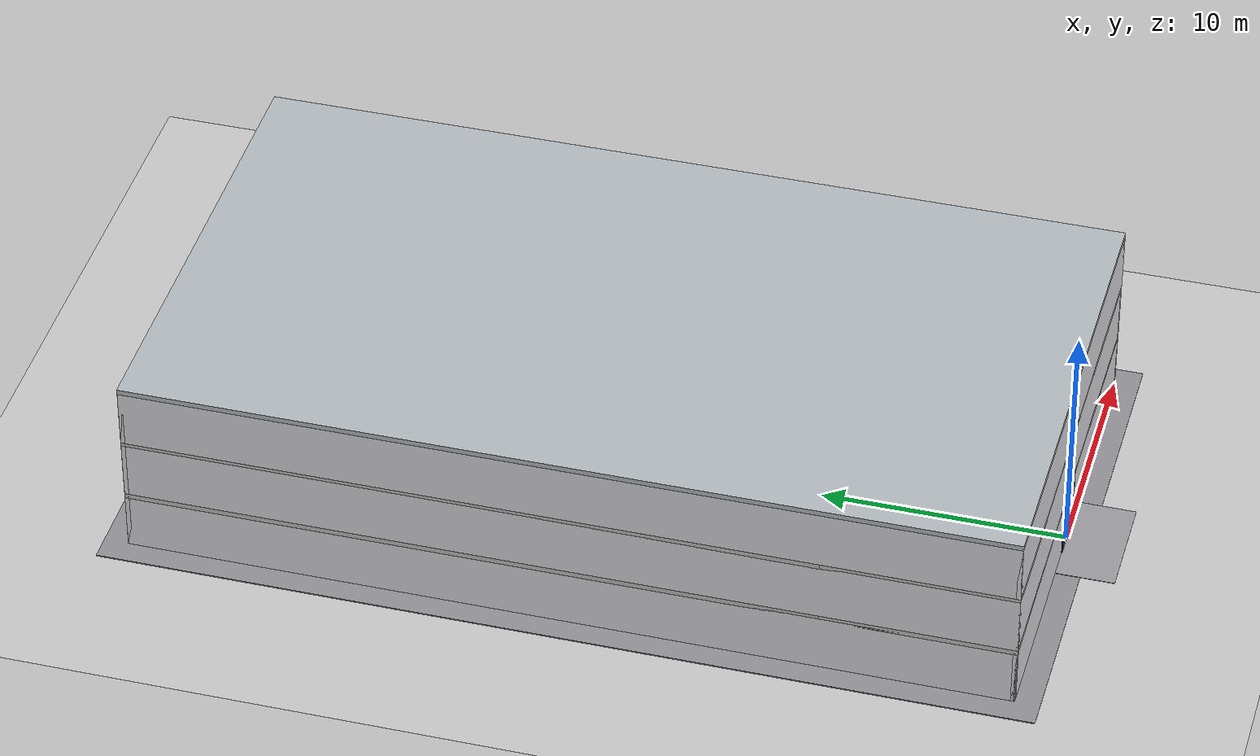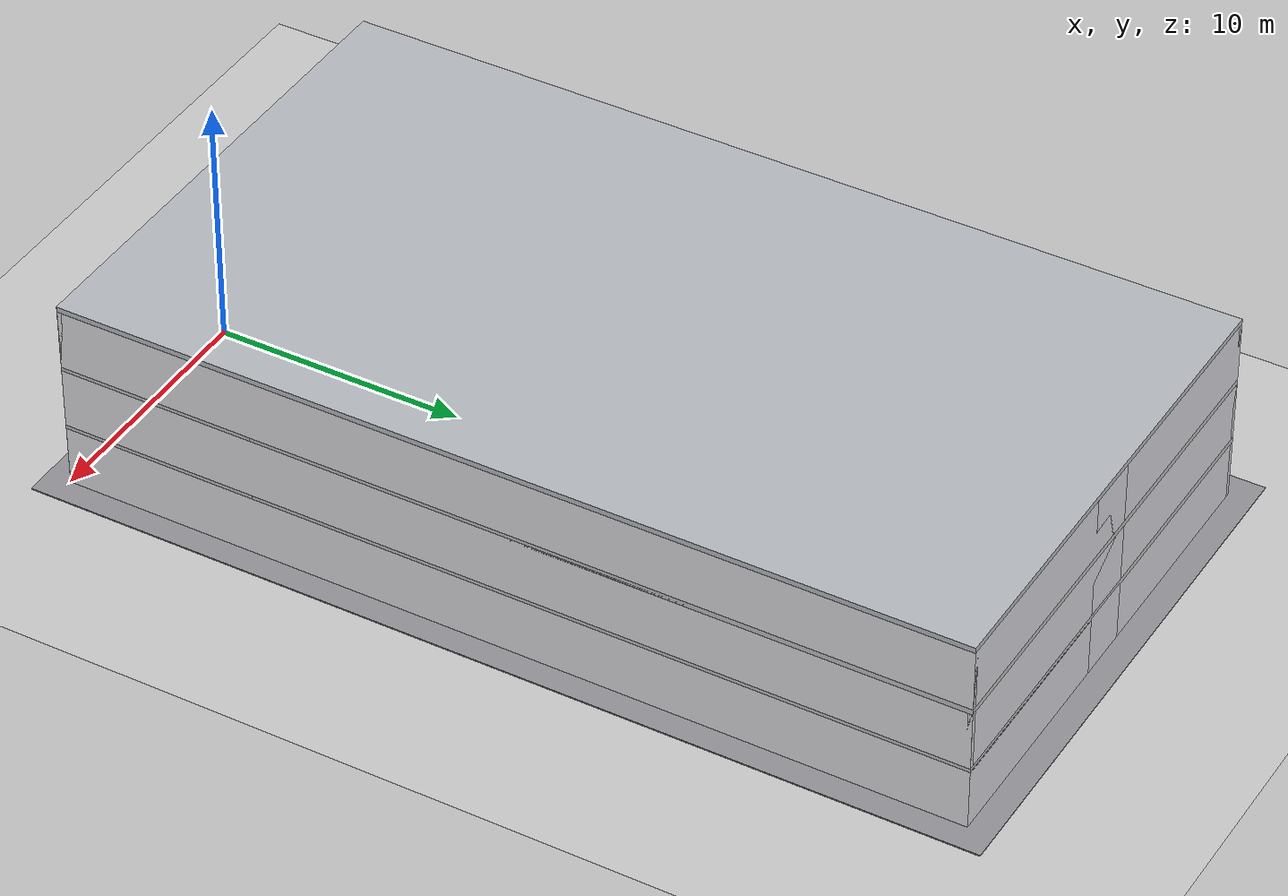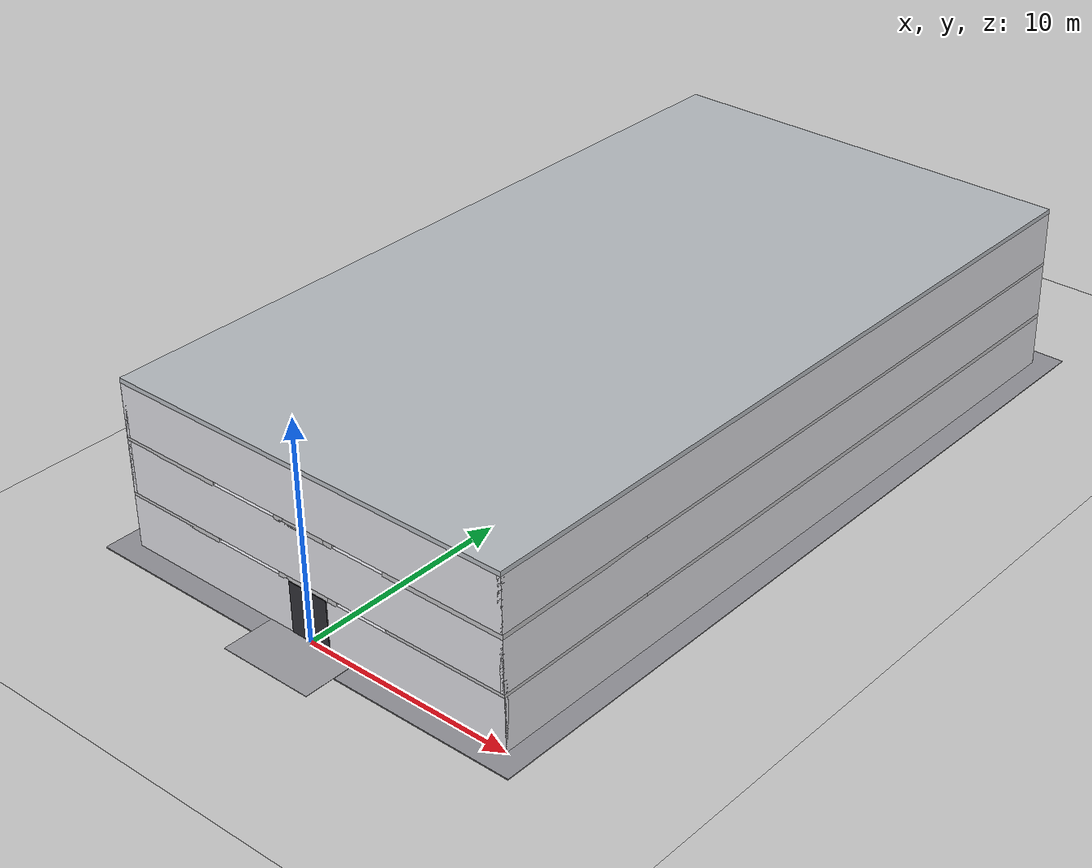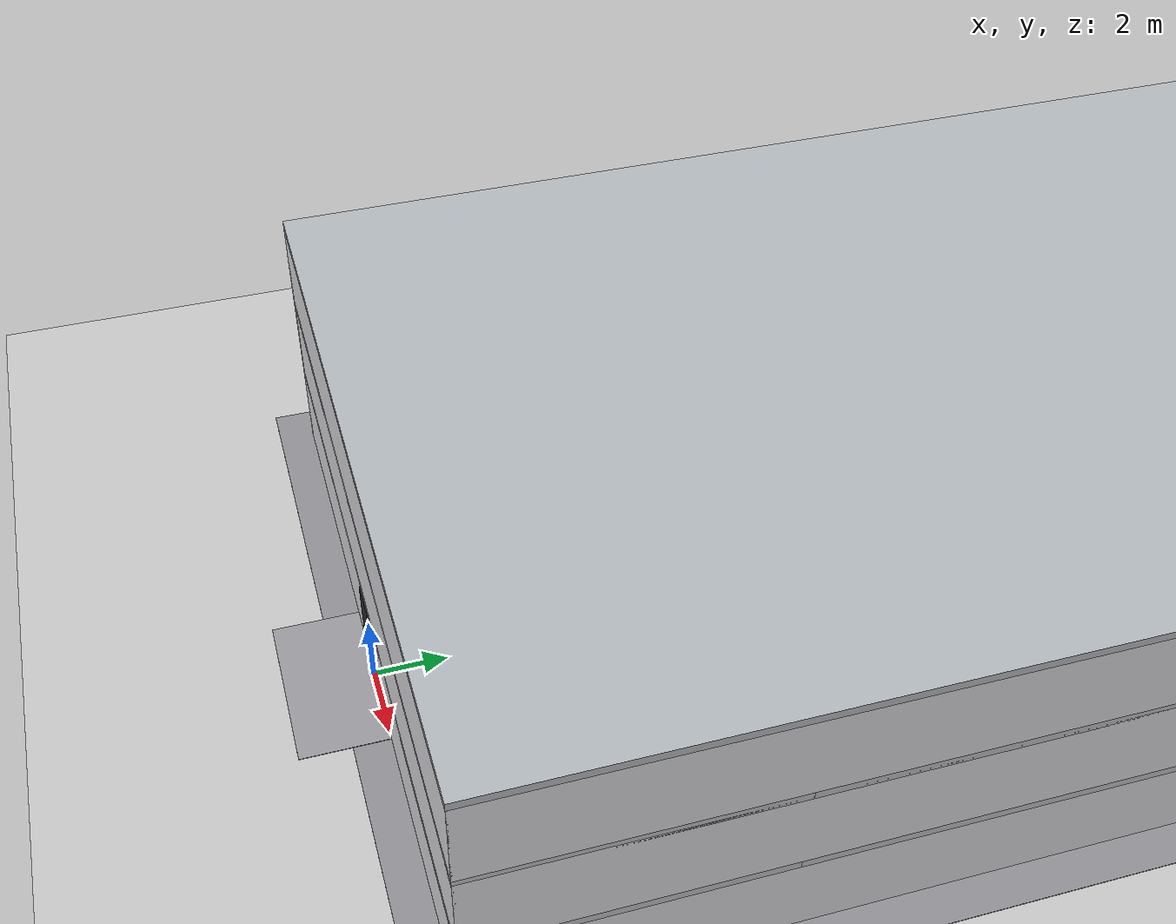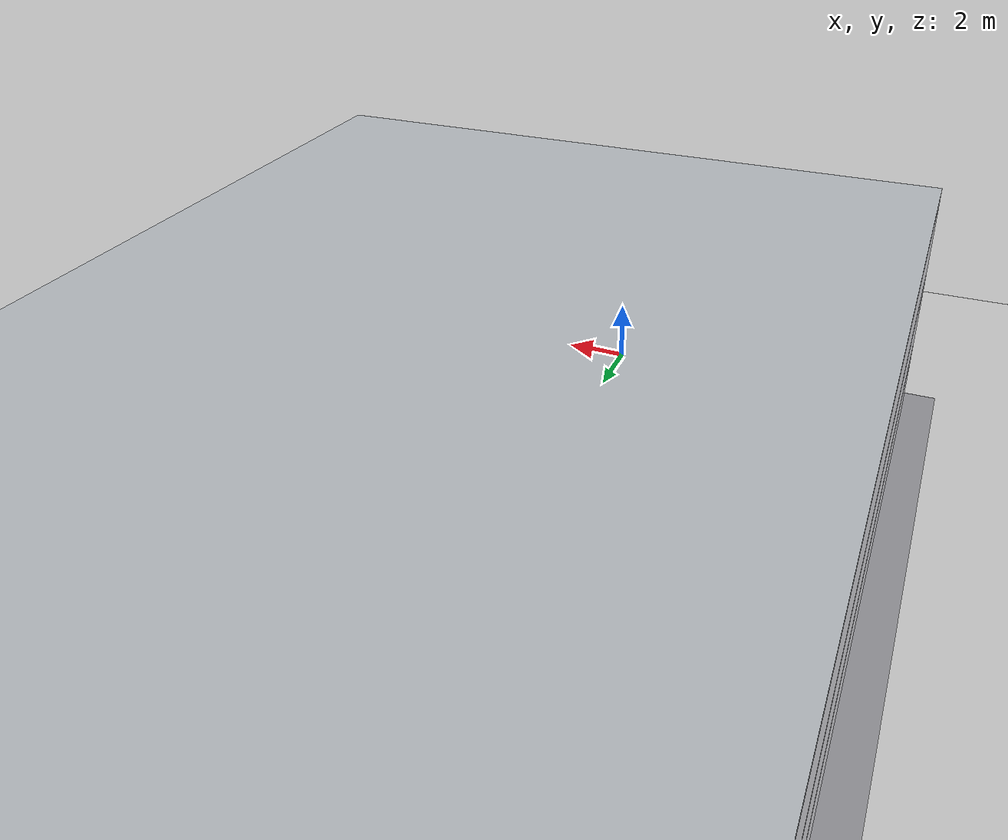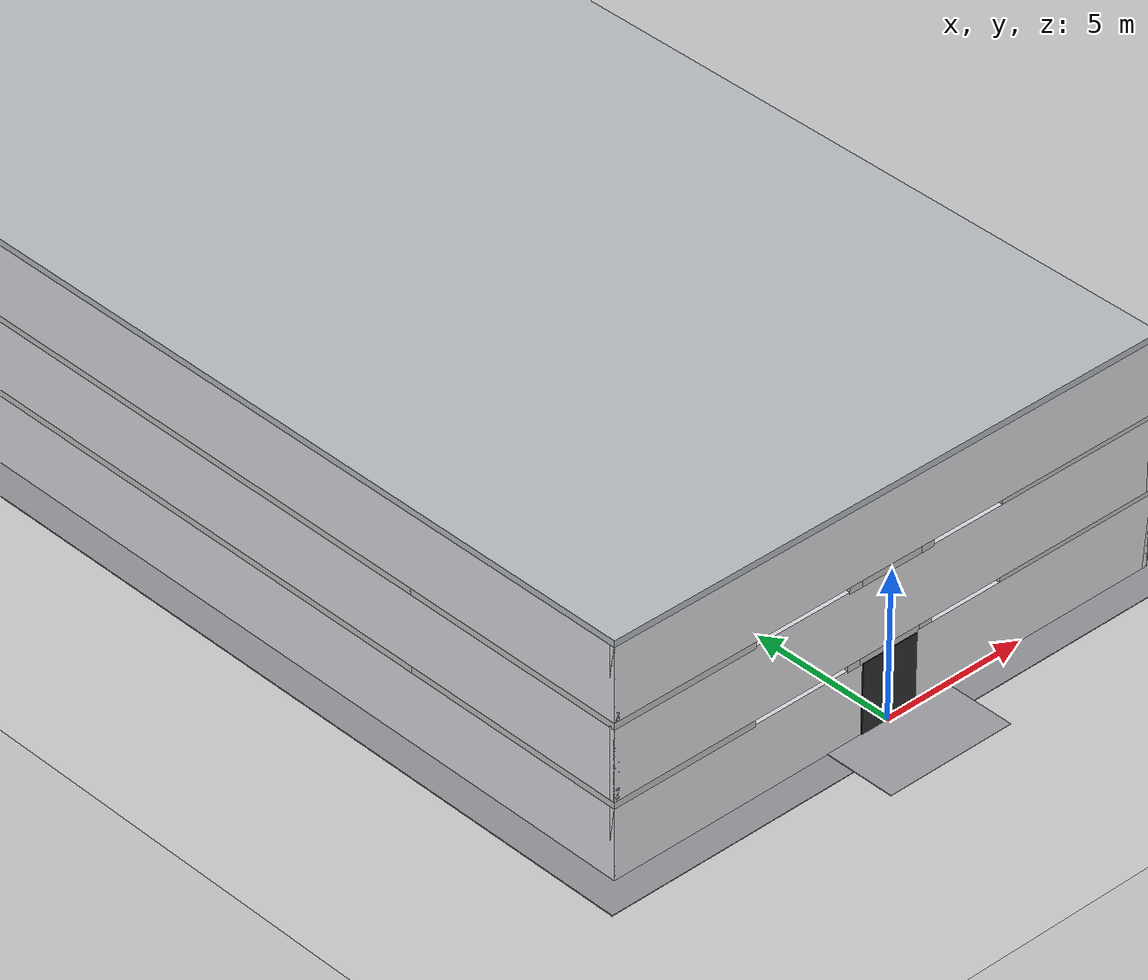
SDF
<?xml version="1.0" ?>
<sdf version="1.7">

  <world name="generated_world">

    <physics name="default_physics" default="0" type="ode">
      <max_step_size>0.002000</max_step_size>
      <real_time_factor>1.000000</real_time_factor>
      <real_time_update_rate>500</real_time_update_rate>
      <gravity>0 0 -9.81</gravity>
      <ode>
        <solver>
          <type>quick</type>
          <iters>40</iters>
          <sor>1.3</sor>
        </solver>
        <constraints>
          <cfm>0.0</cfm>
          <erp>0.2</erp>
          <contact_max_correcting_vel>5.000000</contact_max_correcting_vel>
          <contact_surface_layer>0.001</contact_surface_layer>
        </constraints>
      </ode>
    </physics>
    <include>

      <uri>model://sun</uri>

    </include>

    <include>

      <uri>model://ground_plane</uri>

    </include>

    <model name="generated_building">

      <static>true</static>

      <pose>0 0 0 0 0 0</pose>

      <link name="foundation">

        <pose>0.0000 18.0000 -0.1500 0.0000 0.0000 0.0000</pose>

        <collision name="foundation_collision">

          <geometry>

            <box>

              <size>22.0000 38.0000 0.3000</size>

            </box>

          </geometry>

        </collision>

        <visual name="foundation_visual">

          <geometry>

            <box>

              <size>22.0000 38.0000 0.3000</size>

            </box>

          </geometry>

          <material>

            <ambient>0.58 0.58 0.60 1</ambient>

            <diffuse>0.58 0.58 0.60 1</diffuse>

          </material>

        </visual>

        <gravity>false</gravity>

      </link>

      <link name="entrance_apron">

        <pose>0.0000 -1.2000 0.0100 0.0000 0.0000 0.0000</pose>

        <collision name="entrance_apron_collision">

          <geometry>

            <box>

              <size>4.5000 2.4000 0.0200</size>

            </box>

          </geometry>

        </collision>

        <visual name="entrance_apron_visual">

          <geometry>

            <box>

              <size>4.5000 2.4000 0.0200</size>

            </box>

          </geometry>

          <material>

            <ambient>0.62 0.62 0.64 1</ambient>

            <diffuse>0.62 0.62 0.64 1</diffuse>

          </material>

        </visual>

        <gravity>false</gravity>

      </link>

      <link name="slab_floor_0_0">

        <pose>0.0000 21.9250 -0.1100 0.0000 0.0000 0.0000</pose>

        <collision name="slab_floor_0_0_collision">

          <geometry>

            <box>

              <size>20.0000 28.1500 0.2200</size>

            </box>

          </geometry>

        </collision>

        <visual name="slab_floor_0_0_visual">

          <geometry>

            <box>

              <size>20.0000 28.1500 0.2200</size>

            </box>

          </geometry>

          <material>

            <ambient>0.76 0.76 0.77 1</ambient>

            <diffuse>0.76 0.76 0.77 1</diffuse>

          </material>

        </visual>

        <gravity>false</gravity>

      </link>

      <link name="slab_floor_0_1">

        <pose>-7.4700 3.9250 -0.1100 0.0000 0.0000 0.0000</pose>

        <collision name="slab_floor_0_1_collision">

          <geometry>

            <box>

              <size>5.0600 7.8500 0.2200</size>

            </box>

          </geometry>

        </collision>

        <visual name="slab_floor_0_1_visual">

          <geometry>

            <box>

              <size>5.0600 7.8500 0.2200</size>

            </box>

          </geometry>

          <material>

            <ambient>0.76 0.76 0.77 1</ambient>

            <diffuse>0.76 0.76 0.77 1</diffuse>

          </material>

        </visual>

        <gravity>false</gravity>

      </link>

      <link name="slab_floor_0_2">

        <pose>-1.3300 3.9250 -0.1100 0.0000 0.0000 0.0000</pose>

        <collision name="slab_floor_0_2_collision">

          <geometry>

            <box>

              <size>0.4600 7.8500 0.2200</size>

            </box>

          </geometry>

        </collision>

        <visual name="slab_floor_0_2_visual">

          <geometry>

            <box>

              <size>0.4600 7.8500 0.2200</size>

            </box>

          </geometry>

          <material>

            <ambient>0.76 0.76 0.77 1</ambient>

            <diffuse>0.76 0.76 0.77 1</diffuse>

          </material>

        </visual>

        <gravity>false</gravity>

      </link>

      <link name="slab_floor_0_3">

        <pose>0.0000 3.9250 -0.1100 0.0000 0.0000 0.0000</pose>

        <collision name="slab_floor_0_3_collision">

          <geometry>

            <box>

              <size>2.2000 7.8500 0.2200</size>

            </box>

          </geometry>

        </collision>

        <visual name="slab_floor_0_3_visual">

          <geometry>

            <box>

              <size>2.2000 7.8500 0.2200</size>

            </box>

          </geometry>

          <material>

            <ambient>0.76 0.76 0.77 1</ambient>

            <diffuse>0.76 0.76 0.77 1</diffuse>

          </material>

        </visual>

        <gravity>false</gravity>

      </link>

      <link name="slab_floor_0_4">

        <pose>1.3300 3.9250 -0.1100 0.0000 0.0000 0.0000</pose>

        <collision name="slab_floor_0_4_collision">

          <geometry>

            <box>

              <size>0.4600 7.8500 0.2200</size>

            </box>

          </geometry>

        </collision>

        <visual name="slab_floor_0_4_visual">

          <geometry>

            <box>

              <size>0.4600 7.8500 0.2200</size>

            </box>

          </geometry>

          <material>

            <ambient>0.76 0.76 0.77 1</ambient>

            <diffuse>0.76 0.76 0.77 1</diffuse>

          </material>

        </visual>

        <gravity>false</gravity>

      </link>

      <link name="slab_floor_0_5">

        <pose>7.0700 3.9250 -0.1100 0.0000 0.0000 0.0000</pose>

        <collision name="slab_floor_0_5_collision">

          <geometry>

            <box>

              <size>5.8600 7.8500 0.2200</size>

            </box>

          </geometry>

        </collision>

        <visual name="slab_floor_0_5_visual">

          <geometry>

            <box>

              <size>5.8600 7.8500 0.2200</size>

            </box>

          </geometry>

          <material>

            <ambient>0.76 0.76 0.77 1</ambient>

            <diffuse>0.76 0.76 0.77 1</diffuse>

          </material>

        </visual>

        <gravity>false</gravity>

      </link>

      <link name="stair_edge_infill_floor_0">

        <pose>-1.6500 3.8500 -0.1100 0.0000 0.0000 0.0000</pose>

        <collision name="stair_edge_infill_floor_0_collision">

          <geometry>

            <box>

              <size>0.1800 6.0000 0.2200</size>

            </box>

          </geometry>

        </collision>

        <visual name="stair_edge_infill_floor_0_visual">

          <geometry>

            <box>

              <size>0.1800 6.0000 0.2200</size>

            </box>

          </geometry>

          <material>

            <ambient>0.76 0.76 0.77 1</ambient>

            <diffuse>0.76 0.76 0.77 1</diffuse>

          </material>

        </visual>

        <gravity>false</gravity>

      </link>

      <link name="exterior_west_floor_0">

        <pose>-9.9100 18.0000 1.2250 0.0000 0.0000 0.0000</pose>

        <collision name="exterior_west_floor_0_collision">

          <geometry>

            <box>

              <size>0.1800 36.0000 2.4500</size>

            </box>

          </geometry>

        </collision>

        <visual name="exterior_west_floor_0_visual">

          <geometry>

            <box>

              <size>0.1800 36.0000 2.4500</size>

            </box>

          </geometry>

          <material>

            <ambient>0.86 0.86 0.88 1</ambient>

            <diffuse>0.86 0.86 0.88 1</diffuse>

          </material>

        </visual>

        <gravity>false</gravity>

      </link>

      <link name="exterior_east_floor_0">

        <pose>9.9100 18.0000 1.2250 0.0000 0.0000 0.0000</pose>

        <collision name="exterior_east_floor_0_collision">

          <geometry>

            <box>

              <size>0.1800 36.0000 2.4500</size>

            </box>

          </geometry>

        </collision>

        <visual name="exterior_east_floor_0_visual">

          <geometry>

            <box>

              <size>0.1800 36.0000 2.4500</size>

            </box>

          </geometry>

          <material>

            <ambient>0.86 0.86 0.88 1</ambient>

            <diffuse>0.86 0.86 0.88 1</diffuse>

          </material>

        </visual>

        <gravity>false</gravity>

      </link>

      <link name="exterior_north_floor_0">

        <pose>0.0000 35.9100 1.2250 0.0000 0.0000 0.0000</pose>

        <collision name="exterior_north_floor_0_collision">

          <geometry>

            <box>

              <size>20.0000 0.1800 2.4500</size>

            </box>

          </geometry>

        </collision>

        <visual name="exterior_north_floor_0_visual">

          <geometry>

            <box>

              <size>20.0000 0.1800 2.4500</size>

            </box>

          </geometry>

          <material>

            <ambient>0.86 0.86 0.88 1</ambient>

            <diffuse>0.86 0.86 0.88 1</diffuse>

          </material>

        </visual>

        <gravity>false</gravity>

      </link>

      <link name="exterior_south_entrance_left">

        <pose>-5.5100 0.0900 1.2250 0.0000 0.0000 0.0000</pose>

        <collision name="exterior_south_entrance_left_collision">

          <geometry>

            <box>

              <size>8.9800 0.1800 2.4500</size>

            </box>

          </geometry>

        </collision>

        <visual name="exterior_south_entrance_left_visual">

          <geometry>

            <box>

              <size>8.9800 0.1800 2.4500</size>

            </box>

          </geometry>

          <material>

            <ambient>0.86 0.86 0.88 1</ambient>

            <diffuse>0.86 0.86 0.88 1</diffuse>

          </material>

        </visual>

        <gravity>false</gravity>

      </link>

      <link name="exterior_south_entrance_right">

        <pose>5.5100 0.0900 1.2250 0.0000 0.0000 0.0000</pose>

        <collision name="exterior_south_entrance_right_collision">

          <geometry>

            <box>

              <size>8.9800 0.1800 2.4500</size>

            </box>

          </geometry>

        </collision>

        <visual name="exterior_south_entrance_right_visual">

          <geometry>

            <box>

              <size>8.9800 0.1800 2.4500</size>

            </box>

          </geometry>

          <material>

            <ambient>0.86 0.86 0.88 1</ambient>

            <diffuse>0.86 0.86 0.88 1</diffuse>

          </material>

        </visual>

        <gravity>false</gravity>

      </link>

      <link name="north_end_wall_floor_0">

        <pose>0.0000 35.9100 1.2250 0.0000 0.0000 0.0000</pose>

        <collision name="north_end_wall_floor_0_collision">

          <geometry>

            <box>

              <size>2.2000 0.1800 2.4500</size>

            </box>

          </geometry>

        </collision>

        <visual name="north_end_wall_floor_0_visual">

          <geometry>

            <box>

              <size>2.2000 0.1800 2.4500</size>

            </box>

          </geometry>

          <material>

            <ambient>0.86 0.86 0.88 1</ambient>

            <diffuse>0.86 0.86 0.88 1</diffuse>

          </material>

        </visual>

        <gravity>false</gravity>

      </link>

      <link name="floor_0_room_0_corridor_wall_lower">

        <pose>-1.1900 11.0575 1.2250 0.0000 0.0000 0.0000</pose>

        <collision name="floor_0_room_0_corridor_wall_lower_collision">

          <geometry>

            <box>

              <size>0.1800 6.4150 2.4500</size>

            </box>

          </geometry>

        </collision>

        <visual name="floor_0_room_0_corridor_wall_lower_visual">

          <geometry>

            <box>

              <size>0.1800 6.4150 2.4500</size>

            </box>

          </geometry>

          <material>

            <ambient>0.86 0.86 0.88 1</ambient>

            <diffuse>0.86 0.86 0.88 1</diffuse>

          </material>

        </visual>

        <gravity>false</gravity>

      </link>

      <link name="floor_0_room_0_corridor_wall_upper">

        <pose>-1.1900 18.6725 1.2250 0.0000 0.0000 0.0000</pose>

        <collision name="floor_0_room_0_corridor_wall_upper_collision">

          <geometry>

            <box>

              <size>0.1800 6.4150 2.4500</size>

            </box>

          </geometry>

        </collision>

        <visual name="floor_0_room_0_corridor_wall_upper_visual">

          <geometry>

            <box>

              <size>0.1800 6.4150 2.4500</size>

            </box>

          </geometry>

          <material>

            <ambient>0.86 0.86 0.88 1</ambient>

            <diffuse>0.86 0.86 0.88 1</diffuse>

          </material>

        </visual>

        <gravity>false</gravity>

      </link>

      <link name="floor_0_room_0_west_wall">

        <pose>-9.4100 14.8650 1.2250 0.0000 0.0000 0.0000</pose>

        <collision name="floor_0_room_0_west_wall_collision">

          <geometry>

            <box>

              <size>0.1800 14.0300 2.4500</size>

            </box>

          </geometry>

        </collision>

        <visual name="floor_0_room_0_west_wall_visual">

          <geometry>

            <box>

              <size>0.1800 14.0300 2.4500</size>

            </box>

          </geometry>

          <material>

            <ambient>0.86 0.86 0.88 1</ambient>

            <diffuse>0.86 0.86 0.88 1</diffuse>

          </material>

        </visual>

        <gravity>false</gravity>

      </link>

      <link name="floor_0_room_0_south_wall">

        <pose>-5.3000 7.9400 1.2250 0.0000 0.0000 0.0000</pose>

        <collision name="floor_0_room_0_south_wall_collision">

          <geometry>

            <box>

              <size>8.4000 0.1800 2.4500</size>

            </box>

          </geometry>

        </collision>

        <visual name="floor_0_room_0_south_wall_visual">

          <geometry>

            <box>

              <size>8.4000 0.1800 2.4500</size>

            </box>

          </geometry>

          <material>

            <ambient>0.86 0.86 0.88 1</ambient>

            <diffuse>0.86 0.86 0.88 1</diffuse>

          </material>

        </visual>

        <gravity>false</gravity>

      </link>

      <link name="floor_0_room_0_north_wall">

        <pose>-5.3000 21.7900 1.2250 0.0000 0.0000 0.0000</pose>

        <collision name="floor_0_room_0_north_wall_collision">

          <geometry>

            <box>

              <size>8.4000 0.1800 2.4500</size>

            </box>

          </geometry>

        </collision>

        <visual name="floor_0_room_0_north_wall_visual">

          <geometry>

            <box>

              <size>8.4000 0.1800 2.4500</size>

            </box>

          </geometry>

          <material>

            <ambient>0.86 0.86 0.88 1</ambient>

            <diffuse>0.86 0.86 0.88 1</diffuse>

          </material>

        </visual>

        <gravity>false</gravity>

      </link>

      <link name="floor_0_room_1_corridor_wall_lower">

        <pose>1.1900 11.0575 1.2250 0.0000 0.0000 0.0000</pose>

        <collision name="floor_0_room_1_corridor_wall_lower_collision">

          <geometry>

            <box>

              <size>0.1800 6.4150 2.4500</size>

            </box>

          </geometry>

        </collision>

        <visual name="floor_0_room_1_corridor_wall_lower_visual">

          <geometry>

            <box>

              <size>0.1800 6.4150 2.4500</size>

            </box>

          </geometry>

          <material>

            <ambient>0.86 0.86 0.88 1</ambient>

            <diffuse>0.86 0.86 0.88 1</diffuse>

          </material>

        </visual>

        <gravity>false</gravity>

      </link>

      <link name="floor_0_room_1_corridor_wall_upper">

        <pose>1.1900 18.6725 1.2250 0.0000 0.0000 0.0000</pose>

        <collision name="floor_0_room_1_corridor_wall_upper_collision">

          <geometry>

            <box>

              <size>0.1800 6.4150 2.4500</size>

            </box>

          </geometry>

        </collision>

        <visual name="floor_0_room_1_corridor_wall_upper_visual">

          <geometry>

            <box>

              <size>0.1800 6.4150 2.4500</size>

            </box>

          </geometry>

          <material>

            <ambient>0.86 0.86 0.88 1</ambient>

            <diffuse>0.86 0.86 0.88 1</diffuse>

          </material>

        </visual>

        <gravity>false</gravity>

      </link>

      <link name="floor_0_room_1_east_wall">

        <pose>9.4100 14.8650 1.2250 0.0000 0.0000 0.0000</pose>

        <collision name="floor_0_room_1_east_wall_collision">

          <geometry>

            <box>

              <size>0.1800 14.0300 2.4500</size>

            </box>

          </geometry>

        </collision>

        <visual name="floor_0_room_1_east_wall_visual">

          <geometry>

            <box>

              <size>0.1800 14.0300 2.4500</size>

            </box>

          </geometry>

          <material>

            <ambient>0.86 0.86 0.88 1</ambient>

            <diffuse>0.86 0.86 0.88 1</diffuse>

          </material>

        </visual>

        <gravity>false</gravity>

      </link>

      <link name="floor_0_room_1_south_wall">

        <pose>5.3000 7.9400 1.2250 0.0000 0.0000 0.0000</pose>

        <collision name="floor_0_room_1_south_wall_collision">

          <geometry>

            <box>

              <size>8.4000 0.1800 2.4500</size>

            </box>

          </geometry>

        </collision>

        <visual name="floor_0_room_1_south_wall_visual">

          <geometry>

            <box>

              <size>8.4000 0.1800 2.4500</size>

            </box>

          </geometry>

          <material>

            <ambient>0.86 0.86 0.88 1</ambient>

            <diffuse>0.86 0.86 0.88 1</diffuse>

          </material>

        </visual>

        <gravity>false</gravity>

      </link>

      <link name="floor_0_room_1_north_wall">

        <pose>5.3000 21.7900 1.2250 0.0000 0.0000 0.0000</pose>

        <collision name="floor_0_room_1_north_wall_collision">

          <geometry>

            <box>

              <size>8.4000 0.1800 2.4500</size>

            </box>

          </geometry>

        </collision>

        <visual name="floor_0_room_1_north_wall_visual">

          <geometry>

            <box>

              <size>8.4000 0.1800 2.4500</size>

            </box>

          </geometry>

          <material>

            <ambient>0.86 0.86 0.88 1</ambient>

            <diffuse>0.86 0.86 0.88 1</diffuse>

          </material>

        </visual>

        <gravity>false</gravity>

      </link>

      <link name="floor_0_room_2_corridor_wall_lower">

        <pose>-1.1900 25.0875 1.2250 0.0000 0.0000 0.0000</pose>

        <collision name="floor_0_room_2_corridor_wall_lower_collision">

          <geometry>

            <box>

              <size>0.1800 6.4150 2.4500</size>

            </box>

          </geometry>

        </collision>

        <visual name="floor_0_room_2_corridor_wall_lower_visual">

          <geometry>

            <box>

              <size>0.1800 6.4150 2.4500</size>

            </box>

          </geometry>

          <material>

            <ambient>0.86 0.86 0.88 1</ambient>

            <diffuse>0.86 0.86 0.88 1</diffuse>

          </material>

        </visual>

        <gravity>false</gravity>

      </link>

      <link name="floor_0_room_2_corridor_wall_upper">

        <pose>-1.1900 32.7025 1.2250 0.0000 0.0000 0.0000</pose>

        <collision name="floor_0_room_2_corridor_wall_upper_collision">

          <geometry>

            <box>

              <size>0.1800 6.4150 2.4500</size>

            </box>

          </geometry>

        </collision>

        <visual name="floor_0_room_2_corridor_wall_upper_visual">

          <geometry>

            <box>

              <size>0.1800 6.4150 2.4500</size>

            </box>

          </geometry>

          <material>

            <ambient>0.86 0.86 0.88 1</ambient>

            <diffuse>0.86 0.86 0.88 1</diffuse>

          </material>

        </visual>

        <gravity>false</gravity>

      </link>

      <link name="floor_0_room_2_west_wall">

        <pose>-9.4100 28.8950 1.2250 0.0000 0.0000 0.0000</pose>

        <collision name="floor_0_room_2_west_wall_collision">

          <geometry>

            <box>

              <size>0.1800 14.0300 2.4500</size>

            </box>

          </geometry>

        </collision>

        <visual name="floor_0_room_2_west_wall_visual">

          <geometry>

            <box>

              <size>0.1800 14.0300 2.4500</size>

            </box>

          </geometry>

          <material>

            <ambient>0.86 0.86 0.88 1</ambient>

            <diffuse>0.86 0.86 0.88 1</diffuse>

          </material>

        </visual>

        <gravity>false</gravity>

      </link>

      <link name="floor_0_room_2_south_wall">

        <pose>-5.3000 21.9700 1.2250 0.0000 0.0000 0.0000</pose>

        <collision name="floor_0_room_2_south_wall_collision">

          <geometry>

            <box>

              <size>8.4000 0.1800 2.4500</size>

            </box>

          </geometry>

        </collision>

        <visual name="floor_0_room_2_south_wall_visual">

          <geometry>

            <box>

              <size>8.4000 0.1800 2.4500</size>

            </box>

          </geometry>

          <material>

            <ambient>0.86 0.86 0.88 1</ambient>

            <diffuse>0.86 0.86 0.88 1</diffuse>

          </material>

        </visual>

        <gravity>false</gravity>

      </link>

      <link name="floor_0_room_2_north_wall">

        <pose>-5.3000 35.8200 1.2250 0.0000 0.0000 0.0000</pose>

        <collision name="floor_0_room_2_north_wall_collision">

          <geometry>

            <box>

              <size>8.4000 0.1800 2.4500</size>

            </box>

          </geometry>

        </collision>

        <visual name="floor_0_room_2_north_wall_visual">

          <geometry>

            <box>

              <size>8.4000 0.1800 2.4500</size>

            </box>

          </geometry>

          <material>

            <ambient>0.86 0.86 0.88 1</ambient>

            <diffuse>0.86 0.86 0.88 1</diffuse>

          </material>

        </visual>

        <gravity>false</gravity>

      </link>

      <link name="floor_0_room_3_corridor_wall_lower">

        <pose>1.1900 25.0875 1.2250 0.0000 0.0000 0.0000</pose>

        <collision name="floor_0_room_3_corridor_wall_lower_collision">

          <geometry>

            <box>

              <size>0.1800 6.4150 2.4500</size>

            </box>

          </geometry>

        </collision>

        <visual name="floor_0_room_3_corridor_wall_lower_visual">

          <geometry>

            <box>

              <size>0.1800 6.4150 2.4500</size>

            </box>

          </geometry>

          <material>

            <ambient>0.86 0.86 0.88 1</ambient>

            <diffuse>0.86 0.86 0.88 1</diffuse>

          </material>

        </visual>

        <gravity>false</gravity>

      </link>

      <link name="floor_0_room_3_corridor_wall_upper">

        <pose>1.1900 32.7025 1.2250 0.0000 0.0000 0.0000</pose>

        <collision name="floor_0_room_3_corridor_wall_upper_collision">

          <geometry>

            <box>

              <size>0.1800 6.4150 2.4500</size>

            </box>

          </geometry>

        </collision>

        <visual name="floor_0_room_3_corridor_wall_upper_visual">

          <geometry>

            <box>

              <size>0.1800 6.4150 2.4500</size>

            </box>

          </geometry>

          <material>

            <ambient>0.86 0.86 0.88 1</ambient>

            <diffuse>0.86 0.86 0.88 1</diffuse>

          </material>

        </visual>

        <gravity>false</gravity>

      </link>

      <link name="floor_0_room_3_east_wall">

        <pose>9.4100 28.8950 1.2250 0.0000 0.0000 0.0000</pose>

        <collision name="floor_0_room_3_east_wall_collision">

          <geometry>

            <box>

              <size>0.1800 14.0300 2.4500</size>

            </box>

          </geometry>

        </collision>

        <visual name="floor_0_room_3_east_wall_visual">

          <geometry>

            <box>

              <size>0.1800 14.0300 2.4500</size>

            </box>

          </geometry>

          <material>

            <ambient>0.86 0.86 0.88 1</ambient>

            <diffuse>0.86 0.86 0.88 1</diffuse>

          </material>

        </visual>

        <gravity>false</gravity>

      </link>

      <link name="floor_0_room_3_south_wall">

        <pose>5.3000 21.9700 1.2250 0.0000 0.0000 0.0000</pose>

        <collision name="floor_0_room_3_south_wall_collision">

          <geometry>

            <box>

              <size>8.4000 0.1800 2.4500</size>

            </box>

          </geometry>

        </collision>

        <visual name="floor_0_room_3_south_wall_visual">

          <geometry>

            <box>

              <size>8.4000 0.1800 2.4500</size>

            </box>

          </geometry>

          <material>

            <ambient>0.86 0.86 0.88 1</ambient>

            <diffuse>0.86 0.86 0.88 1</diffuse>

          </material>

        </visual>

        <gravity>false</gravity>

      </link>

      <link name="floor_0_room_3_north_wall">

        <pose>5.3000 35.8200 1.2250 0.0000 0.0000 0.0000</pose>

        <collision name="floor_0_room_3_north_wall_collision">

          <geometry>

            <box>

              <size>8.4000 0.1800 2.4500</size>

            </box>

          </geometry>

        </collision>

        <visual name="floor_0_room_3_north_wall_visual">

          <geometry>

            <box>

              <size>8.4000 0.1800 2.4500</size>

            </box>

          </geometry>

          <material>

            <ambient>0.86 0.86 0.88 1</ambient>

            <diffuse>0.86 0.86 0.88 1</diffuse>

          </material>

        </visual>

        <gravity>false</gravity>

      </link>

      <link name="stair_core_floor_0_west">

        <pose>-4.7600 3.8500 1.2250 0.0000 0.0000 0.0000</pose>

        <collision name="stair_core_floor_0_west_collision">

          <geometry>

            <box>

              <size>0.1800 6.0000 2.4500</size>

            </box>

          </geometry>

        </collision>

        <visual name="stair_core_floor_0_west_visual">

          <geometry>

            <box>

              <size>0.1800 6.0000 2.4500</size>

            </box>

          </geometry>

          <material>

            <ambient>0.86 0.86 0.88 1</ambient>

            <diffuse>0.86 0.86 0.88 1</diffuse>

          </material>

        </visual>

        <gravity>false</gravity>

      </link>

      <link name="stair_core_floor_0_south">

        <pose>-3.2500 0.9400 1.2250 0.0000 0.0000 0.0000</pose>

        <collision name="stair_core_floor_0_south_collision">

          <geometry>

            <box>

              <size>3.2000 0.1800 2.4500</size>

            </box>

          </geometry>

        </collision>

        <visual name="stair_core_floor_0_south_visual">

          <geometry>

            <box>

              <size>3.2000 0.1800 2.4500</size>

            </box>

          </geometry>

          <material>

            <ambient>0.86 0.86 0.88 1</ambient>

            <diffuse>0.86 0.86 0.88 1</diffuse>

          </material>

        </visual>

        <gravity>false</gravity>

      </link>

      <link name="stair_core_floor_0_north">

        <pose>-3.2500 6.7600 1.2250 0.0000 0.0000 0.0000</pose>

        <collision name="stair_core_floor_0_north_collision">

          <geometry>

            <box>

              <size>3.2000 0.1800 2.4500</size>

            </box>

          </geometry>

        </collision>

        <visual name="stair_core_floor_0_north_visual">

          <geometry>

            <box>

              <size>3.2000 0.1800 2.4500</size>

            </box>

          </geometry>

          <material>

            <ambient>0.86 0.86 0.88 1</ambient>

            <diffuse>0.86 0.86 0.88 1</diffuse>

          </material>

        </visual>

        <gravity>false</gravity>

      </link>

      <link name="elevator_core_floor_0_west_lower">

        <pose>1.7400 1.6150 1.2250 0.0000 0.0000 0.0000</pose>

        <collision name="elevator_core_floor_0_west_lower_collision">

          <geometry>

            <box>

              <size>0.1800 0.7300 2.4500</size>

            </box>

          </geometry>

        </collision>

        <visual name="elevator_core_floor_0_west_lower_visual">

          <geometry>

            <box>

              <size>0.1800 0.7300 2.4500</size>

            </box>

          </geometry>

          <material>

            <ambient>0.86 0.86 0.88 1</ambient>

            <diffuse>0.86 0.86 0.88 1</diffuse>

          </material>

        </visual>

        <gravity>false</gravity>

      </link>

      <link name="elevator_core_floor_0_west_upper">

        <pose>1.7400 3.5850 1.2250 0.0000 0.0000 0.0000</pose>

        <collision name="elevator_core_floor_0_west_upper_collision">

          <geometry>

            <box>

              <size>0.1800 0.7300 2.4500</size>

            </box>

          </geometry>

        </collision>

        <visual name="elevator_core_floor_0_west_upper_visual">

          <geometry>

            <box>

              <size>0.1800 0.7300 2.4500</size>

            </box>

          </geometry>

          <material>

            <ambient>0.86 0.86 0.88 1</ambient>

            <diffuse>0.86 0.86 0.88 1</diffuse>

          </material>

        </visual>

        <gravity>false</gravity>

      </link>

      <link name="elevator_core_floor_0_east">

        <pose>3.9600 2.6000 1.2250 0.0000 0.0000 0.0000</pose>

        <collision name="elevator_core_floor_0_east_collision">

          <geometry>

            <box>

              <size>0.1800 2.7000 2.4500</size>

            </box>

          </geometry>

        </collision>

        <visual name="elevator_core_floor_0_east_visual">

          <geometry>

            <box>

              <size>0.1800 2.7000 2.4500</size>

            </box>

          </geometry>

          <material>

            <ambient>0.86 0.86 0.88 1</ambient>

            <diffuse>0.86 0.86 0.88 1</diffuse>

          </material>

        </visual>

        <gravity>false</gravity>

      </link>

      <link name="elevator_core_floor_0_south">

        <pose>2.8500 1.3400 1.2250 0.0000 0.0000 0.0000</pose>

        <collision name="elevator_core_floor_0_south_collision">

          <geometry>

            <box>

              <size>2.4000 0.1800 2.4500</size>

            </box>

          </geometry>

        </collision>

        <visual name="elevator_core_floor_0_south_visual">

          <geometry>

            <box>

              <size>2.4000 0.1800 2.4500</size>

            </box>

          </geometry>

          <material>

            <ambient>0.86 0.86 0.88 1</ambient>

            <diffuse>0.86 0.86 0.88 1</diffuse>

          </material>

        </visual>

        <gravity>false</gravity>

      </link>

      <link name="elevator_core_floor_0_north">

        <pose>2.8500 3.8600 1.2250 0.0000 0.0000 0.0000</pose>

        <collision name="elevator_core_floor_0_north_collision">

          <geometry>

            <box>

              <size>2.4000 0.1800 2.4500</size>

            </box>

          </geometry>

        </collision>

        <visual name="elevator_core_floor_0_north_visual">

          <geometry>

            <box>

              <size>2.4000 0.1800 2.4500</size>

            </box>

          </geometry>

          <material>

            <ambient>0.86 0.86 0.88 1</ambient>

            <diffuse>0.86 0.86 0.88 1</diffuse>

          </material>

        </visual>

        <gravity>false</gravity>

      </link>

      <link name="elevator_threshold_floor_0">

        <pose>1.5400 2.6000 0.0300 0.0000 0.0000 0.0000</pose>

        <collision name="elevator_threshold_floor_0_collision">

          <geometry>

            <box>

              <size>0.2200 1.5000 0.0600</size>

            </box>

          </geometry>

        </collision>

        <visual name="elevator_threshold_floor_0_visual">

          <geometry>

            <box>

              <size>0.2200 1.5000 0.0600</size>

            </box>

          </geometry>

          <material>

            <ambient>0.50 0.51 0.54 1</ambient>

            <diffuse>0.50 0.51 0.54 1</diffuse>

          </material>

        </visual>

        <gravity>false</gravity>

      </link>

      <link name="elevator_sill_infill_floor_0">

        <pose>1.6750 2.6000 -0.1100 0.0000 0.0000 0.0000</pose>

        <collision name="elevator_sill_infill_floor_0_collision">

          <geometry>

            <box>

              <size>0.0500 2.5200 0.2200</size>

            </box>

          </geometry>

        </collision>

        <visual name="elevator_sill_infill_floor_0_visual">

          <geometry>

            <box>

              <size>0.0500 2.5200 0.2200</size>

            </box>

          </geometry>

          <material>

            <ambient>0.72 0.72 0.73 1</ambient>

            <diffuse>0.72 0.72 0.73 1</diffuse>

          </material>

        </visual>

        <gravity>false</gravity>

      </link>

      <link name="elevator_header_floor_0">

        <pose>1.5900 2.6000 2.2600 0.0000 0.0000 0.0000</pose>

        <collision name="elevator_header_floor_0_collision">

          <geometry>

            <box>

              <size>0.1200 1.6000 0.2800</size>

            </box>

          </geometry>

        </collision>

        <visual name="elevator_header_floor_0_visual">

          <geometry>

            <box>

              <size>0.1200 1.6000 0.2800</size>

            </box>

          </geometry>

          <material>

            <ambient>0.50 0.51 0.54 1</ambient>

            <diffuse>0.50 0.51 0.54 1</diffuse>

          </material>

        </visual>

        <gravity>false</gravity>

      </link>

      <link name="elevator_jamb_left_floor_0">

        <pose>1.5900 1.8500 1.1000 0.0000 0.0000 0.0000</pose>

        <collision name="elevator_jamb_left_floor_0_collision">

          <geometry>

            <box>

              <size>0.1200 0.1000 2.2000</size>

            </box>

          </geometry>

        </collision>

        <visual name="elevator_jamb_left_floor_0_visual">

          <geometry>

            <box>

              <size>0.1200 0.1000 2.2000</size>

            </box>

          </geometry>

          <material>

            <ambient>0.50 0.51 0.54 1</ambient>

            <diffuse>0.50 0.51 0.54 1</diffuse>

          </material>

        </visual>

        <gravity>false</gravity>

      </link>

      <link name="elevator_jamb_right_floor_0">

        <pose>1.5900 3.3500 1.1000 0.0000 0.0000 0.0000</pose>

        <collision name="elevator_jamb_right_floor_0_collision">

          <geometry>

            <box>

              <size>0.1200 0.1000 2.2000</size>

            </box>

          </geometry>

        </collision>

        <visual name="elevator_jamb_right_floor_0_visual">

          <geometry>

            <box>

              <size>0.1200 0.1000 2.2000</size>

            </box>

          </geometry>

          <material>

            <ambient>0.50 0.51 0.54 1</ambient>

            <diffuse>0.50 0.51 0.54 1</diffuse>

          </material>

        </visual>

        <gravity>false</gravity>

      </link>

      <link name="elevator_call_panel_floor_0">

        <pose>1.5700 3.5800 1.2000 0.0000 0.0000 0.0000</pose>

        <collision name="elevator_call_panel_floor_0_collision">

          <geometry>

            <box>

              <size>0.0800 0.2200 0.3200</size>

            </box>

          </geometry>

        </collision>

        <visual name="elevator_call_panel_floor_0_visual">

          <geometry>

            <box>

              <size>0.0800 0.2200 0.3200</size>

            </box>

          </geometry>

          <material>

            <ambient>0.20 0.20 0.24 1</ambient>

            <diffuse>0.20 0.20 0.24 1</diffuse>

          </material>

        </visual>

        <gravity>false</gravity>

      </link>

      <link name="floor_0_room_0_desk">

        <pose>-7.0000 17.9225 0.4500 0.0000 0.0000 0.0000</pose>

        <collision name="floor_0_room_0_desk_collision">

          <geometry>

            <box>

              <size>1.5000 0.7000 0.7500</size>

            </box>

          </geometry>

        </collision>

        <visual name="floor_0_room_0_desk_visual">

          <geometry>

            <box>

              <size>1.5000 0.7000 0.7500</size>

            </box>

          </geometry>

          <material>

            <ambient>0.54 0.43 0.34 1</ambient>

            <diffuse>0.54 0.43 0.34 1</diffuse>

          </material>

        </visual>

        <gravity>false</gravity>

      </link>

      <link name="floor_0_room_0_chair">

        <pose>-7.0000 17.0225 0.2800 0.0000 0.0000 0.0000</pose>

        <collision name="floor_0_room_0_chair_collision">

          <geometry>

            <box>

              <size>0.5500 0.5500 0.5500</size>

            </box>

          </geometry>

        </collision>

        <visual name="floor_0_room_0_chair_visual">

          <geometry>

            <box>

              <size>0.5500 0.5500 0.5500</size>

            </box>

          </geometry>

          <material>

            <ambient>0.30 0.30 0.34 1</ambient>

            <diffuse>0.30 0.30 0.34 1</diffuse>

          </material>

        </visual>

        <gravity>false</gravity>

      </link>

      <link name="floor_0_room_0_cabinet">

        <pose>-3.6000 11.8075 0.9000 0.0000 0.0000 0.0000</pose>

        <collision name="floor_0_room_0_cabinet_collision">

          <geometry>

            <box>

              <size>0.6000 1.0000 1.8000</size>

            </box>

          </geometry>

        </collision>

        <visual name="floor_0_room_0_cabinet_visual">

          <geometry>

            <box>

              <size>0.6000 1.0000 1.8000</size>

            </box>

          </geometry>

          <material>

            <ambient>0.72 0.72 0.74 1</ambient>

            <diffuse>0.72 0.72 0.74 1</diffuse>

          </material>

        </visual>

        <gravity>false</gravity>

      </link>

      <link name="floor_0_room_0_side_table">

        <pose>-3.6000 17.9225 0.3200 0.0000 0.0000 0.0000</pose>

        <collision name="floor_0_room_0_side_table_collision">

          <geometry>

            <box>

              <size>0.7000 0.7000 0.4500</size>

            </box>

          </geometry>

        </collision>

        <visual name="floor_0_room_0_side_table_visual">

          <geometry>

            <box>

              <size>0.7000 0.7000 0.4500</size>

            </box>

          </geometry>

          <material>

            <ambient>0.52 0.42 0.33 1</ambient>

            <diffuse>0.52 0.42 0.33 1</diffuse>

          </material>

        </visual>

        <gravity>false</gravity>

      </link>

      <link name="floor_0_room_0_planter">

        <pose>-5.3000 11.8075 0.4500 0.0000 0.0000 0.0000</pose>

        <collision name="floor_0_room_0_planter_collision">

          <geometry>

            <box>

              <size>0.4500 0.4500 0.9000</size>

            </box>

          </geometry>

        </collision>

        <visual name="floor_0_room_0_planter_visual">

          <geometry>

            <box>

              <size>0.4500 0.4500 0.9000</size>

            </box>

          </geometry>

          <material>

            <ambient>0.28 0.46 0.30 1</ambient>

            <diffuse>0.28 0.46 0.30 1</diffuse>

          </material>

        </visual>

        <gravity>false</gravity>

      </link>

      <link name="floor_0_room_1_desk">

        <pose>3.6000 17.9225 0.4500 0.0000 0.0000 0.0000</pose>

        <collision name="floor_0_room_1_desk_collision">

          <geometry>

            <box>

              <size>1.5000 0.7000 0.7500</size>

            </box>

          </geometry>

        </collision>

        <visual name="floor_0_room_1_desk_visual">

          <geometry>

            <box>

              <size>1.5000 0.7000 0.7500</size>

            </box>

          </geometry>

          <material>

            <ambient>0.54 0.43 0.34 1</ambient>

            <diffuse>0.54 0.43 0.34 1</diffuse>

          </material>

        </visual>

        <gravity>false</gravity>

      </link>

      <link name="floor_0_room_1_chair">

        <pose>3.6000 17.0225 0.2800 0.0000 0.0000 0.0000</pose>

        <collision name="floor_0_room_1_chair_collision">

          <geometry>

            <box>

              <size>0.5500 0.5500 0.5500</size>

            </box>

          </geometry>

        </collision>

        <visual name="floor_0_room_1_chair_visual">

          <geometry>

            <box>

              <size>0.5500 0.5500 0.5500</size>

            </box>

          </geometry>

          <material>

            <ambient>0.30 0.30 0.34 1</ambient>

            <diffuse>0.30 0.30 0.34 1</diffuse>

          </material>

        </visual>

        <gravity>false</gravity>

      </link>

      <link name="floor_0_room_1_cabinet">

        <pose>7.0000 11.8075 0.9000 0.0000 0.0000 0.0000</pose>

        <collision name="floor_0_room_1_cabinet_collision">

          <geometry>

            <box>

              <size>0.6000 1.0000 1.8000</size>

            </box>

          </geometry>

        </collision>

        <visual name="floor_0_room_1_cabinet_visual">

          <geometry>

            <box>

              <size>0.6000 1.0000 1.8000</size>

            </box>

          </geometry>

          <material>

            <ambient>0.72 0.72 0.74 1</ambient>

            <diffuse>0.72 0.72 0.74 1</diffuse>

          </material>

        </visual>

        <gravity>false</gravity>

      </link>

      <link name="floor_0_room_1_side_table">

        <pose>7.0000 17.9225 0.3200 0.0000 0.0000 0.0000</pose>

        <collision name="floor_0_room_1_side_table_collision">

          <geometry>

            <box>

              <size>0.7000 0.7000 0.4500</size>

            </box>

          </geometry>

        </collision>

        <visual name="floor_0_room_1_side_table_visual">

          <geometry>

            <box>

              <size>0.7000 0.7000 0.4500</size>

            </box>

          </geometry>

          <material>

            <ambient>0.52 0.42 0.33 1</ambient>

            <diffuse>0.52 0.42 0.33 1</diffuse>

          </material>

        </visual>

        <gravity>false</gravity>

      </link>

      <link name="floor_0_room_1_planter">

        <pose>5.3000 11.8075 0.4500 0.0000 0.0000 0.0000</pose>

        <collision name="floor_0_room_1_planter_collision">

          <geometry>

            <box>

              <size>0.4500 0.4500 0.9000</size>

            </box>

          </geometry>

        </collision>

        <visual name="floor_0_room_1_planter_visual">

          <geometry>

            <box>

              <size>0.4500 0.4500 0.9000</size>

            </box>

          </geometry>

          <material>

            <ambient>0.28 0.46 0.30 1</ambient>

            <diffuse>0.28 0.46 0.30 1</diffuse>

          </material>

        </visual>

        <gravity>false</gravity>

      </link>

      <link name="floor_0_room_2_desk">

        <pose>-7.0000 31.9525 0.4500 0.0000 0.0000 0.0000</pose>

        <collision name="floor_0_room_2_desk_collision">

          <geometry>

            <box>

              <size>1.5000 0.7000 0.7500</size>

            </box>

          </geometry>

        </collision>

        <visual name="floor_0_room_2_desk_visual">

          <geometry>

            <box>

              <size>1.5000 0.7000 0.7500</size>

            </box>

          </geometry>

          <material>

            <ambient>0.54 0.43 0.34 1</ambient>

            <diffuse>0.54 0.43 0.34 1</diffuse>

          </material>

        </visual>

        <gravity>false</gravity>

      </link>

      <link name="floor_0_room_2_chair">

        <pose>-7.0000 31.0525 0.2800 0.0000 0.0000 0.0000</pose>

        <collision name="floor_0_room_2_chair_collision">

          <geometry>

            <box>

              <size>0.5500 0.5500 0.5500</size>

            </box>

          </geometry>

        </collision>

        <visual name="floor_0_room_2_chair_visual">

          <geometry>

            <box>

              <size>0.5500 0.5500 0.5500</size>

            </box>

          </geometry>

          <material>

            <ambient>0.30 0.30 0.34 1</ambient>

            <diffuse>0.30 0.30 0.34 1</diffuse>

          </material>

        </visual>

        <gravity>false</gravity>

      </link>

      <link name="floor_0_room_2_cabinet">

        <pose>-3.6000 25.8375 0.9000 0.0000 0.0000 0.0000</pose>

        <collision name="floor_0_room_2_cabinet_collision">

          <geometry>

            <box>

              <size>0.6000 1.0000 1.8000</size>

            </box>

          </geometry>

        </collision>

        <visual name="floor_0_room_2_cabinet_visual">

          <geometry>

            <box>

              <size>0.6000 1.0000 1.8000</size>

            </box>

          </geometry>

          <material>

            <ambient>0.72 0.72 0.74 1</ambient>

            <diffuse>0.72 0.72 0.74 1</diffuse>

          </material>

        </visual>

        <gravity>false</gravity>

      </link>

      <link name="floor_0_room_2_side_table">

        <pose>-3.6000 31.9525 0.3200 0.0000 0.0000 0.0000</pose>

        <collision name="floor_0_room_2_side_table_collision">

          <geometry>

            <box>

              <size>0.7000 0.7000 0.4500</size>

            </box>

          </geometry>

        </collision>

        <visual name="floor_0_room_2_side_table_visual">

          <geometry>

            <box>

              <size>0.7000 0.7000 0.4500</size>

            </box>

          </geometry>

          <material>

            <ambient>0.52 0.42 0.33 1</ambient>

            <diffuse>0.52 0.42 0.33 1</diffuse>

          </material>

        </visual>

        <gravity>false</gravity>

      </link>

      <link name="floor_0_room_2_planter">

        <pose>-5.3000 25.8375 0.4500 0.0000 0.0000 0.0000</pose>

        <collision name="floor_0_room_2_planter_collision">

          <geometry>

            <box>

              <size>0.4500 0.4500 0.9000</size>

            </box>

          </geometry>

        </collision>

        <visual name="floor_0_room_2_planter_visual">

          <geometry>

            <box>

              <size>0.4500 0.4500 0.9000</size>

            </box>

          </geometry>

          <material>

            <ambient>0.28 0.46 0.30 1</ambient>

            <diffuse>0.28 0.46 0.30 1</diffuse>

          </material>

        </visual>

        <gravity>false</gravity>

      </link>

      <link name="floor_0_room_3_desk">

        <pose>3.6000 31.9525 0.4500 0.0000 0.0000 0.0000</pose>

        <collision name="floor_0_room_3_desk_collision">

          <geometry>

            <box>

              <size>1.5000 0.7000 0.7500</size>

            </box>

          </geometry>

        </collision>

        <visual name="floor_0_room_3_desk_visual">

          <geometry>

            <box>

              <size>1.5000 0.7000 0.7500</size>

            </box>

          </geometry>

          <material>

            <ambient>0.54 0.43 0.34 1</ambient>

            <diffuse>0.54 0.43 0.34 1</diffuse>

          </material>

        </visual>

        <gravity>false</gravity>

      </link>

      <link name="floor_0_room_3_chair">

        <pose>3.6000 31.0525 0.2800 0.0000 0.0000 0.0000</pose>

        <collision name="floor_0_room_3_chair_collision">

          <geometry>

            <box>

              <size>0.5500 0.5500 0.5500</size>

            </box>

          </geometry>

        </collision>

        <visual name="floor_0_room_3_chair_visual">

          <geometry>

            <box>

              <size>0.5500 0.5500 0.5500</size>

            </box>

          </geometry>

          <material>

            <ambient>0.30 0.30 0.34 1</ambient>

            <diffuse>0.30 0.30 0.34 1</diffuse>

          </material>

        </visual>

        <gravity>false</gravity>

      </link>

      <link name="floor_0_room_3_cabinet">

        <pose>7.0000 25.8375 0.9000 0.0000 0.0000 0.0000</pose>

        <collision name="floor_0_room_3_cabinet_collision">

          <geometry>

            <box>

              <size>0.6000 1.0000 1.8000</size>

            </box>

          </geometry>

        </collision>

        <visual name="floor_0_room_3_cabinet_visual">

          <geometry>

            <box>

              <size>0.6000 1.0000 1.8000</size>

            </box>

          </geometry>

          <material>

            <ambient>0.72 0.72 0.74 1</ambient>

            <diffuse>0.72 0.72 0.74 1</diffuse>

          </material>

        </visual>

        <gravity>false</gravity>

      </link>

      <link name="floor_0_room_3_side_table">

        <pose>7.0000 31.9525 0.3200 0.0000 0.0000 0.0000</pose>

        <collision name="floor_0_room_3_side_table_collision">

          <geometry>

            <box>

              <size>0.7000 0.7000 0.4500</size>

            </box>

          </geometry>

        </collision>

        <visual name="floor_0_room_3_side_table_visual">

          <geometry>

            <box>

              <size>0.7000 0.7000 0.4500</size>

            </box>

          </geometry>

          <material>

            <ambient>0.52 0.42 0.33 1</ambient>

            <diffuse>0.52 0.42 0.33 1</diffuse>

          </material>

        </visual>

        <gravity>false</gravity>

      </link>

      <link name="floor_0_room_3_planter">

        <pose>5.3000 25.8375 0.4500 0.0000 0.0000 0.0000</pose>

        <collision name="floor_0_room_3_planter_collision">

          <geometry>

            <box>

              <size>0.4500 0.4500 0.9000</size>

            </box>

          </geometry>

        </collision>

        <visual name="floor_0_room_3_planter_visual">

          <geometry>

            <box>

              <size>0.4500 0.4500 0.9000</size>

            </box>

          </geometry>

          <material>

            <ambient>0.28 0.46 0.30 1</ambient>

            <diffuse>0.28 0.46 0.30 1</diffuse>

          </material>

        </visual>

        <gravity>false</gravity>

      </link>

      <link name="slab_floor_1_0">

        <pose>0.0000 21.9250 2.4900 0.0000 0.0000 0.0000</pose>

        <collision name="slab_floor_1_0_collision">

          <geometry>

            <box>

              <size>20.0000 28.1500 0.2200</size>

            </box>

          </geometry>

        </collision>

        <visual name="slab_floor_1_0_visual">

          <geometry>

            <box>

              <size>20.0000 28.1500 0.2200</size>

            </box>

          </geometry>

          <material>

            <ambient>0.76 0.76 0.77 1</ambient>

            <diffuse>0.76 0.76 0.77 1</diffuse>

          </material>

        </visual>

        <gravity>false</gravity>

      </link>

      <link name="slab_floor_1_1">

        <pose>-7.4700 3.9250 2.4900 0.0000 0.0000 0.0000</pose>

        <collision name="slab_floor_1_1_collision">

          <geometry>

            <box>

              <size>5.0600 7.8500 0.2200</size>

            </box>

          </geometry>

        </collision>

        <visual name="slab_floor_1_1_visual">

          <geometry>

            <box>

              <size>5.0600 7.8500 0.2200</size>

            </box>

          </geometry>

          <material>

            <ambient>0.76 0.76 0.77 1</ambient>

            <diffuse>0.76 0.76 0.77 1</diffuse>

          </material>

        </visual>

        <gravity>false</gravity>

      </link>

      <link name="slab_floor_1_2">

        <pose>-1.3300 3.9250 2.4900 0.0000 0.0000 0.0000</pose>

        <collision name="slab_floor_1_2_collision">

          <geometry>

            <box>

              <size>0.4600 7.8500 0.2200</size>

            </box>

          </geometry>

        </collision>

        <visual name="slab_floor_1_2_visual">

          <geometry>

            <box>

              <size>0.4600 7.8500 0.2200</size>

            </box>

          </geometry>

          <material>

            <ambient>0.76 0.76 0.77 1</ambient>

            <diffuse>0.76 0.76 0.77 1</diffuse>

          </material>

        </visual>

        <gravity>false</gravity>

      </link>

      <link name="slab_floor_1_3">

        <pose>0.0000 3.9250 2.4900 0.0000 0.0000 0.0000</pose>

        <collision name="slab_floor_1_3_collision">

          <geometry>

            <box>

              <size>2.2000 7.8500 0.2200</size>

            </box>

          </geometry>

        </collision>

        <visual name="slab_floor_1_3_visual">

          <geometry>

            <box>

              <size>2.2000 7.8500 0.2200</size>

            </box>

          </geometry>

          <material>

            <ambient>0.76 0.76 0.77 1</ambient>

            <diffuse>0.76 0.76 0.77 1</diffuse>

          </material>

        </visual>

        <gravity>false</gravity>

      </link>

      <link name="slab_floor_1_4">

        <pose>1.3300 3.9250 2.4900 0.0000 0.0000 0.0000</pose>

        <collision name="slab_floor_1_4_collision">

          <geometry>

            <box>

              <size>0.4600 7.8500 0.2200</size>

            </box>

          </geometry>

        </collision>

        <visual name="slab_floor_1_4_visual">

          <geometry>

            <box>

              <size>0.4600 7.8500 0.2200</size>

            </box>

          </geometry>

          <material>

            <ambient>0.76 0.76 0.77 1</ambient>

            <diffuse>0.76 0.76 0.77 1</diffuse>

          </material>

        </visual>

        <gravity>false</gravity>

      </link>

      <link name="slab_floor_1_5">

        <pose>7.0700 3.9250 2.4900 0.0000 0.0000 0.0000</pose>

        <collision name="slab_floor_1_5_collision">

          <geometry>

            <box>

              <size>5.8600 7.8500 0.2200</size>

            </box>

          </geometry>

        </collision>

        <visual name="slab_floor_1_5_visual">

          <geometry>

            <box>

              <size>5.8600 7.8500 0.2200</size>

            </box>

          </geometry>

          <material>

            <ambient>0.76 0.76 0.77 1</ambient>

            <diffuse>0.76 0.76 0.77 1</diffuse>

          </material>

        </visual>

        <gravity>false</gravity>

      </link>

      <link name="stair_edge_infill_floor_1">

        <pose>-1.6500 3.8500 2.4900 0.0000 0.0000 0.0000</pose>

        <collision name="stair_edge_infill_floor_1_collision">

          <geometry>

            <box>

              <size>0.1800 6.0000 0.2200</size>

            </box>

          </geometry>

        </collision>

        <visual name="stair_edge_infill_floor_1_visual">

          <geometry>

            <box>

              <size>0.1800 6.0000 0.2200</size>

            </box>

          </geometry>

          <material>

            <ambient>0.76 0.76 0.77 1</ambient>

            <diffuse>0.76 0.76 0.77 1</diffuse>

          </material>

        </visual>

        <gravity>false</gravity>

      </link>

      <link name="exterior_west_floor_1">

        <pose>-9.9100 18.0000 3.8250 0.0000 0.0000 0.0000</pose>

        <collision name="exterior_west_floor_1_collision">

          <geometry>

            <box>

              <size>0.1800 36.0000 2.4500</size>

            </box>

          </geometry>

        </collision>

        <visual name="exterior_west_floor_1_visual">

          <geometry>

            <box>

              <size>0.1800 36.0000 2.4500</size>

            </box>

          </geometry>

          <material>

            <ambient>0.86 0.86 0.88 1</ambient>

            <diffuse>0.86 0.86 0.88 1</diffuse>

          </material>

        </visual>

        <gravity>false</gravity>

      </link>

      <link name="exterior_east_floor_1">

        <pose>9.9100 18.0000 3.8250 0.0000 0.0000 0.0000</pose>

        <collision name="exterior_east_floor_1_collision">

          <geometry>

            <box>

              <size>0.1800 36.0000 2.4500</size>

            </box>

          </geometry>

        </collision>

        <visual name="exterior_east_floor_1_visual">

          <geometry>

            <box>

              <size>0.1800 36.0000 2.4500</size>

            </box>

          </geometry>

          <material>

            <ambient>0.86 0.86 0.88 1</ambient>

            <diffuse>0.86 0.86 0.88 1</diffuse>

          </material>

        </visual>

        <gravity>false</gravity>

      </link>

      <link name="exterior_north_floor_1">

        <pose>0.0000 35.9100 3.8250 0.0000 0.0000 0.0000</pose>

        <collision name="exterior_north_floor_1_collision">

          <geometry>

            <box>

              <size>20.0000 0.1800 2.4500</size>

            </box>

          </geometry>

        </collision>

        <visual name="exterior_north_floor_1_visual">

          <geometry>

            <box>

              <size>20.0000 0.1800 2.4500</size>

            </box>

          </geometry>

          <material>

            <ambient>0.86 0.86 0.88 1</ambient>

            <diffuse>0.86 0.86 0.88 1</diffuse>

          </material>

        </visual>

        <gravity>false</gravity>

      </link>

      <link name="exterior_south_floor_1">

        <pose>0.0000 0.0900 3.8250 0.0000 0.0000 0.0000</pose>

        <collision name="exterior_south_floor_1_collision">

          <geometry>

            <box>

              <size>20.0000 0.1800 2.4500</size>

            </box>

          </geometry>

        </collision>

        <visual name="exterior_south_floor_1_visual">

          <geometry>

            <box>

              <size>20.0000 0.1800 2.4500</size>

            </box>

          </geometry>

          <material>

            <ambient>0.86 0.86 0.88 1</ambient>

            <diffuse>0.86 0.86 0.88 1</diffuse>

          </material>

        </visual>

        <gravity>false</gravity>

      </link>

      <link name="north_end_wall_floor_1">

        <pose>0.0000 35.9100 3.8250 0.0000 0.0000 0.0000</pose>

        <collision name="north_end_wall_floor_1_collision">

          <geometry>

            <box>

              <size>2.2000 0.1800 2.4500</size>

            </box>

          </geometry>

        </collision>

        <visual name="north_end_wall_floor_1_visual">

          <geometry>

            <box>

              <size>2.2000 0.1800 2.4500</size>

            </box>

          </geometry>

          <material>

            <ambient>0.86 0.86 0.88 1</ambient>

            <diffuse>0.86 0.86 0.88 1</diffuse>

          </material>

        </visual>

        <gravity>false</gravity>

      </link>

      <link name="floor_1_room_0_corridor_wall_lower">

        <pose>-1.1900 11.0575 3.8250 0.0000 0.0000 0.0000</pose>

        <collision name="floor_1_room_0_corridor_wall_lower_collision">

          <geometry>

            <box>

              <size>0.1800 6.4150 2.4500</size>

            </box>

          </geometry>

        </collision>

        <visual name="floor_1_room_0_corridor_wall_lower_visual">

          <geometry>

            <box>

              <size>0.1800 6.4150 2.4500</size>

            </box>

          </geometry>

          <material>

            <ambient>0.86 0.86 0.88 1</ambient>

            <diffuse>0.86 0.86 0.88 1</diffuse>

          </material>

        </visual>

        <gravity>false</gravity>

      </link>

      <link name="floor_1_room_0_corridor_wall_upper">

        <pose>-1.1900 18.6725 3.8250 0.0000 0.0000 0.0000</pose>

        <collision name="floor_1_room_0_corridor_wall_upper_collision">

          <geometry>

            <box>

              <size>0.1800 6.4150 2.4500</size>

            </box>

          </geometry>

        </collision>

        <visual name="floor_1_room_0_corridor_wall_upper_visual">

          <geometry>

            <box>

              <size>0.1800 6.4150 2.4500</size>

            </box>

          </geometry>

          <material>

            <ambient>0.86 0.86 0.88 1</ambient>

            <diffuse>0.86 0.86 0.88 1</diffuse>

          </material>

        </visual>

        <gravity>false</gravity>

      </link>

      <link name="floor_1_room_0_west_wall">

        <pose>-9.4100 14.8650 3.8250 0.0000 0.0000 0.0000</pose>

        <collision name="floor_1_room_0_west_wall_collision">

          <geometry>

            <box>

              <size>0.1800 14.0300 2.4500</size>

            </box>

          </geometry>

        </collision>

        <visual name="floor_1_room_0_west_wall_visual">

          <geometry>

            <box>

              <size>0.1800 14.0300 2.4500</size>

            </box>

          </geometry>

          <material>

            <ambient>0.86 0.86 0.88 1</ambient>

            <diffuse>0.86 0.86 0.88 1</diffuse>

          </material>

        </visual>

        <gravity>false</gravity>

      </link>

      <link name="floor_1_room_0_south_wall">

        <pose>-5.3000 7.9400 3.8250 0.0000 0.0000 0.0000</pose>

        <collision name="floor_1_room_0_south_wall_collision">

          <geometry>

            <box>

              <size>8.4000 0.1800 2.4500</size>

            </box>

          </geometry>

        </collision>

        <visual name="floor_1_room_0_south_wall_visual">

          <geometry>

            <box>

              <size>8.4000 0.1800 2.4500</size>

            </box>

          </geometry>

          <material>

            <ambient>0.86 0.86 0.88 1</ambient>

            <diffuse>0.86 0.86 0.88 1</diffuse>

          </material>

        </visual>

        <gravity>false</gravity>

      </link>

      <link name="floor_1_room_0_north_wall">

        <pose>-5.3000 21.7900 3.8250 0.0000 0.0000 0.0000</pose>

        <collision name="floor_1_room_0_north_wall_collision">

          <geometry>

            <box>

              <size>8.4000 0.1800 2.4500</size>

            </box>

          </geometry>

        </collision>

        <visual name="floor_1_room_0_north_wall_visual">

          <geometry>

            <box>

              <size>8.4000 0.1800 2.4500</size>

            </box>

          </geometry>

          <material>

            <ambient>0.86 0.86 0.88 1</ambient>

            <diffuse>0.86 0.86 0.88 1</diffuse>

          </material>

        </visual>

        <gravity>false</gravity>

      </link>

      <link name="floor_1_room_1_corridor_wall_lower">

        <pose>1.1900 11.0575 3.8250 0.0000 0.0000 0.0000</pose>

        <collision name="floor_1_room_1_corridor_wall_lower_collision">

          <geometry>

            <box>

              <size>0.1800 6.4150 2.4500</size>

            </box>

          </geometry>

        </collision>

        <visual name="floor_1_room_1_corridor_wall_lower_visual">

          <geometry>

            <box>

              <size>0.1800 6.4150 2.4500</size>

            </box>

          </geometry>

          <material>

            <ambient>0.86 0.86 0.88 1</ambient>

            <diffuse>0.86 0.86 0.88 1</diffuse>

          </material>

        </visual>

        <gravity>false</gravity>

      </link>

      <link name="floor_1_room_1_corridor_wall_upper">

        <pose>1.1900 18.6725 3.8250 0.0000 0.0000 0.0000</pose>

        <collision name="floor_1_room_1_corridor_wall_upper_collision">

          <geometry>

            <box>

              <size>0.1800 6.4150 2.4500</size>

            </box>

          </geometry>

        </collision>

        <visual name="floor_1_room_1_corridor_wall_upper_visual">

          <geometry>

            <box>

              <size>0.1800 6.4150 2.4500</size>

            </box>

          </geometry>

          <material>

            <ambient>0.86 0.86 0.88 1</ambient>

            <diffuse>0.86 0.86 0.88 1</diffuse>

          </material>

        </visual>

        <gravity>false</gravity>

      </link>

      <link name="floor_1_room_1_east_wall">

        <pose>9.4100 14.8650 3.8250 0.0000 0.0000 0.0000</pose>

        <collision name="floor_1_room_1_east_wall_collision">

          <geometry>

            <box>

              <size>0.1800 14.0300 2.4500</size>

            </box>

          </geometry>

        </collision>

        <visual name="floor_1_room_1_east_wall_visual">

          <geometry>

            <box>

              <size>0.1800 14.0300 2.4500</size>

            </box>

          </geometry>

          <material>

            <ambient>0.86 0.86 0.88 1</ambient>

            <diffuse>0.86 0.86 0.88 1</diffuse>

          </material>

        </visual>

        <gravity>false</gravity>

      </link>

      <link name="floor_1_room_1_south_wall">

        <pose>5.3000 7.9400 3.8250 0.0000 0.0000 0.0000</pose>

        <collision name="floor_1_room_1_south_wall_collision">

          <geometry>

            <box>

              <size>8.4000 0.1800 2.4500</size>

            </box>

          </geometry>

        </collision>

        <visual name="floor_1_room_1_south_wall_visual">

          <geometry>

            <box>

              <size>8.4000 0.1800 2.4500</size>

            </box>

          </geometry>

          <material>

            <ambient>0.86 0.86 0.88 1</ambient>

            <diffuse>0.86 0.86 0.88 1</diffuse>

          </material>

        </visual>

        <gravity>false</gravity>

      </link>

      <link name="floor_1_room_1_north_wall">

        <pose>5.3000 21.7900 3.8250 0.0000 0.0000 0.0000</pose>

        <collision name="floor_1_room_1_north_wall_collision">

          <geometry>

            <box>

              <size>8.4000 0.1800 2.4500</size>

            </box>

          </geometry>

        </collision>

        <visual name="floor_1_room_1_north_wall_visual">

          <geometry>

            <box>

              <size>8.4000 0.1800 2.4500</size>

            </box>

          </geometry>

          <material>

            <ambient>0.86 0.86 0.88 1</ambient>

            <diffuse>0.86 0.86 0.88 1</diffuse>

          </material>

        </visual>

        <gravity>false</gravity>

      </link>

      <link name="floor_1_room_2_corridor_wall_lower">

        <pose>-1.1900 25.0875 3.8250 0.0000 0.0000 0.0000</pose>

        <collision name="floor_1_room_2_corridor_wall_lower_collision">

          <geometry>

            <box>

              <size>0.1800 6.4150 2.4500</size>

            </box>

          </geometry>

        </collision>

        <visual name="floor_1_room_2_corridor_wall_lower_visual">

          <geometry>

            <box>

              <size>0.1800 6.4150 2.4500</size>

            </box>

          </geometry>

          <material>

            <ambient>0.86 0.86 0.88 1</ambient>

            <diffuse>0.86 0.86 0.88 1</diffuse>

          </material>

        </visual>

        <gravity>false</gravity>

      </link>

      <link name="floor_1_room_2_corridor_wall_upper">

        <pose>-1.1900 32.7025 3.8250 0.0000 0.0000 0.0000</pose>

        <collision name="floor_1_room_2_corridor_wall_upper_collision">

          <geometry>

            <box>

              <size>0.1800 6.4150 2.4500</size>

            </box>

          </geometry>

        </collision>

        <visual name="floor_1_room_2_corridor_wall_upper_visual">

          <geometry>

            <box>

              <size>0.1800 6.4150 2.4500</size>

            </box>

          </geometry>

          <material>

            <ambient>0.86 0.86 0.88 1</ambient>

            <diffuse>0.86 0.86 0.88 1</diffuse>

          </material>

        </visual>

        <gravity>false</gravity>

      </link>

      <link name="floor_1_room_2_west_wall">

        <pose>-9.4100 28.8950 3.8250 0.0000 0.0000 0.0000</pose>

        <collision name="floor_1_room_2_west_wall_collision">

          <geometry>

            <box>

              <size>0.1800 14.0300 2.4500</size>

            </box>

          </geometry>

        </collision>

        <visual name="floor_1_room_2_west_wall_visual">

          <geometry>

            <box>

              <size>0.1800 14.0300 2.4500</size>

            </box>

          </geometry>

          <material>

            <ambient>0.86 0.86 0.88 1</ambient>

            <diffuse>0.86 0.86 0.88 1</diffuse>

          </material>

        </visual>

        <gravity>false</gravity>

      </link>

      <link name="floor_1_room_2_south_wall">

        <pose>-5.3000 21.9700 3.8250 0.0000 0.0000 0.0000</pose>

        <collision name="floor_1_room_2_south_wall_collision">

          <geometry>

            <box>

              <size>8.4000 0.1800 2.4500</size>

            </box>

          </geometry>

        </collision>

        <visual name="floor_1_room_2_south_wall_visual">

          <geometry>

            <box>

              <size>8.4000 0.1800 2.4500</size>

            </box>

          </geometry>

          <material>

            <ambient>0.86 0.86 0.88 1</ambient>

            <diffuse>0.86 0.86 0.88 1</diffuse>

          </material>

        </visual>

        <gravity>false</gravity>

      </link>

      <link name="floor_1_room_2_north_wall">

        <pose>-5.3000 35.8200 3.8250 0.0000 0.0000 0.0000</pose>

        <collision name="floor_1_room_2_north_wall_collision">

          <geometry>

            <box>

              <size>8.4000 0.1800 2.4500</size>

            </box>

          </geometry>

        </collision>

        <visual name="floor_1_room_2_north_wall_visual">

          <geometry>

            <box>

              <size>8.4000 0.1800 2.4500</size>

            </box>

          </geometry>

          <material>

            <ambient>0.86 0.86 0.88 1</ambient>

            <diffuse>0.86 0.86 0.88 1</diffuse>

          </material>

        </visual>

        <gravity>false</gravity>

      </link>

      <link name="floor_1_room_3_corridor_wall_lower">

        <pose>1.1900 25.0875 3.8250 0.0000 0.0000 0.0000</pose>

        <collision name="floor_1_room_3_corridor_wall_lower_collision">

          <geometry>

            <box>

              <size>0.1800 6.4150 2.4500</size>

            </box>

          </geometry>

        </collision>

        <visual name="floor_1_room_3_corridor_wall_lower_visual">

          <geometry>

            <box>

              <size>0.1800 6.4150 2.4500</size>

            </box>

          </geometry>

          <material>

            <ambient>0.86 0.86 0.88 1</ambient>

            <diffuse>0.86 0.86 0.88 1</diffuse>

          </material>

        </visual>

        <gravity>false</gravity>

      </link>

      <link name="floor_1_room_3_corridor_wall_upper">

        <pose>1.1900 32.7025 3.8250 0.0000 0.0000 0.0000</pose>

        <collision name="floor_1_room_3_corridor_wall_upper_collision">

          <geometry>

            <box>

              <size>0.1800 6.4150 2.4500</size>

            </box>

          </geometry>

        </collision>

        <visual name="floor_1_room_3_corridor_wall_upper_visual">

          <geometry>

            <box>

              <size>0.1800 6.4150 2.4500</size>

            </box>

          </geometry>

          <material>

            <ambient>0.86 0.86 0.88 1</ambient>

            <diffuse>0.86 0.86 0.88 1</diffuse>

          </material>

        </visual>

        <gravity>false</gravity>

      </link>

      <link name="floor_1_room_3_east_wall">

        <pose>9.4100 28.8950 3.8250 0.0000 0.0000 0.0000</pose>

        <collision name="floor_1_room_3_east_wall_collision">

          <geometry>

            <box>

              <size>0.1800 14.0300 2.4500</size>

            </box>

          </geometry>

        </collision>

        <visual name="floor_1_room_3_east_wall_visual">

          <geometry>

            <box>

              <size>0.1800 14.0300 2.4500</size>

            </box>

          </geometry>

          <material>

            <ambient>0.86 0.86 0.88 1</ambient>

            <diffuse>0.86 0.86 0.88 1</diffuse>

          </material>

        </visual>

        <gravity>false</gravity>

      </link>

      <link name="floor_1_room_3_south_wall">

        <pose>5.3000 21.9700 3.8250 0.0000 0.0000 0.0000</pose>

        <collision name="floor_1_room_3_south_wall_collision">

          <geometry>

            <box>

              <size>8.4000 0.1800 2.4500</size>

            </box>

          </geometry>

        </collision>

        <visual name="floor_1_room_3_south_wall_visual">

          <geometry>

            <box>

              <size>8.4000 0.1800 2.4500</size>

            </box>

          </geometry>

          <material>

            <ambient>0.86 0.86 0.88 1</ambient>

            <diffuse>0.86 0.86 0.88 1</diffuse>

          </material>

        </visual>

        <gravity>false</gravity>

      </link>

      <link name="floor_1_room_3_north_wall">

        <pose>5.3000 35.8200 3.8250 0.0000 0.0000 0.0000</pose>

        <collision name="floor_1_room_3_north_wall_collision">

          <geometry>

            <box>

              <size>8.4000 0.1800 2.4500</size>

            </box>

          </geometry>

        </collision>

        <visual name="floor_1_room_3_north_wall_visual">

          <geometry>

            <box>

              <size>8.4000 0.1800 2.4500</size>

            </box>

          </geometry>

          <material>

            <ambient>0.86 0.86 0.88 1</ambient>

            <diffuse>0.86 0.86 0.88 1</diffuse>

          </material>

        </visual>

        <gravity>false</gravity>

      </link>

      <link name="stair_core_floor_1_west">

        <pose>-4.7600 3.8500 3.8250 0.0000 0.0000 0.0000</pose>

        <collision name="stair_core_floor_1_west_collision">

          <geometry>

            <box>

              <size>0.1800 6.0000 2.4500</size>

            </box>

          </geometry>

        </collision>

        <visual name="stair_core_floor_1_west_visual">

          <geometry>

            <box>

              <size>0.1800 6.0000 2.4500</size>

            </box>

          </geometry>

          <material>

            <ambient>0.86 0.86 0.88 1</ambient>

            <diffuse>0.86 0.86 0.88 1</diffuse>

          </material>

        </visual>

        <gravity>false</gravity>

      </link>

      <link name="stair_core_floor_1_south">

        <pose>-3.2500 0.9400 3.8250 0.0000 0.0000 0.0000</pose>

        <collision name="stair_core_floor_1_south_collision">

          <geometry>

            <box>

              <size>3.2000 0.1800 2.4500</size>

            </box>

          </geometry>

        </collision>

        <visual name="stair_core_floor_1_south_visual">

          <geometry>

            <box>

              <size>3.2000 0.1800 2.4500</size>

            </box>

          </geometry>

          <material>

            <ambient>0.86 0.86 0.88 1</ambient>

            <diffuse>0.86 0.86 0.88 1</diffuse>

          </material>

        </visual>

        <gravity>false</gravity>

      </link>

      <link name="stair_core_floor_1_north">

        <pose>-3.2500 6.7600 3.8250 0.0000 0.0000 0.0000</pose>

        <collision name="stair_core_floor_1_north_collision">

          <geometry>

            <box>

              <size>3.2000 0.1800 2.4500</size>

            </box>

          </geometry>

        </collision>

        <visual name="stair_core_floor_1_north_visual">

          <geometry>

            <box>

              <size>3.2000 0.1800 2.4500</size>

            </box>

          </geometry>

          <material>

            <ambient>0.86 0.86 0.88 1</ambient>

            <diffuse>0.86 0.86 0.88 1</diffuse>

          </material>

        </visual>

        <gravity>false</gravity>

      </link>

      <link name="elevator_core_floor_1_west_lower">

        <pose>1.7400 1.6150 3.8250 0.0000 0.0000 0.0000</pose>

        <collision name="elevator_core_floor_1_west_lower_collision">

          <geometry>

            <box>

              <size>0.1800 0.7300 2.4500</size>

            </box>

          </geometry>

        </collision>

        <visual name="elevator_core_floor_1_west_lower_visual">

          <geometry>

            <box>

              <size>0.1800 0.7300 2.4500</size>

            </box>

          </geometry>

          <material>

            <ambient>0.86 0.86 0.88 1</ambient>

            <diffuse>0.86 0.86 0.88 1</diffuse>

          </material>

        </visual>

        <gravity>false</gravity>

      </link>

      <link name="elevator_core_floor_1_west_upper">

        <pose>1.7400 3.5850 3.8250 0.0000 0.0000 0.0000</pose>

        <collision name="elevator_core_floor_1_west_upper_collision">

          <geometry>

            <box>

              <size>0.1800 0.7300 2.4500</size>

            </box>

          </geometry>

        </collision>

        <visual name="elevator_core_floor_1_west_upper_visual">

          <geometry>

            <box>

              <size>0.1800 0.7300 2.4500</size>

            </box>

          </geometry>

          <material>

            <ambient>0.86 0.86 0.88 1</ambient>

            <diffuse>0.86 0.86 0.88 1</diffuse>

          </material>

        </visual>

        <gravity>false</gravity>

      </link>

      <link name="elevator_core_floor_1_east">

        <pose>3.9600 2.6000 3.8250 0.0000 0.0000 0.0000</pose>

        <collision name="elevator_core_floor_1_east_collision">

          <geometry>

            <box>

              <size>0.1800 2.7000 2.4500</size>

            </box>

          </geometry>

        </collision>

        <visual name="elevator_core_floor_1_east_visual">

          <geometry>

            <box>

              <size>0.1800 2.7000 2.4500</size>

            </box>

          </geometry>

          <material>

            <ambient>0.86 0.86 0.88 1</ambient>

            <diffuse>0.86 0.86 0.88 1</diffuse>

          </material>

        </visual>

        <gravity>false</gravity>

      </link>

      <link name="elevator_core_floor_1_south">

        <pose>2.8500 1.3400 3.8250 0.0000 0.0000 0.0000</pose>

        <collision name="elevator_core_floor_1_south_collision">

          <geometry>

            <box>

              <size>2.4000 0.1800 2.4500</size>

            </box>

          </geometry>

        </collision>

        <visual name="elevator_core_floor_1_south_visual">

          <geometry>

            <box>

              <size>2.4000 0.1800 2.4500</size>

            </box>

          </geometry>

          <material>

            <ambient>0.86 0.86 0.88 1</ambient>

            <diffuse>0.86 0.86 0.88 1</diffuse>

          </material>

        </visual>

        <gravity>false</gravity>

      </link>

      <link name="elevator_core_floor_1_north">

        <pose>2.8500 3.8600 3.8250 0.0000 0.0000 0.0000</pose>

        <collision name="elevator_core_floor_1_north_collision">

          <geometry>

            <box>

              <size>2.4000 0.1800 2.4500</size>

            </box>

          </geometry>

        </collision>

        <visual name="elevator_core_floor_1_north_visual">

          <geometry>

            <box>

              <size>2.4000 0.1800 2.4500</size>

            </box>

          </geometry>

          <material>

            <ambient>0.86 0.86 0.88 1</ambient>

            <diffuse>0.86 0.86 0.88 1</diffuse>

          </material>

        </visual>

        <gravity>false</gravity>

      </link>

      <link name="elevator_threshold_floor_1">

        <pose>1.5400 2.6000 2.6300 0.0000 0.0000 0.0000</pose>

        <collision name="elevator_threshold_floor_1_collision">

          <geometry>

            <box>

              <size>0.2200 1.5000 0.0600</size>

            </box>

          </geometry>

        </collision>

        <visual name="elevator_threshold_floor_1_visual">

          <geometry>

            <box>

              <size>0.2200 1.5000 0.0600</size>

            </box>

          </geometry>

          <material>

            <ambient>0.50 0.51 0.54 1</ambient>

            <diffuse>0.50 0.51 0.54 1</diffuse>

          </material>

        </visual>

        <gravity>false</gravity>

      </link>

      <link name="elevator_sill_infill_floor_1">

        <pose>1.6750 2.6000 2.4900 0.0000 0.0000 0.0000</pose>

        <collision name="elevator_sill_infill_floor_1_collision">

          <geometry>

            <box>

              <size>0.0500 2.5200 0.2200</size>

            </box>

          </geometry>

        </collision>

        <visual name="elevator_sill_infill_floor_1_visual">

          <geometry>

            <box>

              <size>0.0500 2.5200 0.2200</size>

            </box>

          </geometry>

          <material>

            <ambient>0.72 0.72 0.73 1</ambient>

            <diffuse>0.72 0.72 0.73 1</diffuse>

          </material>

        </visual>

        <gravity>false</gravity>

      </link>

      <link name="elevator_header_floor_1">

        <pose>1.5900 2.6000 4.8600 0.0000 0.0000 0.0000</pose>

        <collision name="elevator_header_floor_1_collision">

          <geometry>

            <box>

              <size>0.1200 1.6000 0.2800</size>

            </box>

          </geometry>

        </collision>

        <visual name="elevator_header_floor_1_visual">

          <geometry>

            <box>

              <size>0.1200 1.6000 0.2800</size>

            </box>

          </geometry>

          <material>

            <ambient>0.50 0.51 0.54 1</ambient>

            <diffuse>0.50 0.51 0.54 1</diffuse>

          </material>

        </visual>

        <gravity>false</gravity>

      </link>

      <link name="elevator_jamb_left_floor_1">

        <pose>1.5900 1.8500 3.7000 0.0000 0.0000 0.0000</pose>

        <collision name="elevator_jamb_left_floor_1_collision">

          <geometry>

            <box>

              <size>0.1200 0.1000 2.2000</size>

            </box>

          </geometry>

        </collision>

        <visual name="elevator_jamb_left_floor_1_visual">

          <geometry>

            <box>

              <size>0.1200 0.1000 2.2000</size>

            </box>

          </geometry>

          <material>

            <ambient>0.50 0.51 0.54 1</ambient>

            <diffuse>0.50 0.51 0.54 1</diffuse>

          </material>

        </visual>

        <gravity>false</gravity>

      </link>

      <link name="elevator_jamb_right_floor_1">

        <pose>1.5900 3.3500 3.7000 0.0000 0.0000 0.0000</pose>

        <collision name="elevator_jamb_right_floor_1_collision">

          <geometry>

            <box>

              <size>0.1200 0.1000 2.2000</size>

            </box>

          </geometry>

        </collision>

        <visual name="elevator_jamb_right_floor_1_visual">

          <geometry>

            <box>

              <size>0.1200 0.1000 2.2000</size>

            </box>

          </geometry>

          <material>

            <ambient>0.50 0.51 0.54 1</ambient>

            <diffuse>0.50 0.51 0.54 1</diffuse>

          </material>

        </visual>

        <gravity>false</gravity>

      </link>

      <link name="elevator_call_panel_floor_1">

        <pose>1.5700 3.5800 3.8000 0.0000 0.0000 0.0000</pose>

        <collision name="elevator_call_panel_floor_1_collision">

          <geometry>

            <box>

              <size>0.0800 0.2200 0.3200</size>

            </box>

          </geometry>

        </collision>

        <visual name="elevator_call_panel_floor_1_visual">

          <geometry>

            <box>

              <size>0.0800 0.2200 0.3200</size>

            </box>

          </geometry>

          <material>

            <ambient>0.20 0.20 0.24 1</ambient>

            <diffuse>0.20 0.20 0.24 1</diffuse>

          </material>

        </visual>

        <gravity>false</gravity>

      </link>

      <link name="floor_1_room_0_desk">

        <pose>-7.0000 17.9225 3.0500 0.0000 0.0000 0.0000</pose>

        <collision name="floor_1_room_0_desk_collision">

          <geometry>

            <box>

              <size>1.5000 0.7000 0.7500</size>

            </box>

          </geometry>

        </collision>

        <visual name="floor_1_room_0_desk_visual">

          <geometry>

            <box>

              <size>1.5000 0.7000 0.7500</size>

            </box>

          </geometry>

          <material>

            <ambient>0.54 0.43 0.34 1</ambient>

            <diffuse>0.54 0.43 0.34 1</diffuse>

          </material>

        </visual>

        <gravity>false</gravity>

      </link>

      <link name="floor_1_room_0_chair">

        <pose>-7.0000 17.0225 2.8800 0.0000 0.0000 0.0000</pose>

        <collision name="floor_1_room_0_chair_collision">

          <geometry>

            <box>

              <size>0.5500 0.5500 0.5500</size>

            </box>

          </geometry>

        </collision>

        <visual name="floor_1_room_0_chair_visual">

          <geometry>

            <box>

              <size>0.5500 0.5500 0.5500</size>

            </box>

          </geometry>

          <material>

            <ambient>0.30 0.30 0.34 1</ambient>

            <diffuse>0.30 0.30 0.34 1</diffuse>

          </material>

        </visual>

        <gravity>false</gravity>

      </link>

      <link name="floor_1_room_0_cabinet">

        <pose>-3.6000 11.8075 3.5000 0.0000 0.0000 0.0000</pose>

        <collision name="floor_1_room_0_cabinet_collision">

          <geometry>

            <box>

              <size>0.6000 1.0000 1.8000</size>

            </box>

          </geometry>

        </collision>

        <visual name="floor_1_room_0_cabinet_visual">

          <geometry>

            <box>

              <size>0.6000 1.0000 1.8000</size>

            </box>

          </geometry>

          <material>

            <ambient>0.72 0.72 0.74 1</ambient>

            <diffuse>0.72 0.72 0.74 1</diffuse>

          </material>

        </visual>

        <gravity>false</gravity>

      </link>

      <link name="floor_1_room_0_side_table">

        <pose>-3.6000 17.9225 2.9200 0.0000 0.0000 0.0000</pose>

        <collision name="floor_1_room_0_side_table_collision">

          <geometry>

            <box>

              <size>0.7000 0.7000 0.4500</size>

            </box>

          </geometry>

        </collision>

        <visual name="floor_1_room_0_side_table_visual">

          <geometry>

            <box>

              <size>0.7000 0.7000 0.4500</size>

            </box>

          </geometry>

          <material>

            <ambient>0.52 0.42 0.33 1</ambient>

            <diffuse>0.52 0.42 0.33 1</diffuse>

          </material>

        </visual>

        <gravity>false</gravity>

      </link>

      <link name="floor_1_room_0_planter">

        <pose>-5.3000 11.8075 3.0500 0.0000 0.0000 0.0000</pose>

        <collision name="floor_1_room_0_planter_collision">

          <geometry>

            <box>

              <size>0.4500 0.4500 0.9000</size>

            </box>

          </geometry>

        </collision>

        <visual name="floor_1_room_0_planter_visual">

          <geometry>

            <box>

              <size>0.4500 0.4500 0.9000</size>

            </box>

          </geometry>

          <material>

            <ambient>0.28 0.46 0.30 1</ambient>

            <diffuse>0.28 0.46 0.30 1</diffuse>

          </material>

        </visual>

        <gravity>false</gravity>

      </link>

      <link name="floor_1_room_1_desk">

        <pose>3.6000 17.9225 3.0500 0.0000 0.0000 0.0000</pose>

        <collision name="floor_1_room_1_desk_collision">

          <geometry>

            <box>

              <size>1.5000 0.7000 0.7500</size>

            </box>

          </geometry>

        </collision>

        <visual name="floor_1_room_1_desk_visual">

          <geometry>

            <box>

              <size>1.5000 0.7000 0.7500</size>

            </box>

          </geometry>

          <material>

            <ambient>0.54 0.43 0.34 1</ambient>

            <diffuse>0.54 0.43 0.34 1</diffuse>

          </material>

        </visual>

        <gravity>false</gravity>

      </link>

      <link name="floor_1_room_1_chair">

        <pose>3.6000 17.0225 2.8800 0.0000 0.0000 0.0000</pose>

        <collision name="floor_1_room_1_chair_collision">

          <geometry>

            <box>

              <size>0.5500 0.5500 0.5500</size>

            </box>

          </geometry>

        </collision>

        <visual name="floor_1_room_1_chair_visual">

          <geometry>

            <box>

              <size>0.5500 0.5500 0.5500</size>

            </box>

          </geometry>

          <material>

            <ambient>0.30 0.30 0.34 1</ambient>

            <diffuse>0.30 0.30 0.34 1</diffuse>

          </material>

        </visual>

        <gravity>false</gravity>

      </link>

      <link name="floor_1_room_1_cabinet">

        <pose>7.0000 11.8075 3.5000 0.0000 0.0000 0.0000</pose>

        <collision name="floor_1_room_1_cabinet_collision">

          <geometry>

            <box>

              <size>0.6000 1.0000 1.8000</size>

            </box>

          </geometry>

        </collision>

        <visual name="floor_1_room_1_cabinet_visual">

          <geometry>

            <box>

              <size>0.6000 1.0000 1.8000</size>

            </box>

          </geometry>

          <material>

            <ambient>0.72 0.72 0.74 1</ambient>

            <diffuse>0.72 0.72 0.74 1</diffuse>

          </material>

        </visual>

        <gravity>false</gravity>

      </link>

      <link name="floor_1_room_1_side_table">

        <pose>7.0000 17.9225 2.9200 0.0000 0.0000 0.0000</pose>

        <collision name="floor_1_room_1_side_table_collision">

          <geometry>

            <box>

              <size>0.7000 0.7000 0.4500</size>

            </box>

          </geometry>

        </collision>

        <visual name="floor_1_room_1_side_table_visual">

          <geometry>

            <box>

              <size>0.7000 0.7000 0.4500</size>

            </box>

          </geometry>

          <material>

            <ambient>0.52 0.42 0.33 1</ambient>

            <diffuse>0.52 0.42 0.33 1</diffuse>

          </material>

        </visual>

        <gravity>false</gravity>

      </link>

      <link name="floor_1_room_1_planter">

        <pose>5.3000 11.8075 3.0500 0.0000 0.0000 0.0000</pose>

        <collision name="floor_1_room_1_planter_collision">

          <geometry>

            <box>

              <size>0.4500 0.4500 0.9000</size>

            </box>

          </geometry>

        </collision>

        <visual name="floor_1_room_1_planter_visual">

          <geometry>

            <box>

              <size>0.4500 0.4500 0.9000</size>

            </box>

          </geometry>

          <material>

            <ambient>0.28 0.46 0.30 1</ambient>

            <diffuse>0.28 0.46 0.30 1</diffuse>

          </material>

        </visual>

        <gravity>false</gravity>

      </link>

      <link name="floor_1_room_2_desk">

        <pose>-7.0000 31.9525 3.0500 0.0000 0.0000 0.0000</pose>

        <collision name="floor_1_room_2_desk_collision">

          <geometry>

            <box>

              <size>1.5000 0.7000 0.7500</size>

            </box>

          </geometry>

        </collision>

        <visual name="floor_1_room_2_desk_visual">

          <geometry>

            <box>

              <size>1.5000 0.7000 0.7500</size>

            </box>

          </geometry>

          <material>

            <ambient>0.54 0.43 0.34 1</ambient>

            <diffuse>0.54 0.43 0.34 1</diffuse>

          </material>

        </visual>

        <gravity>false</gravity>

      </link>

      <link name="floor_1_room_2_chair">

        <pose>-7.0000 31.0525 2.8800 0.0000 0.0000 0.0000</pose>

        <collision name="floor_1_room_2_chair_collision">

          <geometry>

            <box>

              <size>0.5500 0.5500 0.5500</size>

            </box>

          </geometry>

        </collision>

        <visual name="floor_1_room_2_chair_visual">

          <geometry>

            <box>

              <size>0.5500 0.5500 0.5500</size>

            </box>

          </geometry>

          <material>

            <ambient>0.30 0.30 0.34 1</ambient>

            <diffuse>0.30 0.30 0.34 1</diffuse>

          </material>

        </visual>

        <gravity>false</gravity>

      </link>

      <link name="floor_1_room_2_cabinet">

        <pose>-3.6000 25.8375 3.5000 0.0000 0.0000 0.0000</pose>

        <collision name="floor_1_room_2_cabinet_collision">

          <geometry>

            <box>

              <size>0.6000 1.0000 1.8000</size>

            </box>

          </geometry>

        </collision>

        <visual name="floor_1_room_2_cabinet_visual">

          <geometry>

            <box>

              <size>0.6000 1.0000 1.8000</size>

            </box>

          </geometry>

          <material>

            <ambient>0.72 0.72 0.74 1</ambient>

            <diffuse>0.72 0.72 0.74 1</diffuse>

          </material>

        </visual>

        <gravity>false</gravity>

      </link>

      <link name="floor_1_room_2_side_table">

        <pose>-3.6000 31.9525 2.9200 0.0000 0.0000 0.0000</pose>

        <collision name="floor_1_room_2_side_table_collision">

          <geometry>

            <box>

              <size>0.7000 0.7000 0.4500</size>

            </box>

          </geometry>

        </collision>

        <visual name="floor_1_room_2_side_table_visual">

          <geometry>

            <box>

              <size>0.7000 0.7000 0.4500</size>

            </box>

          </geometry>

          <material>

            <ambient>0.52 0.42 0.33 1</ambient>

            <diffuse>0.52 0.42 0.33 1</diffuse>

          </material>

        </visual>

        <gravity>false</gravity>

      </link>

      <link name="floor_1_room_2_planter">

        <pose>-5.3000 25.8375 3.0500 0.0000 0.0000 0.0000</pose>

        <collision name="floor_1_room_2_planter_collision">

          <geometry>

            <box>

              <size>0.4500 0.4500 0.9000</size>

            </box>

          </geometry>

        </collision>

        <visual name="floor_1_room_2_planter_visual">

          <geometry>

            <box>

              <size>0.4500 0.4500 0.9000</size>

            </box>

          </geometry>

          <material>

            <ambient>0.28 0.46 0.30 1</ambient>

            <diffuse>0.28 0.46 0.30 1</diffuse>

          </material>

        </visual>

        <gravity>false</gravity>

      </link>

      <link name="floor_1_room_3_desk">

        <pose>3.6000 31.9525 3.0500 0.0000 0.0000 0.0000</pose>

        <collision name="floor_1_room_3_desk_collision">

          <geometry>

            <box>

              <size>1.5000 0.7000 0.7500</size>

            </box>

          </geometry>

        </collision>

        <visual name="floor_1_room_3_desk_visual">

          <geometry>

            <box>

              <size>1.5000 0.7000 0.7500</size>

            </box>

          </geometry>

          <material>

            <ambient>0.54 0.43 0.34 1</ambient>

            <diffuse>0.54 0.43 0.34 1</diffuse>

          </material>

        </visual>

        <gravity>false</gravity>

      </link>

      <link name="floor_1_room_3_chair">

        <pose>3.6000 31.0525 2.8800 0.0000 0.0000 0.0000</pose>

        <collision name="floor_1_room_3_chair_collision">

          <geometry>

            <box>

              <size>0.5500 0.5500 0.5500</size>

            </box>

          </geometry>

        </collision>

        <visual name="floor_1_room_3_chair_visual">

          <geometry>

            <box>

              <size>0.5500 0.5500 0.5500</size>

            </box>

          </geometry>

          <material>

            <ambient>0.30 0.30 0.34 1</ambient>

            <diffuse>0.30 0.30 0.34 1</diffuse>

          </material>

        </visual>

        <gravity>false</gravity>

      </link>

      <link name="floor_1_room_3_cabinet">

        <pose>7.0000 25.8375 3.5000 0.0000 0.0000 0.0000</pose>

        <collision name="floor_1_room_3_cabinet_collision">

          <geometry>

            <box>

              <size>0.6000 1.0000 1.8000</size>

            </box>

          </geometry>

        </collision>

        <visual name="floor_1_room_3_cabinet_visual">

          <geometry>

            <box>

              <size>0.6000 1.0000 1.8000</size>

            </box>

          </geometry>

          <material>

            <ambient>0.72 0.72 0.74 1</ambient>

            <diffuse>0.72 0.72 0.74 1</diffuse>

          </material>

        </visual>

        <gravity>false</gravity>

      </link>

      <link name="floor_1_room_3_side_table">

        <pose>7.0000 31.9525 2.9200 0.0000 0.0000 0.0000</pose>

        <collision name="floor_1_room_3_side_table_collision">

          <geometry>

            <box>

              <size>0.7000 0.7000 0.4500</size>

            </box>

          </geometry>

        </collision>

        <visual name="floor_1_room_3_side_table_visual">

          <geometry>

            <box>

              <size>0.7000 0.7000 0.4500</size>

            </box>

          </geometry>

          <material>

            <ambient>0.52 0.42 0.33 1</ambient>

            <diffuse>0.52 0.42 0.33 1</diffuse>

          </material>

        </visual>

        <gravity>false</gravity>

      </link>

      <link name="floor_1_room_3_planter">

        <pose>5.3000 25.8375 3.0500 0.0000 0.0000 0.0000</pose>

        <collision name="floor_1_room_3_planter_collision">

          <geometry>

            <box>

              <size>0.4500 0.4500 0.9000</size>

            </box>

          </geometry>

        </collision>

        <visual name="floor_1_room_3_planter_visual">

          <geometry>

            <box>

              <size>0.4500 0.4500 0.9000</size>

            </box>

          </geometry>

          <material>

            <ambient>0.28 0.46 0.30 1</ambient>

            <diffuse>0.28 0.46 0.30 1</diffuse>

          </material>

        </visual>

        <gravity>false</gravity>

      </link>

      <link name="slab_floor_2_0">

        <pose>0.0000 21.9250 5.0900 0.0000 0.0000 0.0000</pose>

        <collision name="slab_floor_2_0_collision">

          <geometry>

            <box>

              <size>20.0000 28.1500 0.2200</size>

            </box>

          </geometry>

        </collision>

        <visual name="slab_floor_2_0_visual">

          <geometry>

            <box>

              <size>20.0000 28.1500 0.2200</size>

            </box>

          </geometry>

          <material>

            <ambient>0.76 0.76 0.77 1</ambient>

            <diffuse>0.76 0.76 0.77 1</diffuse>

          </material>

        </visual>

        <gravity>false</gravity>

      </link>

      <link name="slab_floor_2_1">

        <pose>-7.4700 3.9250 5.0900 0.0000 0.0000 0.0000</pose>

        <collision name="slab_floor_2_1_collision">

          <geometry>

            <box>

              <size>5.0600 7.8500 0.2200</size>

            </box>

          </geometry>

        </collision>

        <visual name="slab_floor_2_1_visual">

          <geometry>

            <box>

              <size>5.0600 7.8500 0.2200</size>

            </box>

          </geometry>

          <material>

            <ambient>0.76 0.76 0.77 1</ambient>

            <diffuse>0.76 0.76 0.77 1</diffuse>

          </material>

        </visual>

        <gravity>false</gravity>

      </link>

      <link name="slab_floor_2_2">

        <pose>-1.3300 3.9250 5.0900 0.0000 0.0000 0.0000</pose>

        <collision name="slab_floor_2_2_collision">

          <geometry>

            <box>

              <size>0.4600 7.8500 0.2200</size>

            </box>

          </geometry>

        </collision>

        <visual name="slab_floor_2_2_visual">

          <geometry>

            <box>

              <size>0.4600 7.8500 0.2200</size>

            </box>

          </geometry>

          <material>

            <ambient>0.76 0.76 0.77 1</ambient>

            <diffuse>0.76 0.76 0.77 1</diffuse>

          </material>

        </visual>

        <gravity>false</gravity>

      </link>

      <link name="slab_floor_2_3">

        <pose>0.0000 3.9250 5.0900 0.0000 0.0000 0.0000</pose>

        <collision name="slab_floor_2_3_collision">

          <geometry>

            <box>

              <size>2.2000 7.8500 0.2200</size>

            </box>

          </geometry>

        </collision>

        <visual name="slab_floor_2_3_visual">

          <geometry>

            <box>

              <size>2.2000 7.8500 0.2200</size>

            </box>

          </geometry>

          <material>

            <ambient>0.76 0.76 0.77 1</ambient>

            <diffuse>0.76 0.76 0.77 1</diffuse>

          </material>

        </visual>

        <gravity>false</gravity>

      </link>

      <link name="slab_floor_2_4">

        <pose>1.3300 3.9250 5.0900 0.0000 0.0000 0.0000</pose>

        <collision name="slab_floor_2_4_collision">

          <geometry>

            <box>

              <size>0.4600 7.8500 0.2200</size>

            </box>

          </geometry>

        </collision>

        <visual name="slab_floor_2_4_visual">

          <geometry>

            <box>

              <size>0.4600 7.8500 0.2200</size>

            </box>

          </geometry>

          <material>

            <ambient>0.76 0.76 0.77 1</ambient>

            <diffuse>0.76 0.76 0.77 1</diffuse>

          </material>

        </visual>

        <gravity>false</gravity>

      </link>

      <link name="slab_floor_2_5">

        <pose>7.0700 3.9250 5.0900 0.0000 0.0000 0.0000</pose>

        <collision name="slab_floor_2_5_collision">

          <geometry>

            <box>

              <size>5.8600 7.8500 0.2200</size>

            </box>

          </geometry>

        </collision>

        <visual name="slab_floor_2_5_visual">

          <geometry>

            <box>

              <size>5.8600 7.8500 0.2200</size>

            </box>

          </geometry>

          <material>

            <ambient>0.76 0.76 0.77 1</ambient>

            <diffuse>0.76 0.76 0.77 1</diffuse>

          </material>

        </visual>

        <gravity>false</gravity>

      </link>

      <link name="stair_edge_infill_floor_2">

        <pose>-1.6500 3.8500 5.0900 0.0000 0.0000 0.0000</pose>

        <collision name="stair_edge_infill_floor_2_collision">

          <geometry>

            <box>

              <size>0.1800 6.0000 0.2200</size>

            </box>

          </geometry>

        </collision>

        <visual name="stair_edge_infill_floor_2_visual">

          <geometry>

            <box>

              <size>0.1800 6.0000 0.2200</size>

            </box>

          </geometry>

          <material>

            <ambient>0.76 0.76 0.77 1</ambient>

            <diffuse>0.76 0.76 0.77 1</diffuse>

          </material>

        </visual>

        <gravity>false</gravity>

      </link>

      <link name="exterior_west_floor_2">

        <pose>-9.9100 18.0000 6.4250 0.0000 0.0000 0.0000</pose>

        <collision name="exterior_west_floor_2_collision">

          <geometry>

            <box>

              <size>0.1800 36.0000 2.4500</size>

            </box>

          </geometry>

        </collision>

        <visual name="exterior_west_floor_2_visual">

          <geometry>

            <box>

              <size>0.1800 36.0000 2.4500</size>

            </box>

          </geometry>

          <material>

            <ambient>0.86 0.86 0.88 1</ambient>

            <diffuse>0.86 0.86 0.88 1</diffuse>

          </material>

        </visual>

        <gravity>false</gravity>

      </link>

      <link name="exterior_east_floor_2">

        <pose>9.9100 18.0000 6.4250 0.0000 0.0000 0.0000</pose>

        <collision name="exterior_east_floor_2_collision">

          <geometry>

            <box>

              <size>0.1800 36.0000 2.4500</size>

            </box>

          </geometry>

        </collision>

        <visual name="exterior_east_floor_2_visual">

          <geometry>

            <box>

              <size>0.1800 36.0000 2.4500</size>

            </box>

          </geometry>

          <material>

            <ambient>0.86 0.86 0.88 1</ambient>

            <diffuse>0.86 0.86 0.88 1</diffuse>

          </material>

        </visual>

        <gravity>false</gravity>

      </link>

      <link name="exterior_north_floor_2">

        <pose>0.0000 35.9100 6.4250 0.0000 0.0000 0.0000</pose>

        <collision name="exterior_north_floor_2_collision">

          <geometry>

            <box>

              <size>20.0000 0.1800 2.4500</size>

            </box>

          </geometry>

        </collision>

        <visual name="exterior_north_floor_2_visual">

          <geometry>

            <box>

              <size>20.0000 0.1800 2.4500</size>

            </box>

          </geometry>

          <material>

            <ambient>0.86 0.86 0.88 1</ambient>

            <diffuse>0.86 0.86 0.88 1</diffuse>

          </material>

        </visual>

        <gravity>false</gravity>

      </link>

      <link name="exterior_south_floor_2">

        <pose>0.0000 0.0900 6.4250 0.0000 0.0000 0.0000</pose>

        <collision name="exterior_south_floor_2_collision">

          <geometry>

            <box>

              <size>20.0000 0.1800 2.4500</size>

            </box>

          </geometry>

        </collision>

        <visual name="exterior_south_floor_2_visual">

          <geometry>

            <box>

              <size>20.0000 0.1800 2.4500</size>

            </box>

          </geometry>

          <material>

            <ambient>0.86 0.86 0.88 1</ambient>

            <diffuse>0.86 0.86 0.88 1</diffuse>

          </material>

        </visual>

        <gravity>false</gravity>

      </link>

      <link name="north_end_wall_floor_2">

        <pose>0.0000 35.9100 6.4250 0.0000 0.0000 0.0000</pose>

        <collision name="north_end_wall_floor_2_collision">

          <geometry>

            <box>

              <size>2.2000 0.1800 2.4500</size>

            </box>

          </geometry>

        </collision>

        <visual name="north_end_wall_floor_2_visual">

          <geometry>

            <box>

              <size>2.2000 0.1800 2.4500</size>

            </box>

          </geometry>

          <material>

            <ambient>0.86 0.86 0.88 1</ambient>

            <diffuse>0.86 0.86 0.88 1</diffuse>

          </material>

        </visual>

        <gravity>false</gravity>

      </link>

      <link name="floor_2_room_0_corridor_wall_lower">

        <pose>-1.1900 11.0575 6.4250 0.0000 0.0000 0.0000</pose>

        <collision name="floor_2_room_0_corridor_wall_lower_collision">

          <geometry>

            <box>

              <size>0.1800 6.4150 2.4500</size>

            </box>

          </geometry>

        </collision>

        <visual name="floor_2_room_0_corridor_wall_lower_visual">

          <geometry>

            <box>

              <size>0.1800 6.4150 2.4500</size>

            </box>

          </geometry>

          <material>

            <ambient>0.86 0.86 0.88 1</ambient>

            <diffuse>0.86 0.86 0.88 1</diffuse>

          </material>

        </visual>

        <gravity>false</gravity>

      </link>

      <link name="floor_2_room_0_corridor_wall_upper">

        <pose>-1.1900 18.6725 6.4250 0.0000 0.0000 0.0000</pose>

        <collision name="floor_2_room_0_corridor_wall_upper_collision">

          <geometry>

            <box>

              <size>0.1800 6.4150 2.4500</size>

            </box>

          </geometry>

        </collision>

        <visual name="floor_2_room_0_corridor_wall_upper_visual">

          <geometry>

            <box>

              <size>0.1800 6.4150 2.4500</size>

            </box>

          </geometry>

          <material>

            <ambient>0.86 0.86 0.88 1</ambient>

            <diffuse>0.86 0.86 0.88 1</diffuse>

          </material>

        </visual>

        <gravity>false</gravity>

      </link>

      <link name="floor_2_room_0_west_wall">

        <pose>-9.4100 14.8650 6.4250 0.0000 0.0000 0.0000</pose>

        <collision name="floor_2_room_0_west_wall_collision">

          <geometry>

            <box>

              <size>0.1800 14.0300 2.4500</size>

            </box>

          </geometry>

        </collision>

        <visual name="floor_2_room_0_west_wall_visual">

          <geometry>

            <box>

              <size>0.1800 14.0300 2.4500</size>

            </box>

          </geometry>

          <material>

            <ambient>0.86 0.86 0.88 1</ambient>

            <diffuse>0.86 0.86 0.88 1</diffuse>

          </material>

        </visual>

        <gravity>false</gravity>

      </link>

      <link name="floor_2_room_0_south_wall">

        <pose>-5.3000 7.9400 6.4250 0.0000 0.0000 0.0000</pose>

        <collision name="floor_2_room_0_south_wall_collision">

          <geometry>

            <box>

              <size>8.4000 0.1800 2.4500</size>

            </box>

          </geometry>

        </collision>

        <visual name="floor_2_room_0_south_wall_visual">

          <geometry>

            <box>

              <size>8.4000 0.1800 2.4500</size>

            </box>

          </geometry>

          <material>

            <ambient>0.86 0.86 0.88 1</ambient>

            <diffuse>0.86 0.86 0.88 1</diffuse>

          </material>

        </visual>

        <gravity>false</gravity>

      </link>

      <link name="floor_2_room_0_north_wall">

        <pose>-5.3000 21.7900 6.4250 0.0000 0.0000 0.0000</pose>

        <collision name="floor_2_room_0_north_wall_collision">

          <geometry>

            <box>

              <size>8.4000 0.1800 2.4500</size>

            </box>

          </geometry>

        </collision>

        <visual name="floor_2_room_0_north_wall_visual">

          <geometry>

            <box>

              <size>8.4000 0.1800 2.4500</size>

            </box>

          </geometry>

          <material>

            <ambient>0.86 0.86 0.88 1</ambient>

            <diffuse>0.86 0.86 0.88 1</diffuse>

          </material>

        </visual>

        <gravity>false</gravity>

      </link>

      <link name="floor_2_room_1_corridor_wall_lower">

        <pose>1.1900 11.0575 6.4250 0.0000 0.0000 0.0000</pose>

        <collision name="floor_2_room_1_corridor_wall_lower_collision">

          <geometry>

            <box>

              <size>0.1800 6.4150 2.4500</size>

            </box>

          </geometry>

        </collision>

        <visual name="floor_2_room_1_corridor_wall_lower_visual">

          <geometry>

            <box>

              <size>0.1800 6.4150 2.4500</size>

            </box>

          </geometry>

          <material>

            <ambient>0.86 0.86 0.88 1</ambient>

            <diffuse>0.86 0.86 0.88 1</diffuse>

          </material>

        </visual>

        <gravity>false</gravity>

      </link>

      <link name="floor_2_room_1_corridor_wall_upper">

        <pose>1.1900 18.6725 6.4250 0.0000 0.0000 0.0000</pose>

        <collision name="floor_2_room_1_corridor_wall_upper_collision">

          <geometry>

            <box>

              <size>0.1800 6.4150 2.4500</size>

            </box>

          </geometry>

        </collision>

        <visual name="floor_2_room_1_corridor_wall_upper_visual">

          <geometry>

            <box>

              <size>0.1800 6.4150 2.4500</size>

            </box>

          </geometry>

          <material>

            <ambient>0.86 0.86 0.88 1</ambient>

            <diffuse>0.86 0.86 0.88 1</diffuse>

          </material>

        </visual>

        <gravity>false</gravity>

      </link>

      <link name="floor_2_room_1_east_wall">

        <pose>9.4100 14.8650 6.4250 0.0000 0.0000 0.0000</pose>

        <collision name="floor_2_room_1_east_wall_collision">

          <geometry>

            <box>

              <size>0.1800 14.0300 2.4500</size>

            </box>

          </geometry>

        </collision>

        <visual name="floor_2_room_1_east_wall_visual">

          <geometry>

            <box>

              <size>0.1800 14.0300 2.4500</size>

            </box>

          </geometry>

          <material>

            <ambient>0.86 0.86 0.88 1</ambient>

            <diffuse>0.86 0.86 0.88 1</diffuse>

          </material>

        </visual>

        <gravity>false</gravity>

      </link>

      <link name="floor_2_room_1_south_wall">

        <pose>5.3000 7.9400 6.4250 0.0000 0.0000 0.0000</pose>

        <collision name="floor_2_room_1_south_wall_collision">

          <geometry>

            <box>

              <size>8.4000 0.1800 2.4500</size>

            </box>

          </geometry>

        </collision>

        <visual name="floor_2_room_1_south_wall_visual">

          <geometry>

            <box>

              <size>8.4000 0.1800 2.4500</size>

            </box>

          </geometry>

          <material>

            <ambient>0.86 0.86 0.88 1</ambient>

            <diffuse>0.86 0.86 0.88 1</diffuse>

          </material>

        </visual>

        <gravity>false</gravity>

      </link>

      <link name="floor_2_room_1_north_wall">

        <pose>5.3000 21.7900 6.4250 0.0000 0.0000 0.0000</pose>

        <collision name="floor_2_room_1_north_wall_collision">

          <geometry>

            <box>

              <size>8.4000 0.1800 2.4500</size>

            </box>

          </geometry>

        </collision>

        <visual name="floor_2_room_1_north_wall_visual">

          <geometry>

            <box>

              <size>8.4000 0.1800 2.4500</size>

            </box>

          </geometry>

          <material>

            <ambient>0.86 0.86 0.88 1</ambient>

            <diffuse>0.86 0.86 0.88 1</diffuse>

          </material>

        </visual>

        <gravity>false</gravity>

      </link>

      <link name="floor_2_room_2_corridor_wall_lower">

        <pose>-1.1900 25.0875 6.4250 0.0000 0.0000 0.0000</pose>

        <collision name="floor_2_room_2_corridor_wall_lower_collision">

          <geometry>

            <box>

              <size>0.1800 6.4150 2.4500</size>

            </box>

          </geometry>

        </collision>

        <visual name="floor_2_room_2_corridor_wall_lower_visual">

          <geometry>

            <box>

              <size>0.1800 6.4150 2.4500</size>

            </box>

          </geometry>

          <material>

            <ambient>0.86 0.86 0.88 1</ambient>

            <diffuse>0.86 0.86 0.88 1</diffuse>

          </material>

        </visual>

        <gravity>false</gravity>

      </link>

      <link name="floor_2_room_2_corridor_wall_upper">

        <pose>-1.1900 32.7025 6.4250 0.0000 0.0000 0.0000</pose>

        <collision name="floor_2_room_2_corridor_wall_upper_collision">

          <geometry>

            <box>

              <size>0.1800 6.4150 2.4500</size>

            </box>

          </geometry>

        </collision>

        <visual name="floor_2_room_2_corridor_wall_upper_visual">

          <geometry>

            <box>

              <size>0.1800 6.4150 2.4500</size>

            </box>

          </geometry>

          <material>

            <ambient>0.86 0.86 0.88 1</ambient>

            <diffuse>0.86 0.86 0.88 1</diffuse>

          </material>

        </visual>

        <gravity>false</gravity>

      </link>

      <link name="floor_2_room_2_west_wall">

        <pose>-9.4100 28.8950 6.4250 0.0000 0.0000 0.0000</pose>

        <collision name="floor_2_room_2_west_wall_collision">

          <geometry>

            <box>

              <size>0.1800 14.0300 2.4500</size>

            </box>

          </geometry>

        </collision>

        <visual name="floor_2_room_2_west_wall_visual">

          <geometry>

            <box>

              <size>0.1800 14.0300 2.4500</size>

            </box>

          </geometry>

          <material>

            <ambient>0.86 0.86 0.88 1</ambient>

            <diffuse>0.86 0.86 0.88 1</diffuse>

          </material>

        </visual>

        <gravity>false</gravity>

      </link>

      <link name="floor_2_room_2_south_wall">

        <pose>-5.3000 21.9700 6.4250 0.0000 0.0000 0.0000</pose>

        <collision name="floor_2_room_2_south_wall_collision">

          <geometry>

            <box>

              <size>8.4000 0.1800 2.4500</size>

            </box>

          </geometry>

        </collision>

        <visual name="floor_2_room_2_south_wall_visual">

          <geometry>

            <box>

              <size>8.4000 0.1800 2.4500</size>

            </box>

          </geometry>

          <material>

            <ambient>0.86 0.86 0.88 1</ambient>

            <diffuse>0.86 0.86 0.88 1</diffuse>

          </material>

        </visual>

        <gravity>false</gravity>

      </link>

      <link name="floor_2_room_2_north_wall">

        <pose>-5.3000 35.8200 6.4250 0.0000 0.0000 0.0000</pose>

        <collision name="floor_2_room_2_north_wall_collision">

          <geometry>

            <box>

              <size>8.4000 0.1800 2.4500</size>

            </box>

          </geometry>

        </collision>

        <visual name="floor_2_room_2_north_wall_visual">

          <geometry>

            <box>

              <size>8.4000 0.1800 2.4500</size>

            </box>

          </geometry>

          <material>

            <ambient>0.86 0.86 0.88 1</ambient>

            <diffuse>0.86 0.86 0.88 1</diffuse>

          </material>

        </visual>

        <gravity>false</gravity>

      </link>

      <link name="floor_2_room_3_corridor_wall_lower">

        <pose>1.1900 25.0875 6.4250 0.0000 0.0000 0.0000</pose>

        <collision name="floor_2_room_3_corridor_wall_lower_collision">

          <geometry>

            <box>

              <size>0.1800 6.4150 2.4500</size>

            </box>

          </geometry>

        </collision>

        <visual name="floor_2_room_3_corridor_wall_lower_visual">

          <geometry>

            <box>

              <size>0.1800 6.4150 2.4500</size>

            </box>

          </geometry>

          <material>

            <ambient>0.86 0.86 0.88 1</ambient>

            <diffuse>0.86 0.86 0.88 1</diffuse>

          </material>

        </visual>

        <gravity>false</gravity>

      </link>

      <link name="floor_2_room_3_corridor_wall_upper">

        <pose>1.1900 32.7025 6.4250 0.0000 0.0000 0.0000</pose>

        <collision name="floor_2_room_3_corridor_wall_upper_collision">

          <geometry>

            <box>

              <size>0.1800 6.4150 2.4500</size>

            </box>

          </geometry>

        </collision>

        <visual name="floor_2_room_3_corridor_wall_upper_visual">

          <geometry>

            <box>

              <size>0.1800 6.4150 2.4500</size>

            </box>

          </geometry>

          <material>

            <ambient>0.86 0.86 0.88 1</ambient>

            <diffuse>0.86 0.86 0.88 1</diffuse>

          </material>

        </visual>

        <gravity>false</gravity>

      </link>

      <link name="floor_2_room_3_east_wall">

        <pose>9.4100 28.8950 6.4250 0.0000 0.0000 0.0000</pose>

        <collision name="floor_2_room_3_east_wall_collision">

          <geometry>

            <box>

              <size>0.1800 14.0300 2.4500</size>

            </box>

          </geometry>

        </collision>

        <visual name="floor_2_room_3_east_wall_visual">

          <geometry>

            <box>

              <size>0.1800 14.0300 2.4500</size>

            </box>

          </geometry>

          <material>

            <ambient>0.86 0.86 0.88 1</ambient>

            <diffuse>0.86 0.86 0.88 1</diffuse>

          </material>

        </visual>

        <gravity>false</gravity>

      </link>

      <link name="floor_2_room_3_south_wall">

        <pose>5.3000 21.9700 6.4250 0.0000 0.0000 0.0000</pose>

        <collision name="floor_2_room_3_south_wall_collision">

          <geometry>

            <box>

              <size>8.4000 0.1800 2.4500</size>

            </box>

          </geometry>

        </collision>

        <visual name="floor_2_room_3_south_wall_visual">

          <geometry>

            <box>

              <size>8.4000 0.1800 2.4500</size>

            </box>

          </geometry>

          <material>

            <ambient>0.86 0.86 0.88 1</ambient>

            <diffuse>0.86 0.86 0.88 1</diffuse>

          </material>

        </visual>

        <gravity>false</gravity>

      </link>

      <link name="floor_2_room_3_north_wall">

        <pose>5.3000 35.8200 6.4250 0.0000 0.0000 0.0000</pose>

        <collision name="floor_2_room_3_north_wall_collision">

          <geometry>

            <box>

              <size>8.4000 0.1800 2.4500</size>

            </box>

          </geometry>

        </collision>

        <visual name="floor_2_room_3_north_wall_visual">

          <geometry>

            <box>

              <size>8.4000 0.1800 2.4500</size>

            </box>

          </geometry>

          <material>

            <ambient>0.86 0.86 0.88 1</ambient>

            <diffuse>0.86 0.86 0.88 1</diffuse>

          </material>

        </visual>

        <gravity>false</gravity>

      </link>

      <link name="stair_core_floor_2_west">

        <pose>-4.7600 3.8500 6.4250 0.0000 0.0000 0.0000</pose>

        <collision name="stair_core_floor_2_west_collision">

          <geometry>

            <box>

              <size>0.1800 6.0000 2.4500</size>

            </box>

          </geometry>

        </collision>

        <visual name="stair_core_floor_2_west_visual">

          <geometry>

            <box>

              <size>0.1800 6.0000 2.4500</size>

            </box>

          </geometry>

          <material>

            <ambient>0.86 0.86 0.88 1</ambient>

            <diffuse>0.86 0.86 0.88 1</diffuse>

          </material>

        </visual>

        <gravity>false</gravity>

      </link>

      <link name="stair_core_floor_2_south">

        <pose>-3.2500 0.9400 6.4250 0.0000 0.0000 0.0000</pose>

        <collision name="stair_core_floor_2_south_collision">

          <geometry>

            <box>

              <size>3.2000 0.1800 2.4500</size>

            </box>

          </geometry>

        </collision>

        <visual name="stair_core_floor_2_south_visual">

          <geometry>

            <box>

              <size>3.2000 0.1800 2.4500</size>

            </box>

          </geometry>

          <material>

            <ambient>0.86 0.86 0.88 1</ambient>

            <diffuse>0.86 0.86 0.88 1</diffuse>

          </material>

        </visual>

        <gravity>false</gravity>

      </link>

      <link name="stair_core_floor_2_north">

        <pose>-3.2500 6.7600 6.4250 0.0000 0.0000 0.0000</pose>

        <collision name="stair_core_floor_2_north_collision">

          <geometry>

            <box>

              <size>3.2000 0.1800 2.4500</size>

            </box>

          </geometry>

        </collision>

        <visual name="stair_core_floor_2_north_visual">

          <geometry>

            <box>

              <size>3.2000 0.1800 2.4500</size>

            </box>

          </geometry>

          <material>

            <ambient>0.86 0.86 0.88 1</ambient>

            <diffuse>0.86 0.86 0.88 1</diffuse>

          </material>

        </visual>

        <gravity>false</gravity>

      </link>

      <link name="elevator_core_floor_2_west_lower">

        <pose>1.7400 1.6150 6.4250 0.0000 0.0000 0.0000</pose>

        <collision name="elevator_core_floor_2_west_lower_collision">

          <geometry>

            <box>

              <size>0.1800 0.7300 2.4500</size>

            </box>

          </geometry>

        </collision>

        <visual name="elevator_core_floor_2_west_lower_visual">

          <geometry>

            <box>

              <size>0.1800 0.7300 2.4500</size>

            </box>

          </geometry>

          <material>

            <ambient>0.86 0.86 0.88 1</ambient>

            <diffuse>0.86 0.86 0.88 1</diffuse>

          </material>

        </visual>

        <gravity>false</gravity>

      </link>

      <link name="elevator_core_floor_2_west_upper">

        <pose>1.7400 3.5850 6.4250 0.0000 0.0000 0.0000</pose>

        <collision name="elevator_core_floor_2_west_upper_collision">

          <geometry>

            <box>

              <size>0.1800 0.7300 2.4500</size>

            </box>

          </geometry>

        </collision>

        <visual name="elevator_core_floor_2_west_upper_visual">

          <geometry>

            <box>

              <size>0.1800 0.7300 2.4500</size>

            </box>

          </geometry>

          <material>

            <ambient>0.86 0.86 0.88 1</ambient>

            <diffuse>0.86 0.86 0.88 1</diffuse>

          </material>

        </visual>

        <gravity>false</gravity>

      </link>

      <link name="elevator_core_floor_2_east">

        <pose>3.9600 2.6000 6.4250 0.0000 0.0000 0.0000</pose>

        <collision name="elevator_core_floor_2_east_collision">

          <geometry>

            <box>

              <size>0.1800 2.7000 2.4500</size>

            </box>

          </geometry>

        </collision>

        <visual name="elevator_core_floor_2_east_visual">

          <geometry>

            <box>

              <size>0.1800 2.7000 2.4500</size>

            </box>

          </geometry>

          <material>

            <ambient>0.86 0.86 0.88 1</ambient>

            <diffuse>0.86 0.86 0.88 1</diffuse>

          </material>

        </visual>

        <gravity>false</gravity>

      </link>

      <link name="elevator_core_floor_2_south">

        <pose>2.8500 1.3400 6.4250 0.0000 0.0000 0.0000</pose>

        <collision name="elevator_core_floor_2_south_collision">

          <geometry>

            <box>

              <size>2.4000 0.1800 2.4500</size>

            </box>

          </geometry>

        </collision>

        <visual name="elevator_core_floor_2_south_visual">

          <geometry>

            <box>

              <size>2.4000 0.1800 2.4500</size>

            </box>

          </geometry>

          <material>

            <ambient>0.86 0.86 0.88 1</ambient>

            <diffuse>0.86 0.86 0.88 1</diffuse>

          </material>

        </visual>

        <gravity>false</gravity>

      </link>

      <link name="elevator_core_floor_2_north">

        <pose>2.8500 3.8600 6.4250 0.0000 0.0000 0.0000</pose>

        <collision name="elevator_core_floor_2_north_collision">

          <geometry>

            <box>

              <size>2.4000 0.1800 2.4500</size>

            </box>

          </geometry>

        </collision>

        <visual name="elevator_core_floor_2_north_visual">

          <geometry>

            <box>

              <size>2.4000 0.1800 2.4500</size>

            </box>

          </geometry>

          <material>

            <ambient>0.86 0.86 0.88 1</ambient>

            <diffuse>0.86 0.86 0.88 1</diffuse>

          </material>

        </visual>

        <gravity>false</gravity>

      </link>

      <link name="elevator_threshold_floor_2">

        <pose>1.5400 2.6000 5.2300 0.0000 0.0000 0.0000</pose>

        <collision name="elevator_threshold_floor_2_collision">

          <geometry>

            <box>

              <size>0.2200 1.5000 0.0600</size>

            </box>

          </geometry>

        </collision>

        <visual name="elevator_threshold_floor_2_visual">

          <geometry>

            <box>

              <size>0.2200 1.5000 0.0600</size>

            </box>

          </geometry>

          <material>

            <ambient>0.50 0.51 0.54 1</ambient>

            <diffuse>0.50 0.51 0.54 1</diffuse>

          </material>

        </visual>

        <gravity>false</gravity>

      </link>

      <link name="elevator_sill_infill_floor_2">

        <pose>1.6750 2.6000 5.0900 0.0000 0.0000 0.0000</pose>

        <collision name="elevator_sill_infill_floor_2_collision">

          <geometry>

            <box>

              <size>0.0500 2.5200 0.2200</size>

            </box>

          </geometry>

        </collision>

        <visual name="elevator_sill_infill_floor_2_visual">

          <geometry>

            <box>

              <size>0.0500 2.5200 0.2200</size>

            </box>

          </geometry>

          <material>

            <ambient>0.72 0.72 0.73 1</ambient>

            <diffuse>0.72 0.72 0.73 1</diffuse>

          </material>

        </visual>

        <gravity>false</gravity>

      </link>

      <link name="elevator_header_floor_2">

        <pose>1.5900 2.6000 7.4600 0.0000 0.0000 0.0000</pose>

        <collision name="elevator_header_floor_2_collision">

          <geometry>

            <box>

              <size>0.1200 1.6000 0.2800</size>

            </box>

          </geometry>

        </collision>

        <visual name="elevator_header_floor_2_visual">

          <geometry>

            <box>

              <size>0.1200 1.6000 0.2800</size>

            </box>

          </geometry>

          <material>

            <ambient>0.50 0.51 0.54 1</ambient>

            <diffuse>0.50 0.51 0.54 1</diffuse>

          </material>

        </visual>

        <gravity>false</gravity>

      </link>

      <link name="elevator_jamb_left_floor_2">

        <pose>1.5900 1.8500 6.3000 0.0000 0.0000 0.0000</pose>

        <collision name="elevator_jamb_left_floor_2_collision">

          <geometry>

            <box>

              <size>0.1200 0.1000 2.2000</size>

            </box>

          </geometry>

        </collision>

        <visual name="elevator_jamb_left_floor_2_visual">

          <geometry>

            <box>

              <size>0.1200 0.1000 2.2000</size>

            </box>

          </geometry>

          <material>

            <ambient>0.50 0.51 0.54 1</ambient>

            <diffuse>0.50 0.51 0.54 1</diffuse>

          </material>

        </visual>

        <gravity>false</gravity>

      </link>

      <link name="elevator_jamb_right_floor_2">

        <pose>1.5900 3.3500 6.3000 0.0000 0.0000 0.0000</pose>

        <collision name="elevator_jamb_right_floor_2_collision">

          <geometry>

            <box>

              <size>0.1200 0.1000 2.2000</size>

            </box>

          </geometry>

        </collision>

        <visual name="elevator_jamb_right_floor_2_visual">

          <geometry>

            <box>

              <size>0.1200 0.1000 2.2000</size>

            </box>

          </geometry>

          <material>

            <ambient>0.50 0.51 0.54 1</ambient>

            <diffuse>0.50 0.51 0.54 1</diffuse>

          </material>

        </visual>

        <gravity>false</gravity>

      </link>

      <link name="elevator_call_panel_floor_2">

        <pose>1.5700 3.5800 6.4000 0.0000 0.0000 0.0000</pose>

        <collision name="elevator_call_panel_floor_2_collision">

          <geometry>

            <box>

              <size>0.0800 0.2200 0.3200</size>

            </box>

          </geometry>

        </collision>

        <visual name="elevator_call_panel_floor_2_visual">

          <geometry>

            <box>

              <size>0.0800 0.2200 0.3200</size>

            </box>

          </geometry>

          <material>

            <ambient>0.20 0.20 0.24 1</ambient>

            <diffuse>0.20 0.20 0.24 1</diffuse>

          </material>

        </visual>

        <gravity>false</gravity>

      </link>

      <link name="floor_2_room_0_desk">

        <pose>-7.0000 17.9225 5.6500 0.0000 0.0000 0.0000</pose>

        <collision name="floor_2_room_0_desk_collision">

          <geometry>

            <box>

              <size>1.5000 0.7000 0.7500</size>

            </box>

          </geometry>

        </collision>

        <visual name="floor_2_room_0_desk_visual">

          <geometry>

            <box>

              <size>1.5000 0.7000 0.7500</size>

            </box>

          </geometry>

          <material>

            <ambient>0.54 0.43 0.34 1</ambient>

            <diffuse>0.54 0.43 0.34 1</diffuse>

          </material>

        </visual>

        <gravity>false</gravity>

      </link>

      <link name="floor_2_room_0_chair">

        <pose>-7.0000 17.0225 5.4800 0.0000 0.0000 0.0000</pose>

        <collision name="floor_2_room_0_chair_collision">

          <geometry>

            <box>

              <size>0.5500 0.5500 0.5500</size>

            </box>

          </geometry>

        </collision>

        <visual name="floor_2_room_0_chair_visual">

          <geometry>

            <box>

              <size>0.5500 0.5500 0.5500</size>

            </box>

          </geometry>

          <material>

            <ambient>0.30 0.30 0.34 1</ambient>

            <diffuse>0.30 0.30 0.34 1</diffuse>

          </material>

        </visual>

        <gravity>false</gravity>

      </link>

      <link name="floor_2_room_0_cabinet">

        <pose>-3.6000 11.8075 6.1000 0.0000 0.0000 0.0000</pose>

        <collision name="floor_2_room_0_cabinet_collision">

          <geometry>

            <box>

              <size>0.6000 1.0000 1.8000</size>

            </box>

          </geometry>

        </collision>

        <visual name="floor_2_room_0_cabinet_visual">

          <geometry>

            <box>

              <size>0.6000 1.0000 1.8000</size>

            </box>

          </geometry>

          <material>

            <ambient>0.72 0.72 0.74 1</ambient>

            <diffuse>0.72 0.72 0.74 1</diffuse>

          </material>

        </visual>

        <gravity>false</gravity>

      </link>

      <link name="floor_2_room_0_side_table">

        <pose>-3.6000 17.9225 5.5200 0.0000 0.0000 0.0000</pose>

        <collision name="floor_2_room_0_side_table_collision">

          <geometry>

            <box>

              <size>0.7000 0.7000 0.4500</size>

            </box>

          </geometry>

        </collision>

        <visual name="floor_2_room_0_side_table_visual">

          <geometry>

            <box>

              <size>0.7000 0.7000 0.4500</size>

            </box>

          </geometry>

          <material>

            <ambient>0.52 0.42 0.33 1</ambient>

            <diffuse>0.52 0.42 0.33 1</diffuse>

          </material>

        </visual>

        <gravity>false</gravity>

      </link>

      <link name="floor_2_room_0_planter">

        <pose>-5.3000 11.8075 5.6500 0.0000 0.0000 0.0000</pose>

        <collision name="floor_2_room_0_planter_collision">

          <geometry>

            <box>

              <size>0.4500 0.4500 0.9000</size>

            </box>

          </geometry>

        </collision>

        <visual name="floor_2_room_0_planter_visual">

          <geometry>

            <box>

              <size>0.4500 0.4500 0.9000</size>

            </box>

          </geometry>

          <material>

            <ambient>0.28 0.46 0.30 1</ambient>

            <diffuse>0.28 0.46 0.30 1</diffuse>

          </material>

        </visual>

        <gravity>false</gravity>

      </link>

      <link name="floor_2_room_1_table">

        <pose>5.3000 14.8650 5.6500 0.0000 0.0000 0.0000</pose>

        <collision name="floor_2_room_1_table_collision">

          <geometry>

            <box>

              <size>2.2000 1.0000 0.7500</size>

            </box>

          </geometry>

        </collision>

        <visual name="floor_2_room_1_table_visual">

          <geometry>

            <box>

              <size>2.2000 1.0000 0.7500</size>

            </box>

          </geometry>

          <material>

            <ambient>0.50 0.38 0.28 1</ambient>

            <diffuse>0.50 0.38 0.28 1</diffuse>

          </material>

        </visual>

        <gravity>false</gravity>

      </link>

      <link name="floor_2_room_1_chair_north">

        <pose>5.3000 17.9225 5.4800 0.0000 0.0000 0.0000</pose>

        <collision name="floor_2_room_1_chair_north_collision">

          <geometry>

            <box>

              <size>0.5000 0.5000 0.5500</size>

            </box>

          </geometry>

        </collision>

        <visual name="floor_2_room_1_chair_north_visual">

          <geometry>

            <box>

              <size>0.5000 0.5000 0.5500</size>

            </box>

          </geometry>

          <material>

            <ambient>0.30 0.30 0.34 1</ambient>

            <diffuse>0.30 0.30 0.34 1</diffuse>

          </material>

        </visual>

        <gravity>false</gravity>

      </link>

      <link name="floor_2_room_1_chair_south">

        <pose>5.3000 11.8075 5.4800 0.0000 0.0000 0.0000</pose>

        <collision name="floor_2_room_1_chair_south_collision">

          <geometry>

            <box>

              <size>0.5000 0.5000 0.5500</size>

            </box>

          </geometry>

        </collision>

        <visual name="floor_2_room_1_chair_south_visual">

          <geometry>

            <box>

              <size>0.5000 0.5000 0.5500</size>

            </box>

          </geometry>

          <material>

            <ambient>0.30 0.30 0.34 1</ambient>

            <diffuse>0.30 0.30 0.34 1</diffuse>

          </material>

        </visual>

        <gravity>false</gravity>

      </link>

      <link name="floor_2_room_1_chair_west">

        <pose>3.1500 14.8650 5.4800 0.0000 0.0000 1.5700</pose>

        <collision name="floor_2_room_1_chair_west_collision">

          <geometry>

            <box>

              <size>0.5000 0.5000 0.5500</size>

            </box>

          </geometry>

        </collision>

        <visual name="floor_2_room_1_chair_west_visual">

          <geometry>

            <box>

              <size>0.5000 0.5000 0.5500</size>

            </box>

          </geometry>

          <material>

            <ambient>0.30 0.30 0.34 1</ambient>

            <diffuse>0.30 0.30 0.34 1</diffuse>

          </material>

        </visual>

        <gravity>false</gravity>

      </link>

      <link name="floor_2_room_1_chair_east">

        <pose>7.4500 14.8650 5.4800 0.0000 0.0000 1.5700</pose>

        <collision name="floor_2_room_1_chair_east_collision">

          <geometry>

            <box>

              <size>0.5000 0.5000 0.5500</size>

            </box>

          </geometry>

        </collision>

        <visual name="floor_2_room_1_chair_east_visual">

          <geometry>

            <box>

              <size>0.5000 0.5000 0.5500</size>

            </box>

          </geometry>

          <material>

            <ambient>0.30 0.30 0.34 1</ambient>

            <diffuse>0.30 0.30 0.34 1</diffuse>

          </material>

        </visual>

        <gravity>false</gravity>

      </link>

      <link name="floor_2_room_1_credenza">

        <pose>7.0000 11.8075 5.6500 0.0000 0.0000 0.0000</pose>

        <collision name="floor_2_room_1_credenza_collision">

          <geometry>

            <box>

              <size>1.2000 0.4500 0.9000</size>

            </box>

          </geometry>

        </collision>

        <visual name="floor_2_room_1_credenza_visual">

          <geometry>

            <box>

              <size>1.2000 0.4500 0.9000</size>

            </box>

          </geometry>

          <material>

            <ambient>0.72 0.72 0.74 1</ambient>

            <diffuse>0.72 0.72 0.74 1</diffuse>

          </material>

        </visual>

        <gravity>false</gravity>

      </link>

      <link name="floor_2_room_2_table">

        <pose>-5.3000 28.8950 5.6500 0.0000 0.0000 0.0000</pose>

        <collision name="floor_2_room_2_table_collision">

          <geometry>

            <box>

              <size>2.2000 1.0000 0.7500</size>

            </box>

          </geometry>

        </collision>

        <visual name="floor_2_room_2_table_visual">

          <geometry>

            <box>

              <size>2.2000 1.0000 0.7500</size>

            </box>

          </geometry>

          <material>

            <ambient>0.50 0.38 0.28 1</ambient>

            <diffuse>0.50 0.38 0.28 1</diffuse>

          </material>

        </visual>

        <gravity>false</gravity>

      </link>

      <link name="floor_2_room_2_chair_north">

        <pose>-5.3000 31.9525 5.4800 0.0000 0.0000 0.0000</pose>

        <collision name="floor_2_room_2_chair_north_collision">

          <geometry>

            <box>

              <size>0.5000 0.5000 0.5500</size>

            </box>

          </geometry>

        </collision>

        <visual name="floor_2_room_2_chair_north_visual">

          <geometry>

            <box>

              <size>0.5000 0.5000 0.5500</size>

            </box>

          </geometry>

          <material>

            <ambient>0.30 0.30 0.34 1</ambient>

            <diffuse>0.30 0.30 0.34 1</diffuse>

          </material>

        </visual>

        <gravity>false</gravity>

      </link>

      <link name="floor_2_room_2_chair_south">

        <pose>-5.3000 25.8375 5.4800 0.0000 0.0000 0.0000</pose>

        <collision name="floor_2_room_2_chair_south_collision">

          <geometry>

            <box>

              <size>0.5000 0.5000 0.5500</size>

            </box>

          </geometry>

        </collision>

        <visual name="floor_2_room_2_chair_south_visual">

          <geometry>

            <box>

              <size>0.5000 0.5000 0.5500</size>

            </box>

          </geometry>

          <material>

            <ambient>0.30 0.30 0.34 1</ambient>

            <diffuse>0.30 0.30 0.34 1</diffuse>

          </material>

        </visual>

        <gravity>false</gravity>

      </link>

      <link name="floor_2_room_2_chair_west">

        <pose>-7.4500 28.8950 5.4800 0.0000 0.0000 1.5700</pose>

        <collision name="floor_2_room_2_chair_west_collision">

          <geometry>

            <box>

              <size>0.5000 0.5000 0.5500</size>

            </box>

          </geometry>

        </collision>

        <visual name="floor_2_room_2_chair_west_visual">

          <geometry>

            <box>

              <size>0.5000 0.5000 0.5500</size>

            </box>

          </geometry>

          <material>

            <ambient>0.30 0.30 0.34 1</ambient>

            <diffuse>0.30 0.30 0.34 1</diffuse>

          </material>

        </visual>

        <gravity>false</gravity>

      </link>

      <link name="floor_2_room_2_chair_east">

        <pose>-3.1500 28.8950 5.4800 0.0000 0.0000 1.5700</pose>

        <collision name="floor_2_room_2_chair_east_collision">

          <geometry>

            <box>

              <size>0.5000 0.5000 0.5500</size>

            </box>

          </geometry>

        </collision>

        <visual name="floor_2_room_2_chair_east_visual">

          <geometry>

            <box>

              <size>0.5000 0.5000 0.5500</size>

            </box>

          </geometry>

          <material>

            <ambient>0.30 0.30 0.34 1</ambient>

            <diffuse>0.30 0.30 0.34 1</diffuse>

          </material>

        </visual>

        <gravity>false</gravity>

      </link>

      <link name="floor_2_room_2_credenza">

        <pose>-3.6000 25.8375 5.6500 0.0000 0.0000 0.0000</pose>

        <collision name="floor_2_room_2_credenza_collision">

          <geometry>

            <box>

              <size>1.2000 0.4500 0.9000</size>

            </box>

          </geometry>

        </collision>

        <visual name="floor_2_room_2_credenza_visual">

          <geometry>

            <box>

              <size>1.2000 0.4500 0.9000</size>

            </box>

          </geometry>

          <material>

            <ambient>0.72 0.72 0.74 1</ambient>

            <diffuse>0.72 0.72 0.74 1</diffuse>

          </material>

        </visual>

        <gravity>false</gravity>

      </link>

      <link name="floor_2_room_3_table">

        <pose>5.3000 28.8950 5.6500 0.0000 0.0000 0.0000</pose>

        <collision name="floor_2_room_3_table_collision">

          <geometry>

            <box>

              <size>2.2000 1.0000 0.7500</size>

            </box>

          </geometry>

        </collision>

        <visual name="floor_2_room_3_table_visual">

          <geometry>

            <box>

              <size>2.2000 1.0000 0.7500</size>

            </box>

          </geometry>

          <material>

            <ambient>0.50 0.38 0.28 1</ambient>

            <diffuse>0.50 0.38 0.28 1</diffuse>

          </material>

        </visual>

        <gravity>false</gravity>

      </link>

      <link name="floor_2_room_3_chair_north">

        <pose>5.3000 31.9525 5.4800 0.0000 0.0000 0.0000</pose>

        <collision name="floor_2_room_3_chair_north_collision">

          <geometry>

            <box>

              <size>0.5000 0.5000 0.5500</size>

            </box>

          </geometry>

        </collision>

        <visual name="floor_2_room_3_chair_north_visual">

          <geometry>

            <box>

              <size>0.5000 0.5000 0.5500</size>

            </box>

          </geometry>

          <material>

            <ambient>0.30 0.30 0.34 1</ambient>

            <diffuse>0.30 0.30 0.34 1</diffuse>

          </material>

        </visual>

        <gravity>false</gravity>

      </link>

      <link name="floor_2_room_3_chair_south">

        <pose>5.3000 25.8375 5.4800 0.0000 0.0000 0.0000</pose>

        <collision name="floor_2_room_3_chair_south_collision">

          <geometry>

            <box>

              <size>0.5000 0.5000 0.5500</size>

            </box>

          </geometry>

        </collision>

        <visual name="floor_2_room_3_chair_south_visual">

          <geometry>

            <box>

              <size>0.5000 0.5000 0.5500</size>

            </box>

          </geometry>

          <material>

            <ambient>0.30 0.30 0.34 1</ambient>

            <diffuse>0.30 0.30 0.34 1</diffuse>

          </material>

        </visual>

        <gravity>false</gravity>

      </link>

      <link name="floor_2_room_3_chair_west">

        <pose>3.1500 28.8950 5.4800 0.0000 0.0000 1.5700</pose>

        <collision name="floor_2_room_3_chair_west_collision">

          <geometry>

            <box>

              <size>0.5000 0.5000 0.5500</size>

            </box>

          </geometry>

        </collision>

        <visual name="floor_2_room_3_chair_west_visual">

          <geometry>

            <box>

              <size>0.5000 0.5000 0.5500</size>

            </box>

          </geometry>

          <material>

            <ambient>0.30 0.30 0.34 1</ambient>

            <diffuse>0.30 0.30 0.34 1</diffuse>

          </material>

        </visual>

        <gravity>false</gravity>

      </link>

      <link name="floor_2_room_3_chair_east">

        <pose>7.4500 28.8950 5.4800 0.0000 0.0000 1.5700</pose>

        <collision name="floor_2_room_3_chair_east_collision">

          <geometry>

            <box>

              <size>0.5000 0.5000 0.5500</size>

            </box>

          </geometry>

        </collision>

        <visual name="floor_2_room_3_chair_east_visual">

          <geometry>

            <box>

              <size>0.5000 0.5000 0.5500</size>

            </box>

          </geometry>

          <material>

            <ambient>0.30 0.30 0.34 1</ambient>

            <diffuse>0.30 0.30 0.34 1</diffuse>

          </material>

        </visual>

        <gravity>false</gravity>

      </link>

      <link name="floor_2_room_3_credenza">

        <pose>7.0000 25.8375 5.6500 0.0000 0.0000 0.0000</pose>

        <collision name="floor_2_room_3_credenza_collision">

          <geometry>

            <box>

              <size>1.2000 0.4500 0.9000</size>

            </box>

          </geometry>

        </collision>

        <visual name="floor_2_room_3_credenza_visual">

          <geometry>

            <box>

              <size>1.2000 0.4500 0.9000</size>

            </box>

          </geometry>

          <material>

            <ambient>0.72 0.72 0.74 1</ambient>

            <diffuse>0.72 0.72 0.74 1</diffuse>

          </material>

        </visual>

        <gravity>false</gravity>

      </link>

      <link name="stair_floor_landing_floor_0">

        <pose>-3.2500 1.5500 -0.0900 0.0000 0.0000 0.0000</pose>

        <collision name="stair_floor_landing_floor_0_collision">

          <geometry>

            <box>

              <size>3.0200 1.0000 0.1800</size>

            </box>

          </geometry>

        </collision>

        <visual name="stair_floor_landing_floor_0_visual">

          <geometry>

            <box>

              <size>3.0200 1.0000 0.1800</size>

            </box>

          </geometry>

          <material>

            <ambient>0.68 0.68 0.70 1</ambient>

            <diffuse>0.68 0.68 0.70 1</diffuse>

          </material>

        </visual>

        <gravity>false</gravity>

      </link>

      <link name="stair_floor_landing_floor_1">

        <pose>-3.2500 1.5500 2.5100 0.0000 0.0000 0.0000</pose>

        <collision name="stair_floor_landing_floor_1_collision">

          <geometry>

            <box>

              <size>3.0200 1.0000 0.1800</size>

            </box>

          </geometry>

        </collision>

        <visual name="stair_floor_landing_floor_1_visual">

          <geometry>

            <box>

              <size>3.0200 1.0000 0.1800</size>

            </box>

          </geometry>

          <material>

            <ambient>0.68 0.68 0.70 1</ambient>

            <diffuse>0.68 0.68 0.70 1</diffuse>

          </material>

        </visual>

        <gravity>false</gravity>

      </link>

      <link name="stair_floor_landing_floor_2">

        <pose>-3.2500 1.5500 5.1100 0.0000 0.0000 0.0000</pose>

        <collision name="stair_floor_landing_floor_2_collision">

          <geometry>

            <box>

              <size>3.0200 1.0000 0.1800</size>

            </box>

          </geometry>

        </collision>

        <visual name="stair_floor_landing_floor_2_visual">

          <geometry>

            <box>

              <size>3.0200 1.0000 0.1800</size>

            </box>

          </geometry>

          <material>

            <ambient>0.68 0.68 0.70 1</ambient>

            <diffuse>0.68 0.68 0.70 1</diffuse>

          </material>

        </visual>

        <gravity>false</gravity>

      </link>

      <link name="stair_flight_a_floor_0_step_0">

        <pose>-4.0150 2.1800 0.0650 0.0000 0.0000 0.0000</pose>

        <collision name="stair_flight_a_floor_0_step_0_collision">

          <geometry>

            <box>

              <size>1.4300 0.2600 0.1300</size>

            </box>

          </geometry>

        </collision>

        <visual name="stair_flight_a_floor_0_step_0_visual">

          <geometry>

            <box>

              <size>1.4300 0.2600 0.1300</size>

            </box>

          </geometry>

          <material>

            <ambient>0.64 0.64 0.66 1</ambient>

            <diffuse>0.64 0.64 0.66 1</diffuse>

          </material>

        </visual>

        <gravity>false</gravity>

      </link>

      <link name="stair_flight_a_floor_0_step_1">

        <pose>-4.0150 2.4400 0.1950 0.0000 0.0000 0.0000</pose>

        <collision name="stair_flight_a_floor_0_step_1_collision">

          <geometry>

            <box>

              <size>1.4300 0.2600 0.1300</size>

            </box>

          </geometry>

        </collision>

        <visual name="stair_flight_a_floor_0_step_1_visual">

          <geometry>

            <box>

              <size>1.4300 0.2600 0.1300</size>

            </box>

          </geometry>

          <material>

            <ambient>0.64 0.64 0.66 1</ambient>

            <diffuse>0.64 0.64 0.66 1</diffuse>

          </material>

        </visual>

        <gravity>false</gravity>

      </link>

      <link name="stair_flight_a_floor_0_step_2">

        <pose>-4.0150 2.7000 0.3250 0.0000 0.0000 0.0000</pose>

        <collision name="stair_flight_a_floor_0_step_2_collision">

          <geometry>

            <box>

              <size>1.4300 0.2600 0.1300</size>

            </box>

          </geometry>

        </collision>

        <visual name="stair_flight_a_floor_0_step_2_visual">

          <geometry>

            <box>

              <size>1.4300 0.2600 0.1300</size>

            </box>

          </geometry>

          <material>

            <ambient>0.64 0.64 0.66 1</ambient>

            <diffuse>0.64 0.64 0.66 1</diffuse>

          </material>

        </visual>

        <gravity>false</gravity>

      </link>

      <link name="stair_flight_a_floor_0_step_3">

        <pose>-4.0150 2.9600 0.4550 0.0000 0.0000 0.0000</pose>

        <collision name="stair_flight_a_floor_0_step_3_collision">

          <geometry>

            <box>

              <size>1.4300 0.2600 0.1300</size>

            </box>

          </geometry>

        </collision>

        <visual name="stair_flight_a_floor_0_step_3_visual">

          <geometry>

            <box>

              <size>1.4300 0.2600 0.1300</size>

            </box>

          </geometry>

          <material>

            <ambient>0.64 0.64 0.66 1</ambient>

            <diffuse>0.64 0.64 0.66 1</diffuse>

          </material>

        </visual>

        <gravity>false</gravity>

      </link>

      <link name="stair_flight_a_floor_0_step_4">

        <pose>-4.0150 3.2200 0.5850 0.0000 0.0000 0.0000</pose>

        <collision name="stair_flight_a_floor_0_step_4_collision">

          <geometry>

            <box>

              <size>1.4300 0.2600 0.1300</size>

            </box>

          </geometry>

        </collision>

        <visual name="stair_flight_a_floor_0_step_4_visual">

          <geometry>

            <box>

              <size>1.4300 0.2600 0.1300</size>

            </box>

          </geometry>

          <material>

            <ambient>0.64 0.64 0.66 1</ambient>

            <diffuse>0.64 0.64 0.66 1</diffuse>

          </material>

        </visual>

        <gravity>false</gravity>

      </link>

      <link name="stair_flight_a_floor_0_step_5">

        <pose>-4.0150 3.4800 0.7150 0.0000 0.0000 0.0000</pose>

        <collision name="stair_flight_a_floor_0_step_5_collision">

          <geometry>

            <box>

              <size>1.4300 0.2600 0.1300</size>

            </box>

          </geometry>

        </collision>

        <visual name="stair_flight_a_floor_0_step_5_visual">

          <geometry>

            <box>

              <size>1.4300 0.2600 0.1300</size>

            </box>

          </geometry>

          <material>

            <ambient>0.64 0.64 0.66 1</ambient>

            <diffuse>0.64 0.64 0.66 1</diffuse>

          </material>

        </visual>

        <gravity>false</gravity>

      </link>

      <link name="stair_flight_a_floor_0_step_6">

        <pose>-4.0150 3.7400 0.8450 0.0000 0.0000 0.0000</pose>

        <collision name="stair_flight_a_floor_0_step_6_collision">

          <geometry>

            <box>

              <size>1.4300 0.2600 0.1300</size>

            </box>

          </geometry>

        </collision>

        <visual name="stair_flight_a_floor_0_step_6_visual">

          <geometry>

            <box>

              <size>1.4300 0.2600 0.1300</size>

            </box>

          </geometry>

          <material>

            <ambient>0.64 0.64 0.66 1</ambient>

            <diffuse>0.64 0.64 0.66 1</diffuse>

          </material>

        </visual>

        <gravity>false</gravity>

      </link>

      <link name="stair_flight_a_floor_0_step_7">

        <pose>-4.0150 4.0000 0.9750 0.0000 0.0000 0.0000</pose>

        <collision name="stair_flight_a_floor_0_step_7_collision">

          <geometry>

            <box>

              <size>1.4300 0.2600 0.1300</size>

            </box>

          </geometry>

        </collision>

        <visual name="stair_flight_a_floor_0_step_7_visual">

          <geometry>

            <box>

              <size>1.4300 0.2600 0.1300</size>

            </box>

          </geometry>

          <material>

            <ambient>0.64 0.64 0.66 1</ambient>

            <diffuse>0.64 0.64 0.66 1</diffuse>

          </material>

        </visual>

        <gravity>false</gravity>

      </link>

      <link name="stair_flight_a_floor_0_step_8">

        <pose>-4.0150 4.2600 1.1050 0.0000 0.0000 0.0000</pose>

        <collision name="stair_flight_a_floor_0_step_8_collision">

          <geometry>

            <box>

              <size>1.4300 0.2600 0.1300</size>

            </box>

          </geometry>

        </collision>

        <visual name="stair_flight_a_floor_0_step_8_visual">

          <geometry>

            <box>

              <size>1.4300 0.2600 0.1300</size>

            </box>

          </geometry>

          <material>

            <ambient>0.64 0.64 0.66 1</ambient>

            <diffuse>0.64 0.64 0.66 1</diffuse>

          </material>

        </visual>

        <gravity>false</gravity>

      </link>

      <link name="stair_flight_a_floor_0_step_9">

        <pose>-4.0150 4.5200 1.2350 0.0000 0.0000 0.0000</pose>

        <collision name="stair_flight_a_floor_0_step_9_collision">

          <geometry>

            <box>

              <size>1.4300 0.2600 0.1300</size>

            </box>

          </geometry>

        </collision>

        <visual name="stair_flight_a_floor_0_step_9_visual">

          <geometry>

            <box>

              <size>1.4300 0.2600 0.1300</size>

            </box>

          </geometry>

          <material>

            <ambient>0.64 0.64 0.66 1</ambient>

            <diffuse>0.64 0.64 0.66 1</diffuse>

          </material>

        </visual>

        <gravity>false</gravity>

      </link>

      <link name="stair_turn_landing_floor_0">

        <pose>-3.2500 5.1750 1.2100 0.0000 0.0000 0.0000</pose>

        <collision name="stair_turn_landing_floor_0_collision">

          <geometry>

            <box>

              <size>3.0200 1.0500 0.1800</size>

            </box>

          </geometry>

        </collision>

        <visual name="stair_turn_landing_floor_0_visual">

          <geometry>

            <box>

              <size>3.0200 1.0500 0.1800</size>

            </box>

          </geometry>

          <material>

            <ambient>0.68 0.68 0.70 1</ambient>

            <diffuse>0.68 0.68 0.70 1</diffuse>

          </material>

        </visual>

        <gravity>false</gravity>

      </link>

      <link name="stair_flight_b_floor_0_step_0">

        <pose>-2.4850 4.5200 1.3650 0.0000 0.0000 0.0000</pose>

        <collision name="stair_flight_b_floor_0_step_0_collision">

          <geometry>

            <box>

              <size>1.4300 0.2600 0.1300</size>

            </box>

          </geometry>

        </collision>

        <visual name="stair_flight_b_floor_0_step_0_visual">

          <geometry>

            <box>

              <size>1.4300 0.2600 0.1300</size>

            </box>

          </geometry>

          <material>

            <ambient>0.64 0.64 0.66 1</ambient>

            <diffuse>0.64 0.64 0.66 1</diffuse>

          </material>

        </visual>

        <gravity>false</gravity>

      </link>

      <link name="stair_flight_b_floor_0_step_1">

        <pose>-2.4850 4.2600 1.4950 0.0000 0.0000 0.0000</pose>

        <collision name="stair_flight_b_floor_0_step_1_collision">

          <geometry>

            <box>

              <size>1.4300 0.2600 0.1300</size>

            </box>

          </geometry>

        </collision>

        <visual name="stair_flight_b_floor_0_step_1_visual">

          <geometry>

            <box>

              <size>1.4300 0.2600 0.1300</size>

            </box>

          </geometry>

          <material>

            <ambient>0.64 0.64 0.66 1</ambient>

            <diffuse>0.64 0.64 0.66 1</diffuse>

          </material>

        </visual>

        <gravity>false</gravity>

      </link>

      <link name="stair_flight_b_floor_0_step_2">

        <pose>-2.4850 4.0000 1.6250 0.0000 0.0000 0.0000</pose>

        <collision name="stair_flight_b_floor_0_step_2_collision">

          <geometry>

            <box>

              <size>1.4300 0.2600 0.1300</size>

            </box>

          </geometry>

        </collision>

        <visual name="stair_flight_b_floor_0_step_2_visual">

          <geometry>

            <box>

              <size>1.4300 0.2600 0.1300</size>

            </box>

          </geometry>

          <material>

            <ambient>0.64 0.64 0.66 1</ambient>

            <diffuse>0.64 0.64 0.66 1</diffuse>

          </material>

        </visual>

        <gravity>false</gravity>

      </link>

      <link name="stair_flight_b_floor_0_step_3">

        <pose>-2.4850 3.7400 1.7550 0.0000 0.0000 0.0000</pose>

        <collision name="stair_flight_b_floor_0_step_3_collision">

          <geometry>

            <box>

              <size>1.4300 0.2600 0.1300</size>

            </box>

          </geometry>

        </collision>

        <visual name="stair_flight_b_floor_0_step_3_visual">

          <geometry>

            <box>

              <size>1.4300 0.2600 0.1300</size>

            </box>

          </geometry>

          <material>

            <ambient>0.64 0.64 0.66 1</ambient>

            <diffuse>0.64 0.64 0.66 1</diffuse>

          </material>

        </visual>

        <gravity>false</gravity>

      </link>

      <link name="stair_flight_b_floor_0_step_4">

        <pose>-2.4850 3.4800 1.8850 0.0000 0.0000 0.0000</pose>

        <collision name="stair_flight_b_floor_0_step_4_collision">

          <geometry>

            <box>

              <size>1.4300 0.2600 0.1300</size>

            </box>

          </geometry>

        </collision>

        <visual name="stair_flight_b_floor_0_step_4_visual">

          <geometry>

            <box>

              <size>1.4300 0.2600 0.1300</size>

            </box>

          </geometry>

          <material>

            <ambient>0.64 0.64 0.66 1</ambient>

            <diffuse>0.64 0.64 0.66 1</diffuse>

          </material>

        </visual>

        <gravity>false</gravity>

      </link>

      <link name="stair_flight_b_floor_0_step_5">

        <pose>-2.4850 3.2200 2.0150 0.0000 0.0000 0.0000</pose>

        <collision name="stair_flight_b_floor_0_step_5_collision">

          <geometry>

            <box>

              <size>1.4300 0.2600 0.1300</size>

            </box>

          </geometry>

        </collision>

        <visual name="stair_flight_b_floor_0_step_5_visual">

          <geometry>

            <box>

              <size>1.4300 0.2600 0.1300</size>

            </box>

          </geometry>

          <material>

            <ambient>0.64 0.64 0.66 1</ambient>

            <diffuse>0.64 0.64 0.66 1</diffuse>

          </material>

        </visual>

        <gravity>false</gravity>

      </link>

      <link name="stair_flight_b_floor_0_step_6">

        <pose>-2.4850 2.9600 2.1450 0.0000 0.0000 0.0000</pose>

        <collision name="stair_flight_b_floor_0_step_6_collision">

          <geometry>

            <box>

              <size>1.4300 0.2600 0.1300</size>

            </box>

          </geometry>

        </collision>

        <visual name="stair_flight_b_floor_0_step_6_visual">

          <geometry>

            <box>

              <size>1.4300 0.2600 0.1300</size>

            </box>

          </geometry>

          <material>

            <ambient>0.64 0.64 0.66 1</ambient>

            <diffuse>0.64 0.64 0.66 1</diffuse>

          </material>

        </visual>

        <gravity>false</gravity>

      </link>

      <link name="stair_flight_b_floor_0_step_7">

        <pose>-2.4850 2.7000 2.2750 0.0000 0.0000 0.0000</pose>

        <collision name="stair_flight_b_floor_0_step_7_collision">

          <geometry>

            <box>

              <size>1.4300 0.2600 0.1300</size>

            </box>

          </geometry>

        </collision>

        <visual name="stair_flight_b_floor_0_step_7_visual">

          <geometry>

            <box>

              <size>1.4300 0.2600 0.1300</size>

            </box>

          </geometry>

          <material>

            <ambient>0.64 0.64 0.66 1</ambient>

            <diffuse>0.64 0.64 0.66 1</diffuse>

          </material>

        </visual>

        <gravity>false</gravity>

      </link>

      <link name="stair_flight_b_floor_0_step_8">

        <pose>-2.4850 2.4400 2.4050 0.0000 0.0000 0.0000</pose>

        <collision name="stair_flight_b_floor_0_step_8_collision">

          <geometry>

            <box>

              <size>1.4300 0.2600 0.1300</size>

            </box>

          </geometry>

        </collision>

        <visual name="stair_flight_b_floor_0_step_8_visual">

          <geometry>

            <box>

              <size>1.4300 0.2600 0.1300</size>

            </box>

          </geometry>

          <material>

            <ambient>0.64 0.64 0.66 1</ambient>

            <diffuse>0.64 0.64 0.66 1</diffuse>

          </material>

        </visual>

        <gravity>false</gravity>

      </link>

      <link name="stair_flight_b_floor_0_step_9">

        <pose>-2.4850 2.1800 2.5350 0.0000 0.0000 0.0000</pose>

        <collision name="stair_flight_b_floor_0_step_9_collision">

          <geometry>

            <box>

              <size>1.4300 0.2600 0.1300</size>

            </box>

          </geometry>

        </collision>

        <visual name="stair_flight_b_floor_0_step_9_visual">

          <geometry>

            <box>

              <size>1.4300 0.2600 0.1300</size>

            </box>

          </geometry>

          <material>

            <ambient>0.64 0.64 0.66 1</ambient>

            <diffuse>0.64 0.64 0.66 1</diffuse>

          </material>

        </visual>

        <gravity>false</gravity>

      </link>

      <link name="stair_flight_a_floor_1_step_0">

        <pose>-4.0150 2.1800 2.6650 0.0000 0.0000 0.0000</pose>

        <collision name="stair_flight_a_floor_1_step_0_collision">

          <geometry>

            <box>

              <size>1.4300 0.2600 0.1300</size>

            </box>

          </geometry>

        </collision>

        <visual name="stair_flight_a_floor_1_step_0_visual">

          <geometry>

            <box>

              <size>1.4300 0.2600 0.1300</size>

            </box>

          </geometry>

          <material>

            <ambient>0.64 0.64 0.66 1</ambient>

            <diffuse>0.64 0.64 0.66 1</diffuse>

          </material>

        </visual>

        <gravity>false</gravity>

      </link>

      <link name="stair_flight_a_floor_1_step_1">

        <pose>-4.0150 2.4400 2.7950 0.0000 0.0000 0.0000</pose>

        <collision name="stair_flight_a_floor_1_step_1_collision">

          <geometry>

            <box>

              <size>1.4300 0.2600 0.1300</size>

            </box>

          </geometry>

        </collision>

        <visual name="stair_flight_a_floor_1_step_1_visual">

          <geometry>

            <box>

              <size>1.4300 0.2600 0.1300</size>

            </box>

          </geometry>

          <material>

            <ambient>0.64 0.64 0.66 1</ambient>

            <diffuse>0.64 0.64 0.66 1</diffuse>

          </material>

        </visual>

        <gravity>false</gravity>

      </link>

      <link name="stair_flight_a_floor_1_step_2">

        <pose>-4.0150 2.7000 2.9250 0.0000 0.0000 0.0000</pose>

        <collision name="stair_flight_a_floor_1_step_2_collision">

          <geometry>

            <box>

              <size>1.4300 0.2600 0.1300</size>

            </box>

          </geometry>

        </collision>

        <visual name="stair_flight_a_floor_1_step_2_visual">

          <geometry>

            <box>

              <size>1.4300 0.2600 0.1300</size>

            </box>

          </geometry>

          <material>

            <ambient>0.64 0.64 0.66 1</ambient>

            <diffuse>0.64 0.64 0.66 1</diffuse>

          </material>

        </visual>

        <gravity>false</gravity>

      </link>

      <link name="stair_flight_a_floor_1_step_3">

        <pose>-4.0150 2.9600 3.0550 0.0000 0.0000 0.0000</pose>

        <collision name="stair_flight_a_floor_1_step_3_collision">

          <geometry>

            <box>

              <size>1.4300 0.2600 0.1300</size>

            </box>

          </geometry>

        </collision>

        <visual name="stair_flight_a_floor_1_step_3_visual">

          <geometry>

            <box>

              <size>1.4300 0.2600 0.1300</size>

            </box>

          </geometry>

          <material>

            <ambient>0.64 0.64 0.66 1</ambient>

            <diffuse>0.64 0.64 0.66 1</diffuse>

          </material>

        </visual>

        <gravity>false</gravity>

      </link>

      <link name="stair_flight_a_floor_1_step_4">

        <pose>-4.0150 3.2200 3.1850 0.0000 0.0000 0.0000</pose>

        <collision name="stair_flight_a_floor_1_step_4_collision">

          <geometry>

            <box>

              <size>1.4300 0.2600 0.1300</size>

            </box>

          </geometry>

        </collision>

        <visual name="stair_flight_a_floor_1_step_4_visual">

          <geometry>

            <box>

              <size>1.4300 0.2600 0.1300</size>

            </box>

          </geometry>

          <material>

            <ambient>0.64 0.64 0.66 1</ambient>

            <diffuse>0.64 0.64 0.66 1</diffuse>

          </material>

        </visual>

        <gravity>false</gravity>

      </link>

      <link name="stair_flight_a_floor_1_step_5">

        <pose>-4.0150 3.4800 3.3150 0.0000 0.0000 0.0000</pose>

        <collision name="stair_flight_a_floor_1_step_5_collision">

          <geometry>

            <box>

              <size>1.4300 0.2600 0.1300</size>

            </box>

          </geometry>

        </collision>

        <visual name="stair_flight_a_floor_1_step_5_visual">

          <geometry>

            <box>

              <size>1.4300 0.2600 0.1300</size>

            </box>

          </geometry>

          <material>

            <ambient>0.64 0.64 0.66 1</ambient>

            <diffuse>0.64 0.64 0.66 1</diffuse>

          </material>

        </visual>

        <gravity>false</gravity>

      </link>

      <link name="stair_flight_a_floor_1_step_6">

        <pose>-4.0150 3.7400 3.4450 0.0000 0.0000 0.0000</pose>

        <collision name="stair_flight_a_floor_1_step_6_collision">

          <geometry>

            <box>

              <size>1.4300 0.2600 0.1300</size>

            </box>

          </geometry>

        </collision>

        <visual name="stair_flight_a_floor_1_step_6_visual">

          <geometry>

            <box>

              <size>1.4300 0.2600 0.1300</size>

            </box>

          </geometry>

          <material>

            <ambient>0.64 0.64 0.66 1</ambient>

            <diffuse>0.64 0.64 0.66 1</diffuse>

          </material>

        </visual>

        <gravity>false</gravity>

      </link>

      <link name="stair_flight_a_floor_1_step_7">

        <pose>-4.0150 4.0000 3.5750 0.0000 0.0000 0.0000</pose>

        <collision name="stair_flight_a_floor_1_step_7_collision">

          <geometry>

            <box>

              <size>1.4300 0.2600 0.1300</size>

            </box>

          </geometry>

        </collision>

        <visual name="stair_flight_a_floor_1_step_7_visual">

          <geometry>

            <box>

              <size>1.4300 0.2600 0.1300</size>

            </box>

          </geometry>

          <material>

            <ambient>0.64 0.64 0.66 1</ambient>

            <diffuse>0.64 0.64 0.66 1</diffuse>

          </material>

        </visual>

        <gravity>false</gravity>

      </link>

      <link name="stair_flight_a_floor_1_step_8">

        <pose>-4.0150 4.2600 3.7050 0.0000 0.0000 0.0000</pose>

        <collision name="stair_flight_a_floor_1_step_8_collision">

          <geometry>

            <box>

              <size>1.4300 0.2600 0.1300</size>

            </box>

          </geometry>

        </collision>

        <visual name="stair_flight_a_floor_1_step_8_visual">

          <geometry>

            <box>

              <size>1.4300 0.2600 0.1300</size>

            </box>

          </geometry>

          <material>

            <ambient>0.64 0.64 0.66 1</ambient>

            <diffuse>0.64 0.64 0.66 1</diffuse>

          </material>

        </visual>

        <gravity>false</gravity>

      </link>

      <link name="stair_flight_a_floor_1_step_9">

        <pose>-4.0150 4.5200 3.8350 0.0000 0.0000 0.0000</pose>

        <collision name="stair_flight_a_floor_1_step_9_collision">

          <geometry>

            <box>

              <size>1.4300 0.2600 0.1300</size>

            </box>

          </geometry>

        </collision>

        <visual name="stair_flight_a_floor_1_step_9_visual">

          <geometry>

            <box>

              <size>1.4300 0.2600 0.1300</size>

            </box>

          </geometry>

          <material>

            <ambient>0.64 0.64 0.66 1</ambient>

            <diffuse>0.64 0.64 0.66 1</diffuse>

          </material>

        </visual>

        <gravity>false</gravity>

      </link>

      <link name="stair_turn_landing_floor_1">

        <pose>-3.2500 5.1750 3.8100 0.0000 0.0000 0.0000</pose>

        <collision name="stair_turn_landing_floor_1_collision">

          <geometry>

            <box>

              <size>3.0200 1.0500 0.1800</size>

            </box>

          </geometry>

        </collision>

        <visual name="stair_turn_landing_floor_1_visual">

          <geometry>

            <box>

              <size>3.0200 1.0500 0.1800</size>

            </box>

          </geometry>

          <material>

            <ambient>0.68 0.68 0.70 1</ambient>

            <diffuse>0.68 0.68 0.70 1</diffuse>

          </material>

        </visual>

        <gravity>false</gravity>

      </link>

      <link name="stair_flight_b_floor_1_step_0">

        <pose>-2.4850 4.5200 3.9650 0.0000 0.0000 0.0000</pose>

        <collision name="stair_flight_b_floor_1_step_0_collision">

          <geometry>

            <box>

              <size>1.4300 0.2600 0.1300</size>

            </box>

          </geometry>

        </collision>

        <visual name="stair_flight_b_floor_1_step_0_visual">

          <geometry>

            <box>

              <size>1.4300 0.2600 0.1300</size>

            </box>

          </geometry>

          <material>

            <ambient>0.64 0.64 0.66 1</ambient>

            <diffuse>0.64 0.64 0.66 1</diffuse>

          </material>

        </visual>

        <gravity>false</gravity>

      </link>

      <link name="stair_flight_b_floor_1_step_1">

        <pose>-2.4850 4.2600 4.0950 0.0000 0.0000 0.0000</pose>

        <collision name="stair_flight_b_floor_1_step_1_collision">

          <geometry>

            <box>

              <size>1.4300 0.2600 0.1300</size>

            </box>

          </geometry>

        </collision>

        <visual name="stair_flight_b_floor_1_step_1_visual">

          <geometry>

            <box>

              <size>1.4300 0.2600 0.1300</size>

            </box>

          </geometry>

          <material>

            <ambient>0.64 0.64 0.66 1</ambient>

            <diffuse>0.64 0.64 0.66 1</diffuse>

          </material>

        </visual>

        <gravity>false</gravity>

      </link>

      <link name="stair_flight_b_floor_1_step_2">

        <pose>-2.4850 4.0000 4.2250 0.0000 0.0000 0.0000</pose>

        <collision name="stair_flight_b_floor_1_step_2_collision">

          <geometry>

            <box>

              <size>1.4300 0.2600 0.1300</size>

            </box>

          </geometry>

        </collision>

        <visual name="stair_flight_b_floor_1_step_2_visual">

          <geometry>

            <box>

              <size>1.4300 0.2600 0.1300</size>

            </box>

          </geometry>

          <material>

            <ambient>0.64 0.64 0.66 1</ambient>

            <diffuse>0.64 0.64 0.66 1</diffuse>

          </material>

        </visual>

        <gravity>false</gravity>

      </link>

      <link name="stair_flight_b_floor_1_step_3">

        <pose>-2.4850 3.7400 4.3550 0.0000 0.0000 0.0000</pose>

        <collision name="stair_flight_b_floor_1_step_3_collision">

          <geometry>

            <box>

              <size>1.4300 0.2600 0.1300</size>

            </box>

          </geometry>

        </collision>

        <visual name="stair_flight_b_floor_1_step_3_visual">

          <geometry>

            <box>

              <size>1.4300 0.2600 0.1300</size>

            </box>

          </geometry>

          <material>

            <ambient>0.64 0.64 0.66 1</ambient>

            <diffuse>0.64 0.64 0.66 1</diffuse>

          </material>

        </visual>

        <gravity>false</gravity>

      </link>

      <link name="stair_flight_b_floor_1_step_4">

        <pose>-2.4850 3.4800 4.4850 0.0000 0.0000 0.0000</pose>

        <collision name="stair_flight_b_floor_1_step_4_collision">

          <geometry>

            <box>

              <size>1.4300 0.2600 0.1300</size>

            </box>

          </geometry>

        </collision>

        <visual name="stair_flight_b_floor_1_step_4_visual">

          <geometry>

            <box>

              <size>1.4300 0.2600 0.1300</size>

            </box>

          </geometry>

          <material>

            <ambient>0.64 0.64 0.66 1</ambient>

            <diffuse>0.64 0.64 0.66 1</diffuse>

          </material>

        </visual>

        <gravity>false</gravity>

      </link>

      <link name="stair_flight_b_floor_1_step_5">

        <pose>-2.4850 3.2200 4.6150 0.0000 0.0000 0.0000</pose>

        <collision name="stair_flight_b_floor_1_step_5_collision">

          <geometry>

            <box>

              <size>1.4300 0.2600 0.1300</size>

            </box>

          </geometry>

        </collision>

        <visual name="stair_flight_b_floor_1_step_5_visual">

          <geometry>

            <box>

              <size>1.4300 0.2600 0.1300</size>

            </box>

          </geometry>

          <material>

            <ambient>0.64 0.64 0.66 1</ambient>

            <diffuse>0.64 0.64 0.66 1</diffuse>

          </material>

        </visual>

        <gravity>false</gravity>

      </link>

      <link name="stair_flight_b_floor_1_step_6">

        <pose>-2.4850 2.9600 4.7450 0.0000 0.0000 0.0000</pose>

        <collision name="stair_flight_b_floor_1_step_6_collision">

          <geometry>

            <box>

              <size>1.4300 0.2600 0.1300</size>

            </box>

          </geometry>

        </collision>

        <visual name="stair_flight_b_floor_1_step_6_visual">

          <geometry>

            <box>

              <size>1.4300 0.2600 0.1300</size>

            </box>

          </geometry>

          <material>

            <ambient>0.64 0.64 0.66 1</ambient>

            <diffuse>0.64 0.64 0.66 1</diffuse>

          </material>

        </visual>

        <gravity>false</gravity>

      </link>

      <link name="stair_flight_b_floor_1_step_7">

        <pose>-2.4850 2.7000 4.8750 0.0000 0.0000 0.0000</pose>

        <collision name="stair_flight_b_floor_1_step_7_collision">

          <geometry>

            <box>

              <size>1.4300 0.2600 0.1300</size>

            </box>

          </geometry>

        </collision>

        <visual name="stair_flight_b_floor_1_step_7_visual">

          <geometry>

            <box>

              <size>1.4300 0.2600 0.1300</size>

            </box>

          </geometry>

          <material>

            <ambient>0.64 0.64 0.66 1</ambient>

            <diffuse>0.64 0.64 0.66 1</diffuse>

          </material>

        </visual>

        <gravity>false</gravity>

      </link>

      <link name="stair_flight_b_floor_1_step_8">

        <pose>-2.4850 2.4400 5.0050 0.0000 0.0000 0.0000</pose>

        <collision name="stair_flight_b_floor_1_step_8_collision">

          <geometry>

            <box>

              <size>1.4300 0.2600 0.1300</size>

            </box>

          </geometry>

        </collision>

        <visual name="stair_flight_b_floor_1_step_8_visual">

          <geometry>

            <box>

              <size>1.4300 0.2600 0.1300</size>

            </box>

          </geometry>

          <material>

            <ambient>0.64 0.64 0.66 1</ambient>

            <diffuse>0.64 0.64 0.66 1</diffuse>

          </material>

        </visual>

        <gravity>false</gravity>

      </link>

      <link name="stair_flight_b_floor_1_step_9">

        <pose>-2.4850 2.1800 5.1350 0.0000 0.0000 0.0000</pose>

        <collision name="stair_flight_b_floor_1_step_9_collision">

          <geometry>

            <box>

              <size>1.4300 0.2600 0.1300</size>

            </box>

          </geometry>

        </collision>

        <visual name="stair_flight_b_floor_1_step_9_visual">

          <geometry>

            <box>

              <size>1.4300 0.2600 0.1300</size>

            </box>

          </geometry>

          <material>

            <ambient>0.64 0.64 0.66 1</ambient>

            <diffuse>0.64 0.64 0.66 1</diffuse>

          </material>

        </visual>

        <gravity>false</gravity>

      </link>

      <link name="roof">

        <pose>0.0000 18.0000 7.7600 0.0000 0.0000 0.0000</pose>

        <collision name="roof_collision">

          <geometry>

            <box>

              <size>20.0000 36.0000 0.2200</size>

            </box>

          </geometry>

        </collision>

        <visual name="roof_visual">

          <geometry>

            <box>

              <size>20.0000 36.0000 0.2200</size>

            </box>

          </geometry>

          <material>

            <ambient>0.72 0.74 0.76 1</ambient>

            <diffuse>0.72 0.74 0.76 1</diffuse>

          </material>

        </visual>

        <gravity>false</gravity>

      </link>

    </model>

    <model name="dynamic_main_entrance">

      <static>false</static>

      <pose>0.0000 0.0000 1.2000 0.0000 0.0000 1.5708</pose>

      <link name="left_panel">

        <gravity>false</gravity>

        <kinematic>true</kinematic>

        <pose>0.0000 -0.5000 0.0000 0.0000 0.0000 0.0000</pose>

        <collision name="left_panel_collision">

          <geometry>

            <box>

              <size>0.0600 1.0000 2.4000</size>

            </box>

          </geometry>

        </collision>

        <visual name="left_panel_visual">

          <geometry>

            <box>

              <size>0.0600 1.0000 2.4000</size>

            </box>

          </geometry>

          <material>

            <ambient>0.18 0.18 0.20 1</ambient>

            <diffuse>0.18 0.18 0.20 1</diffuse>

          </material>

        </visual>

      </link>

      <link name="right_panel">

        <gravity>false</gravity>

        <kinematic>true</kinematic>

        <pose>0.0000 0.5000 0.0000 0.0000 0.0000 0.0000</pose>

        <collision name="right_panel_collision">

          <geometry>

            <box>

              <size>0.0600 1.0000 2.4000</size>

            </box>

          </geometry>

        </collision>

        <visual name="right_panel_visual">

          <geometry>

            <box>

              <size>0.0600 1.0000 2.4000</size>

            </box>

          </geometry>

          <material>

            <ambient>0.18 0.18 0.20 1</ambient>

            <diffuse>0.18 0.18 0.20 1</diffuse>

          </material>

        </visual>

      </link>

    </model>

    <model name="dynamic_elevator_floor_0">

      <static>false</static>

      <pose>1.6500 2.6000 1.2000 0.0000 0.0000 3.1416</pose>

      <link name="left_panel">

        <gravity>false</gravity>

        <kinematic>true</kinematic>

        <pose>0.0000 -0.3500 0.0000 0.0000 0.0000 0.0000</pose>

        <collision name="left_panel_collision">

          <geometry>

            <box>

              <size>0.0600 0.7000 2.2000</size>

            </box>

          </geometry>

        </collision>

        <visual name="left_panel_visual">

          <geometry>

            <box>

              <size>0.0600 0.7000 2.2000</size>

            </box>

          </geometry>

          <material>

            <ambient>0.18 0.18 0.20 1</ambient>

            <diffuse>0.18 0.18 0.20 1</diffuse>

          </material>

        </visual>

      </link>

      <link name="right_panel">

        <gravity>false</gravity>

        <kinematic>true</kinematic>

        <pose>0.0000 0.3500 0.0000 0.0000 0.0000 0.0000</pose>

        <collision name="right_panel_collision">

          <geometry>

            <box>

              <size>0.0600 0.7000 2.2000</size>

            </box>

          </geometry>

        </collision>

        <visual name="right_panel_visual">

          <geometry>

            <box>

              <size>0.0600 0.7000 2.2000</size>

            </box>

          </geometry>

          <material>

            <ambient>0.18 0.18 0.20 1</ambient>

            <diffuse>0.18 0.18 0.20 1</diffuse>

          </material>

        </visual>

      </link>

    </model>

    <model name="dynamic_elevator_floor_1">

      <static>false</static>

      <pose>1.6500 2.6000 3.8000 0.0000 0.0000 3.1416</pose>

      <link name="left_panel">

        <gravity>false</gravity>

        <kinematic>true</kinematic>

        <pose>0.0000 -0.3500 0.0000 0.0000 0.0000 0.0000</pose>

        <collision name="left_panel_collision">

          <geometry>

            <box>

              <size>0.0600 0.7000 2.2000</size>

            </box>

          </geometry>

        </collision>

        <visual name="left_panel_visual">

          <geometry>

            <box>

              <size>0.0600 0.7000 2.2000</size>

            </box>

          </geometry>

          <material>

            <ambient>0.18 0.18 0.20 1</ambient>

            <diffuse>0.18 0.18 0.20 1</diffuse>

          </material>

        </visual>

      </link>

      <link name="right_panel">

        <gravity>false</gravity>

        <kinematic>true</kinematic>

        <pose>0.0000 0.3500 0.0000 0.0000 0.0000 0.0000</pose>

        <collision name="right_panel_collision">

          <geometry>

            <box>

              <size>0.0600 0.7000 2.2000</size>

            </box>

          </geometry>

        </collision>

        <visual name="right_panel_visual">

          <geometry>

            <box>

              <size>0.0600 0.7000 2.2000</size>

            </box>

          </geometry>

          <material>

            <ambient>0.18 0.18 0.20 1</ambient>

            <diffuse>0.18 0.18 0.20 1</diffuse>

          </material>

        </visual>

      </link>

    </model>

    <model name="dynamic_elevator_floor_2">

      <static>false</static>

      <pose>1.6500 2.6000 6.4000 0.0000 0.0000 3.1416</pose>

      <link name="left_panel">

        <gravity>false</gravity>

        <kinematic>true</kinematic>

        <pose>0.0000 -0.3500 0.0000 0.0000 0.0000 0.0000</pose>

        <collision name="left_panel_collision">

          <geometry>

            <box>

              <size>0.0600 0.7000 2.2000</size>

            </box>

          </geometry>

        </collision>

        <visual name="left_panel_visual">

          <geometry>

            <box>

              <size>0.0600 0.7000 2.2000</size>

            </box>

          </geometry>

          <material>

            <ambient>0.18 0.18 0.20 1</ambient>

            <diffuse>0.18 0.18 0.20 1</diffuse>

          </material>

        </visual>

      </link>

      <link name="right_panel">

        <gravity>false</gravity>

        <kinematic>true</kinematic>

        <pose>0.0000 0.3500 0.0000 0.0000 0.0000 0.0000</pose>

        <collision name="right_panel_collision">

          <geometry>

            <box>

              <size>0.0600 0.7000 2.2000</size>

            </box>

          </geometry>

        </collision>

        <visual name="right_panel_visual">

          <geometry>

            <box>

              <size>0.0600 0.7000 2.2000</size>

            </box>

          </geometry>

          <material>

            <ambient>0.18 0.18 0.20 1</ambient>

            <diffuse>0.18 0.18 0.20 1</diffuse>

          </material>

        </visual>

      </link>

    </model>

    <model name="dynamic_elevator_main">

      <static>false</static>

      <pose>2.7600 2.6000 1.0300 0.0000 0.0000 -1.5708</pose>

      <link name="car">

        <gravity>false</gravity>

        <kinematic>true</kinematic>

        <pose>0 0 0 0 0 0</pose>

        <collision name="car_floor_collision">

          <pose>0.0000 0.0000 -1.0900 0.0000 0.0000 0.0000</pose>

          <geometry>

            <box>

              <size>1.9000 2.1000 0.1200</size>

            </box>

          </geometry>

        </collision>

        <visual name="car_floor_visual">

          <pose>0.0000 0.0000 -1.0900 0.0000 0.0000 0.0000</pose>

          <geometry>

            <box>

              <size>1.9000 2.1000 0.1200</size>

            </box>

          </geometry>

          <material>

            <ambient>0.32 0.32 0.35 1</ambient>

            <diffuse>0.32 0.32 0.35 1</diffuse>

          </material>

        </visual>

        <collision name="back_collision">

          <pose>0.0000 1.0100 0.0000 0.0000 0.0000 0.0000</pose>

          <geometry>

            <box>

              <size>1.9000 0.0800 2.3000</size>

            </box>

          </geometry>

        </collision>

        <visual name="back_visual">

          <pose>0.0000 1.0100 0.0000 0.0000 0.0000 0.0000</pose>

          <geometry>

            <box>

              <size>1.9000 0.0800 2.3000</size>

            </box>

          </geometry>

          <material>

            <ambient>0.55 0.56 0.58 1</ambient>

            <diffuse>0.55 0.56 0.58 1</diffuse>

          </material>

        </visual>

        <collision name="left_collision">

          <pose>-0.9100 0.0000 0.0000 0.0000 0.0000 0.0000</pose>

          <geometry>

            <box>

              <size>0.0800 2.1000 2.3000</size>

            </box>

          </geometry>

        </collision>

        <visual name="left_visual">

          <pose>-0.9100 0.0000 0.0000 0.0000 0.0000 0.0000</pose>

          <geometry>

            <box>

              <size>0.0800 2.1000 2.3000</size>

            </box>

          </geometry>

          <material>

            <ambient>0.55 0.56 0.58 1</ambient>

            <diffuse>0.55 0.56 0.58 1</diffuse>

          </material>

        </visual>

        <collision name="right_collision">

          <pose>0.9100 0.0000 0.0000 0.0000 0.0000 0.0000</pose>

          <geometry>

            <box>

              <size>0.0800 2.1000 2.3000</size>

            </box>

          </geometry>

        </collision>

        <visual name="right_visual">

          <pose>0.9100 0.0000 0.0000 0.0000 0.0000 0.0000</pose>

          <geometry>

            <box>

              <size>0.0800 2.1000 2.3000</size>

            </box>

          </geometry>

          <material>

            <ambient>0.55 0.56 0.58 1</ambient>

            <diffuse>0.55 0.56 0.58 1</diffuse>

          </material>

        </visual>

        <collision name="top_collision">

          <pose>0.0000 0.0000 1.1200 0.0000 0.0000 0.0000</pose>

          <geometry>

            <box>

              <size>1.9000 2.1000 0.0600</size>

            </box>

          </geometry>

        </collision>

        <visual name="top_visual">

          <pose>0.0000 0.0000 1.1200 0.0000 0.0000 0.0000</pose>

          <geometry>

            <box>

              <size>1.9000 2.1000 0.0600</size>

            </box>

          </geometry>

          <material>

            <ambient>0.55 0.56 0.58 1</ambient>

            <diffuse>0.55 0.56 0.58 1</diffuse>

          </material>

        </visual>

      </link>

    </model>

    <model name="danger_red_sphere_00">
      <static>true</static>
      <pose>-7.222754 33.367043 0.150000 0.000000 0.000000 0.000000</pose>
      <link name="link">
        <collision name="collision">
          <geometry>
            <sphere>
              <radius>0.150</radius>
            </sphere>
          </geometry>
        </collision>
        <visual name="visual">
          <geometry>
            <sphere>
              <radius>0.150</radius>
            </sphere>
          </geometry>
          <material>
            <ambient>1.0 0.0 0.0 1.0</ambient>
            <diffuse>1.0 0.0 0.0 1.0</diffuse>
          </material>
        </visual>
      </link>
    </model>
    <model name="distractor_green_sphere_00">
      <static>true</static>
      <pose>-3.490414 13.293185 2.750000 0.000000 0.000000 0.000000</pose>
      <link name="link">
        <collision name="collision">
          <geometry>
            <sphere>
              <radius>0.150</radius>
            </sphere>
          </geometry>
        </collision>
        <visual name="visual">
          <geometry>
            <sphere>
              <radius>0.150</radius>
            </sphere>
          </geometry>
          <material>
            <ambient>0.0 1.0 0.0 1.0</ambient>
            <diffuse>0.0 1.0 0.0 1.0</diffuse>
          </material>
        </visual>
      </link>
    </model>
    <model name="distractor_green_sphere_01">
      <static>true</static>
      <pose>-6.863503 11.272861 5.350000 0.000000 0.000000 0.000000</pose>
      <link name="link">
        <collision name="collision">
          <geometry>
            <sphere>
              <radius>0.150</radius>
            </sphere>
          </geometry>
        </collision>
        <visual name="visual">
          <geometry>
            <sphere>
              <radius>0.150</radius>
            </sphere>
          </geometry>
          <material>
            <ambient>0.0 1.0 0.0 1.0</ambient>
            <diffuse>0.0 1.0 0.0 1.0</diffuse>
          </material>
        </visual>
      </link>
    </model>
    <model name="danger_red_sphere_01">
      <static>true</static>
      <pose>7.308885 33.752988 5.350000 0.000000 0.000000 0.000000</pose>
      <link name="link">
        <collision name="collision">
          <geometry>
            <sphere>
              <radius>0.150</radius>
            </sphere>
          </geometry>
        </collision>
        <visual name="visual">
          <geometry>
            <sphere>
              <radius>0.150</radius>
            </sphere>
          </geometry>
          <material>
            <ambient>1.0 0.0 0.0 1.0</ambient>
            <diffuse>1.0 0.0 0.0 1.0</diffuse>
          </material>
        </visual>
      </link>
    </model>
    <model name="distractor_red_box_02">
      <static>true</static>
      <pose>-4.946377 34.732240 2.750000 0.000000 0.000000 0.000000</pose>
      <link name="link">
        <collision name="collision">
          <geometry>
            <box>
              <size>0.300000 0.300000 0.300000</size>
            </box>
          </geometry>
        </collision>
        <visual name="visual">
          <geometry>
            <box>
              <size>0.300000 0.300000 0.300000</size>
            </box>
          </geometry>
          <material>
            <ambient>1.0 0.0 0.0 1.0</ambient>
            <diffuse>1.0 0.0 0.0 1.0</diffuse>
          </material>
        </visual>
      </link>
    </model>
    <model name="distractor_green_sphere_03">
      <static>true</static>
      <pose>6.695383 34.357891 2.750000 0.000000 0.000000 0.000000</pose>
      <link name="link">
        <collision name="collision">
          <geometry>
            <sphere>
              <radius>0.150</radius>
            </sphere>
          </geometry>
        </collision>
        <visual name="visual">
          <geometry>
            <sphere>
              <radius>0.150</radius>
            </sphere>
          </geometry>
          <material>
            <ambient>0.0 1.0 0.0 1.0</ambient>
            <diffuse>0.0 1.0 0.0 1.0</diffuse>
          </material>
        </visual>
      </link>
    </model>
    <model name="distractor_green_sphere_04">
      <static>true</static>
      <pose>-8.442959 30.759479 5.350000 0.000000 0.000000 0.000000</pose>
      <link name="link">
        <collision name="collision">
          <geometry>
            <sphere>
              <radius>0.150</radius>
            </sphere>
          </geometry>
        </collision>
        <visual name="visual">
          <geometry>
            <sphere>
              <radius>0.150</radius>
            </sphere>
          </geometry>
          <material>
            <ambient>0.0 1.0 0.0 1.0</ambient>
            <diffuse>0.0 1.0 0.0 1.0</diffuse>
          </material>
        </visual>
      </link>
    </model>
    <model name="danger_red_sphere_02">
      <static>true</static>
      <pose>2.101990 13.602583 2.750000 0.000000 0.000000 0.000000</pose>
      <link name="link">
        <collision name="collision">
          <geometry>
            <sphere>
              <radius>0.150</radius>
            </sphere>
          </geometry>
        </collision>
        <visual name="visual">
          <geometry>
            <sphere>
              <radius>0.150</radius>
            </sphere>
          </geometry>
          <material>
            <ambient>1.0 0.0 0.0 1.0</ambient>
            <diffuse>1.0 0.0 0.0 1.0</diffuse>
          </material>
        </visual>
      </link>
    </model>
    <model name="distractor_red_box_05">
      <static>true</static>
      <pose>-2.404800 12.442923 2.750000 0.000000 0.000000 0.000000</pose>
      <link name="link">
        <collision name="collision">
          <geometry>
            <box>
              <size>0.300000 0.300000 0.300000</size>
            </box>
          </geometry>
        </collision>
        <visual name="visual">
          <geometry>
            <box>
              <size>0.300000 0.300000 0.300000</size>
            </box>
          </geometry>
          <material>
            <ambient>1.0 0.0 0.0 1.0</ambient>
            <diffuse>1.0 0.0 0.0 1.0</diffuse>
          </material>
        </visual>
      </link>
    </model>
    <model name="distractor_red_box_06">
      <static>true</static>
      <pose>-7.858299 27.352811 5.350000 0.000000 0.000000 0.000000</pose>
      <link name="link">
        <collision name="collision">
          <geometry>
            <box>
              <size>0.300000 0.300000 0.300000</size>
            </box>
          </geometry>
        </collision>
        <visual name="visual">
          <geometry>
            <box>
              <size>0.300000 0.300000 0.300000</size>
            </box>
          </geometry>
          <material>
            <ambient>1.0 0.0 0.0 1.0</ambient>
            <diffuse>1.0 0.0 0.0 1.0</diffuse>
          </material>
        </visual>
      </link>
    </model>
    <model name="danger_red_sphere_03">
      <static>true</static>
      <pose>-6.143273 9.080376 2.750000 0.000000 0.000000 0.000000</pose>
      <link name="link">
        <collision name="collision">
          <geometry>
            <sphere>
              <radius>0.150</radius>
            </sphere>
          </geometry>
        </collision>
        <visual name="visual">
          <geometry>
            <sphere>
              <radius>0.150</radius>
            </sphere>
          </geometry>
          <material>
            <ambient>1.0 0.0 0.0 1.0</ambient>
            <diffuse>1.0 0.0 0.0 1.0</diffuse>
          </material>
        </visual>
      </link>
    </model>
    <model name="distractor_green_sphere_07">
      <static>true</static>
      <pose>-3.355321 31.711811 5.350000 0.000000 0.000000 0.000000</pose>
      <link name="link">
        <collision name="collision">
          <geometry>
            <sphere>
              <radius>0.150</radius>
            </sphere>
          </geometry>
        </collision>
        <visual name="visual">
          <geometry>
            <sphere>
              <radius>0.150</radius>
            </sphere>
          </geometry>
          <material>
            <ambient>0.0 1.0 0.0 1.0</ambient>
            <diffuse>0.0 1.0 0.0 1.0</diffuse>
          </material>
        </visual>
      </link>
    </model>
  </world>

</sdf>
